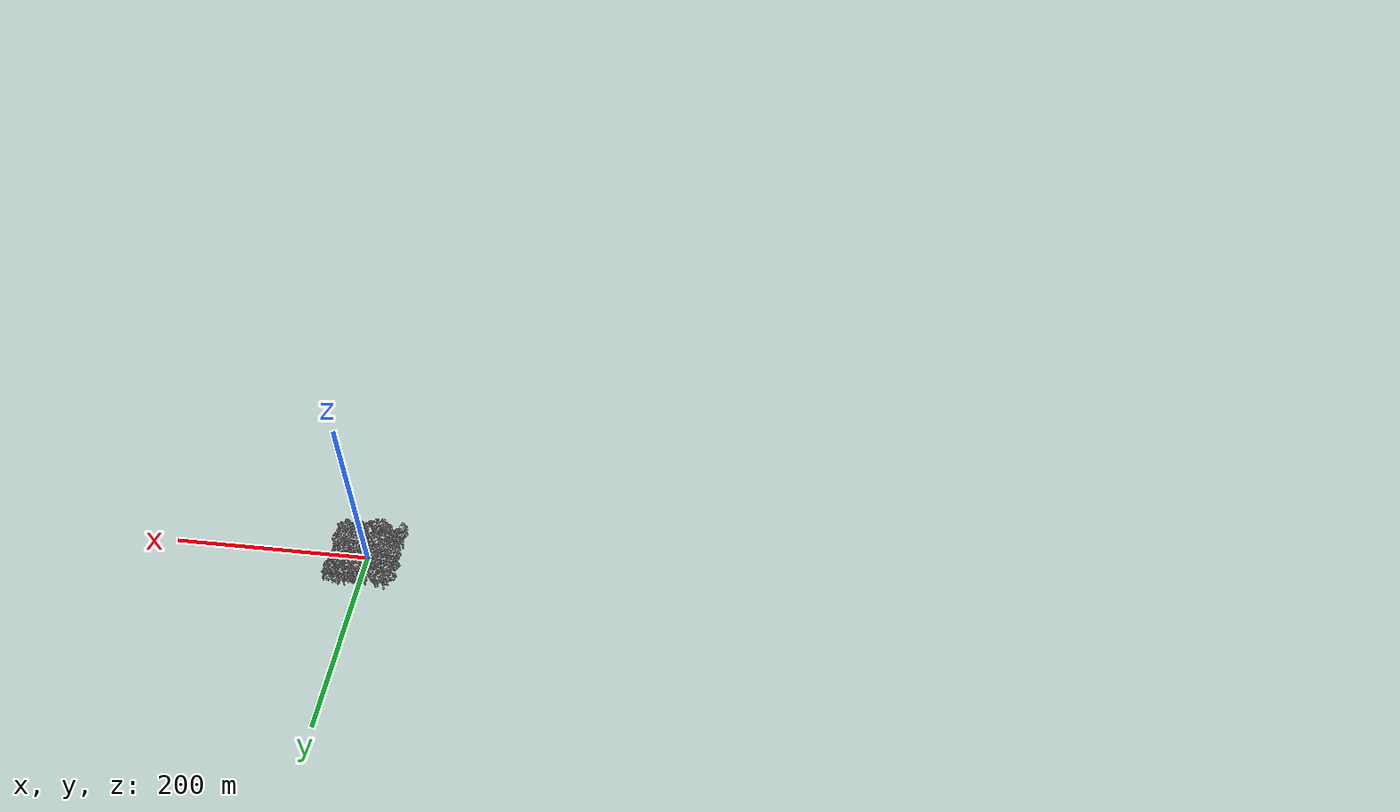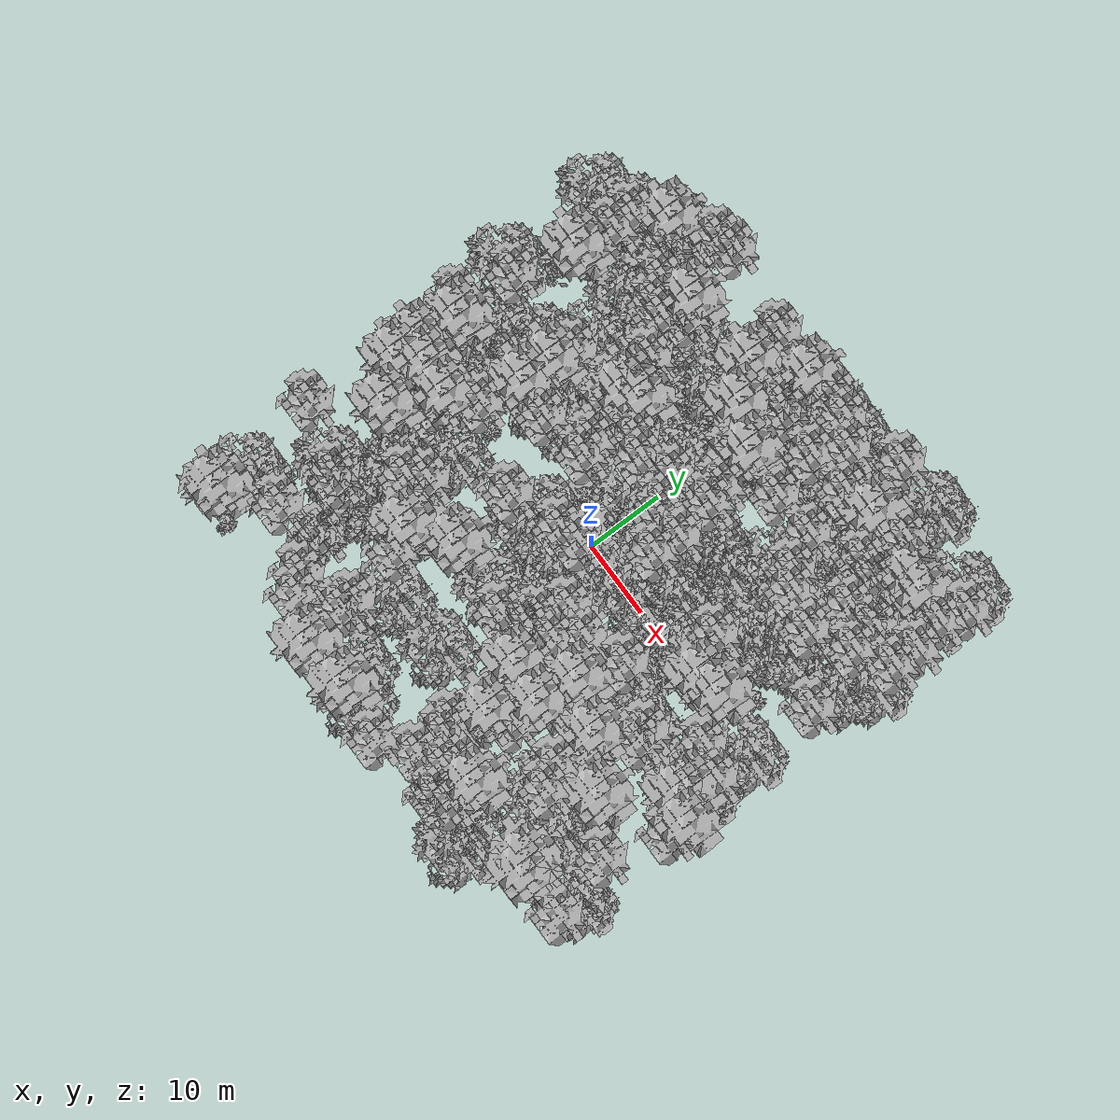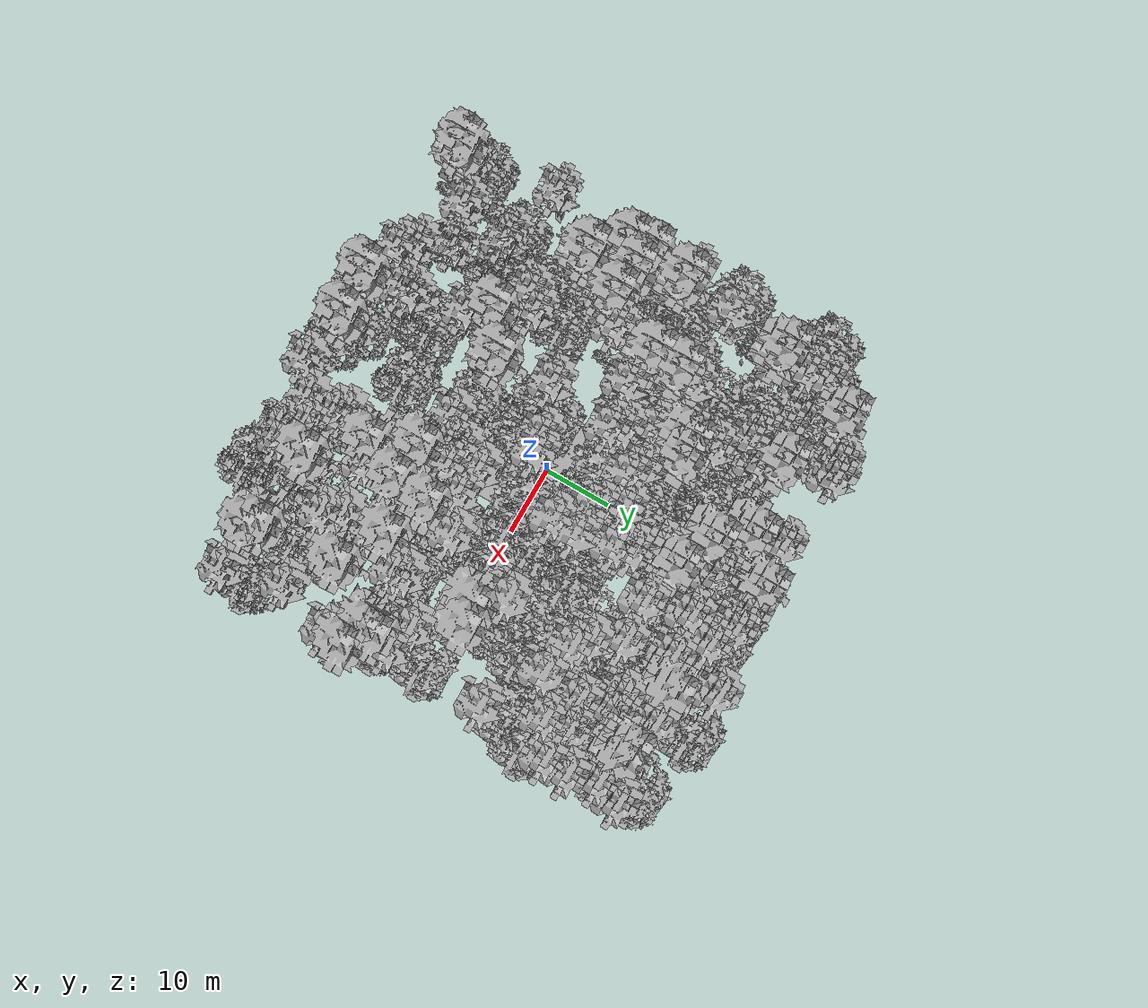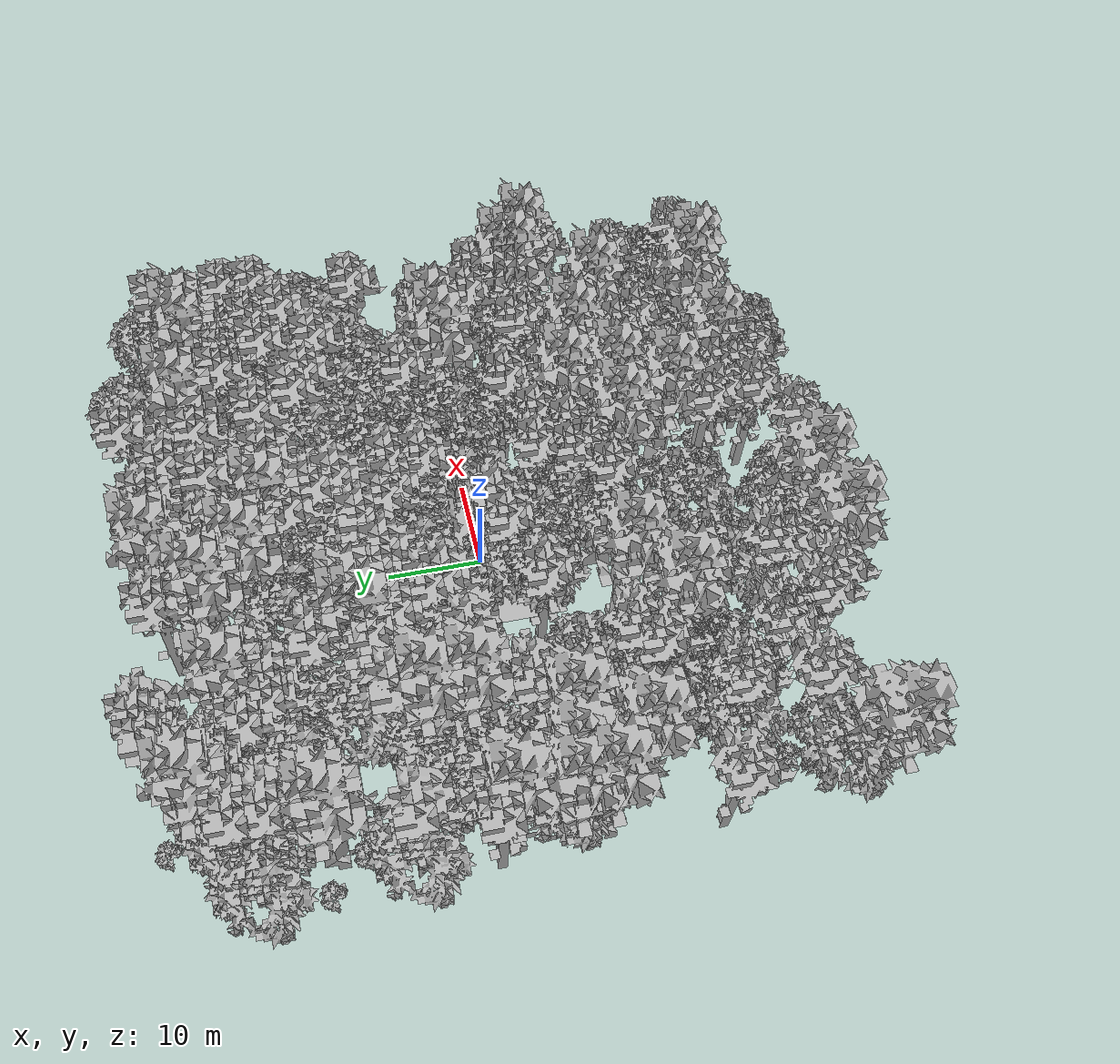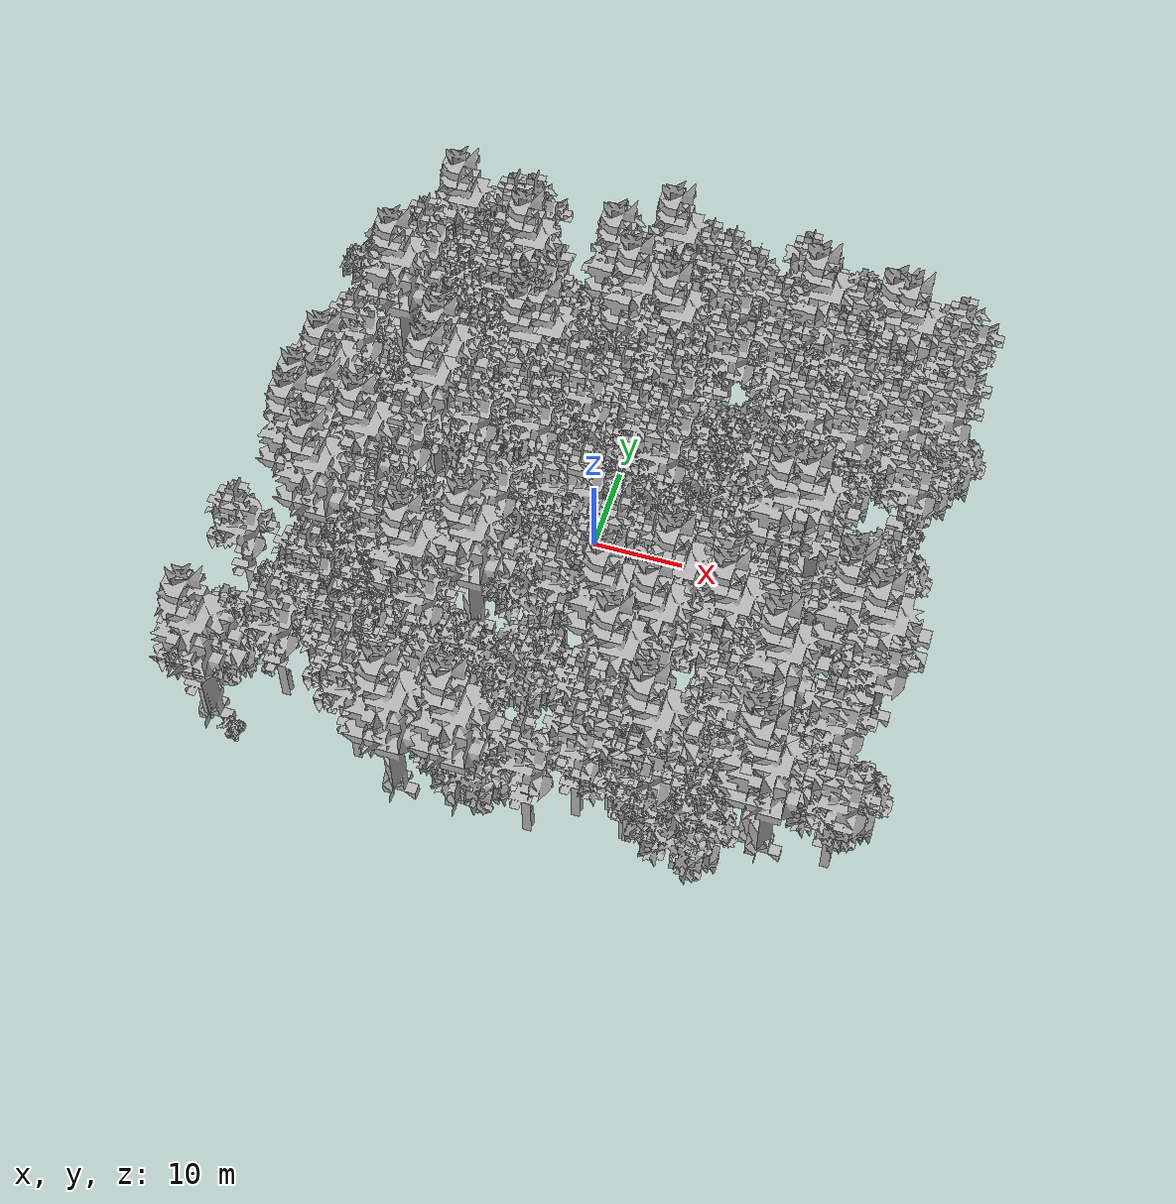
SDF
<sdf version="1.7">
    <world name="default">
        <plugin name="mrs_gazebo_static_transform_republisher_plugin" filename="libMrsGazeboCommonResources_StaticTransformRepublisher.so"/>
        <spherical_coordinates>
            <surface_model>EARTH_WGS84</surface_model>
            <latitude_deg>47.3977</latitude_deg>
            <longitude_deg>8.54559</longitude_deg>
            <elevation>0</elevation>
            <heading_deg>0</heading_deg>
        </spherical_coordinates>
        <physics name="default_physics" default="0" type="ode">
            <ode>
                <solver>
                    <type>quick</type>
                    <iters>10</iters>
                    <sor>1.3</sor>
                    <use_dynamic_moi_rescaling>0</use_dynamic_moi_rescaling>
                </solver>
                <constraints>
                    <cfm>0</cfm>
                    <erp>0.2</erp>
                    <contact_max_correcting_vel>1000</contact_max_correcting_vel>
                    <contact_surface_layer>0.001</contact_surface_layer>
                </constraints>
            </ode>
            <max_step_size>0.004</max_step_size>
            <real_time_factor>1</real_time_factor>
            <real_time_update_rate>250</real_time_update_rate>
        </physics>
        <scene>
            <shadows>0</shadows>
            <ambient>0.4 0.4 0.4 1</ambient>
            <background>0.7 0.7 0.7 1</background>
        </scene>
        <light name="sun" type="directional">
            <pose>0 0 1000 0.4 0.2 0</pose>
            <diffuse>1 1 1 1</diffuse>
            <specular>0.6 0.6 0.6 1</specular>
            <direction>0.1 0.1 -0.9</direction>
            <attenuation>
                <range>20</range>
                <constant>0.5</constant>
                <linear>0.01</linear>
                <quadratic>0.001</quadratic>
            </attenuation>
            <cast_shadows>1</cast_shadows>
            <spot>
                <inner_angle>0</inner_angle>
                <outer_angle>0</outer_angle>
                <falloff>0</falloff>
            </spot>
        </light>
        <model name="ground_plane">
            <static>1</static>
            <link name="link">
                <collision name="collision">
                    <pose>0 0 0 0 -0 0</pose>
                    <geometry>
                        <plane>
                            <normal>0 0 1</normal>
                            <size>70 70</size>
                        </plane>
                    </geometry>
                    <surface>
                        <contact>
                            <ode>
                                <min_depth>0.01</min_depth>
                                <max_vel>0</max_vel>
                            </ode>
                        </contact>
                        <friction>
                            <ode/>
                            <torsional>
                                <ode/>
                            </torsional>
                        </friction>
                        <bounce/>
                    </surface>
                    <max_contacts>10</max_contacts>
                </collision>
                <visual name="grass">
                    <pose>0 0 0 0 -0 0</pose>
                    <cast_shadows>0</cast_shadows>
                    <geometry>
                        <mesh>
                            <scale>0.29000000000000004 0.29000000000000004 0.1</scale>
                            <uri>file://grass_plane/meshes/grass_plane.dae</uri>
                        </mesh>
                    </geometry>
                </visual>
                <self_collide>0</self_collide>
                <enable_wind>0</enable_wind>
                <kinematic>0</kinematic>
            </link>
        </model>
        <model name="the_void">
            <static>1</static>
            <link name="link">
                <pose>0 0 0.1 0 -0 0</pose>
                <visual name="the_void">
                    <pose>0 0 2 0 -0 0</pose>
                    <geometry>
                        <sphere>
                            <radius>0.25</radius>
                        </sphere>
                    </geometry>
                    <material>
                        <script>
                            <uri>file://media/materials/scripts/Gazebo.material</uri>
                            <name>Gazebo/Black</name>
                        </script>
                    </material>
                </visual>
                <self_collide>0</self_collide>
                <enable_wind>0</enable_wind>
                <kinematic>0</kinematic>
            </link>
            <pose>-1000 -1000 0 0 -0 0</pose>
        </model>
        <gui fullscreen="0">
            <camera name="camera">
                <pose>35.1577 98.6044 40.0204 0 0.407996 -1.99761</pose>
                <view_controller>orbit</view_controller>
                <projection_type>perspective</projection_type>
            </camera>
        </gui>
        <plugin name="mrs_gazebo_rviz_cam_synchronizer" filename="libMrsGazeboCommonResources_RvizCameraSynchronizer.so">
            <target_frame_id>gazebo_user_camera</target_frame_id>
            <world_origin_frame_id>uav1/gps_origin</world_origin_frame_id>
            <frame_to_follow>uav1</frame_to_follow>
        </plugin>
        <gravity>0 0 -9.8066</gravity>
        <magnetic_field>6e-06 2.3e-05 -4.2e-05</magnetic_field>
        <atmosphere type="adiabatic"/>
        <wind/>
        <model name="Tree 0">
            <static>1</static>
            <pose>-20.72796595636353 -0.8571599605346449 0 1.57079 -0 0</pose>
            <link name="link">
                <pose>0 0 0 0 -0 0</pose>
                <collision name="collision">
                    <geometry>
                        <mesh>
                            <scale>5 5 5</scale>
                            <uri>model://tree_9/meshes/tree_9.obj</uri>
                        </mesh>
                    </geometry>
                    <max_contacts>10</max_contacts>
                    <surface>
                        <contact>
                            <ode/>
                        </contact>
                        <bounce/>
                        <friction>
                            <torsional>
                                <ode/>
                            </torsional>
                            <ode/>
                        </friction>
                    </surface>
                </collision>
                <visual name="visual">
                    <geometry>
                        <mesh>
                            <scale>5 5 5</scale>
                            <uri>model://tree_9/meshes/tree_9.obj</uri>
                        </mesh>
                    </geometry>
                </visual>
                <self_collide>0</self_collide>
                <enable_wind>0</enable_wind>
                <kinematic>0</kinematic>
            </link>
        </model>
        <model name="Tree 1">
            <static>1</static>
            <pose>20.451108163864845 -8.503648757612584 0 1.57079 -0 0</pose>
            <link name="link">
                <pose>0 0 0 0 -0 0</pose>
                <collision name="collision">
                    <geometry>
                        <mesh>
                            <scale>5 5 5</scale>
                            <uri>model://tree_2/meshes/tree_2.obj</uri>
                        </mesh>
                    </geometry>
                    <max_contacts>10</max_contacts>
                    <surface>
                        <contact>
                            <ode/>
                        </contact>
                        <bounce/>
                        <friction>
                            <torsional>
                                <ode/>
                            </torsional>
                            <ode/>
                        </friction>
                    </surface>
                </collision>
                <visual name="visual">
                    <geometry>
                        <mesh>
                            <scale>5 5 5</scale>
                            <uri>model://tree_2/meshes/tree_2.obj</uri>
                        </mesh>
                    </geometry>
                </visual>
                <self_collide>0</self_collide>
                <enable_wind>0</enable_wind>
                <kinematic>0</kinematic>
            </link>
        </model>
        <model name="Tree 2">
            <static>1</static>
            <pose>-17.93707764458719 22.777348619275365 0 1.57079 -0 0</pose>
            <link name="link">
                <pose>0 0 0 0 -0 0</pose>
                <collision name="collision">
                    <geometry>
                        <mesh>
                            <scale>5 5 5</scale>
                            <uri>model://tree_9/meshes/tree_9.obj</uri>
                        </mesh>
                    </geometry>
                    <max_contacts>10</max_contacts>
                    <surface>
                        <contact>
                            <ode/>
                        </contact>
                        <bounce/>
                        <friction>
                            <torsional>
                                <ode/>
                            </torsional>
                            <ode/>
                        </friction>
                    </surface>
                </collision>
                <visual name="visual">
                    <geometry>
                        <mesh>
                            <scale>5 5 5</scale>
                            <uri>model://tree_9/meshes/tree_9.obj</uri>
                        </mesh>
                    </geometry>
                </visual>
                <self_collide>0</self_collide>
                <enable_wind>0</enable_wind>
                <kinematic>0</kinematic>
            </link>
        </model>
        <model name="Tree 3">
            <static>1</static>
            <pose>21.22080247000826 11.679986534153123 0 1.57079 -0 0</pose>
            <link name="link">
                <pose>0 0 0 0 -0 0</pose>
                <collision name="collision">
                    <geometry>
                        <mesh>
                            <scale>5 5 5</scale>
                            <uri>model://tree_2/meshes/tree_2.obj</uri>
                        </mesh>
                    </geometry>
                    <max_contacts>10</max_contacts>
                    <surface>
                        <contact>
                            <ode/>
                        </contact>
                        <bounce/>
                        <friction>
                            <torsional>
                                <ode/>
                            </torsional>
                            <ode/>
                        </friction>
                    </surface>
                </collision>
                <visual name="visual">
                    <geometry>
                        <mesh>
                            <scale>5 5 5</scale>
                            <uri>model://tree_2/meshes/tree_2.obj</uri>
                        </mesh>
                    </geometry>
                </visual>
                <self_collide>0</self_collide>
                <enable_wind>0</enable_wind>
                <kinematic>0</kinematic>
            </link>
        </model>
        <model name="Tree 4">
            <static>1</static>
            <pose>-0.35684061162447733 -22.16048140596576 0 1.57079 -0 0</pose>
            <link name="link">
                <pose>0 0 0 0 -0 0</pose>
                <collision name="collision">
                    <geometry>
                        <mesh>
                            <scale>5 5 5</scale>
                            <uri>model://tree_2/meshes/tree_2.obj</uri>
                        </mesh>
                    </geometry>
                    <max_contacts>10</max_contacts>
                    <surface>
                        <contact>
                            <ode/>
                        </contact>
                        <bounce/>
                        <friction>
                            <torsional>
                                <ode/>
                            </torsional>
                            <ode/>
                        </friction>
                    </surface>
                </collision>
                <visual name="visual">
                    <geometry>
                        <mesh>
                            <scale>5 5 5</scale>
                            <uri>model://tree_2/meshes/tree_2.obj</uri>
                        </mesh>
                    </geometry>
                </visual>
                <self_collide>0</self_collide>
                <enable_wind>0</enable_wind>
                <kinematic>0</kinematic>
            </link>
        </model>
        <model name="Tree 5">
            <static>1</static>
            <pose>17.554701327103224 28.37882348100289 0 1.57079 -0 0</pose>
            <link name="link">
                <pose>0 0 0 0 -0 0</pose>
                <collision name="collision">
                    <geometry>
                        <mesh>
                            <scale>5 5 5</scale>
                            <uri>model://tree_4/meshes/tree_4.obj</uri>
                        </mesh>
                    </geometry>
                    <max_contacts>10</max_contacts>
                    <surface>
                        <contact>
                            <ode/>
                        </contact>
                        <bounce/>
                        <friction>
                            <torsional>
                                <ode/>
                            </torsional>
                            <ode/>
                        </friction>
                    </surface>
                </collision>
                <visual name="visual">
                    <geometry>
                        <mesh>
                            <scale>5 5 5</scale>
                            <uri>model://tree_4/meshes/tree_4.obj</uri>
                        </mesh>
                    </geometry>
                </visual>
                <self_collide>0</self_collide>
                <enable_wind>0</enable_wind>
                <kinematic>0</kinematic>
            </link>
        </model>
        <model name="Tree 6">
            <static>1</static>
            <pose>6.516080398578872 -15.849779528134338 0 1.57079 -0 0</pose>
            <link name="link">
                <pose>0 0 0 0 -0 0</pose>
                <collision name="collision">
                    <geometry>
                        <mesh>
                            <scale>5 5 5</scale>
                            <uri>model://tree_4/meshes/tree_4.obj</uri>
                        </mesh>
                    </geometry>
                    <max_contacts>10</max_contacts>
                    <surface>
                        <contact>
                            <ode/>
                        </contact>
                        <bounce/>
                        <friction>
                            <torsional>
                                <ode/>
                            </torsional>
                            <ode/>
                        </friction>
                    </surface>
                </collision>
                <visual name="visual">
                    <geometry>
                        <mesh>
                            <scale>5 5 5</scale>
                            <uri>model://tree_4/meshes/tree_4.obj</uri>
                        </mesh>
                    </geometry>
                </visual>
                <self_collide>0</self_collide>
                <enable_wind>0</enable_wind>
                <kinematic>0</kinematic>
            </link>
        </model>
        <model name="Tree 7">
            <static>1</static>
            <pose>-9.887393055710618 14.658670685171025 0 1.57079 -0 0</pose>
            <link name="link">
                <pose>0 0 0 0 -0 0</pose>
                <collision name="collision">
                    <geometry>
                        <mesh>
                            <scale>5 5 5</scale>
                            <uri>model://tree_4/meshes/tree_4.obj</uri>
                        </mesh>
                    </geometry>
                    <max_contacts>10</max_contacts>
                    <surface>
                        <contact>
                            <ode/>
                        </contact>
                        <bounce/>
                        <friction>
                            <torsional>
                                <ode/>
                            </torsional>
                            <ode/>
                        </friction>
                    </surface>
                </collision>
                <visual name="visual">
                    <geometry>
                        <mesh>
                            <scale>5 5 5</scale>
                            <uri>model://tree_4/meshes/tree_4.obj</uri>
                        </mesh>
                    </geometry>
                </visual>
                <self_collide>0</self_collide>
                <enable_wind>0</enable_wind>
                <kinematic>0</kinematic>
            </link>
        </model>
        <model name="Tree 8">
            <static>1</static>
            <pose>-1.5016746747762966 -33.702371741759194 0 1.57079 -0 0</pose>
            <link name="link">
                <pose>0 0 0 0 -0 0</pose>
                <collision name="collision">
                    <geometry>
                        <mesh>
                            <scale>5 5 5</scale>
                            <uri>model://tree_2/meshes/tree_2.obj</uri>
                        </mesh>
                    </geometry>
                    <max_contacts>10</max_contacts>
                    <surface>
                        <contact>
                            <ode/>
                        </contact>
                        <bounce/>
                        <friction>
                            <torsional>
                                <ode/>
                            </torsional>
                            <ode/>
                        </friction>
                    </surface>
                </collision>
                <visual name="visual">
                    <geometry>
                        <mesh>
                            <scale>5 5 5</scale>
                            <uri>model://tree_2/meshes/tree_2.obj</uri>
                        </mesh>
                    </geometry>
                </visual>
                <self_collide>0</self_collide>
                <enable_wind>0</enable_wind>
                <kinematic>0</kinematic>
            </link>
        </model>
        <model name="Tree 9">
            <static>1</static>
            <pose>13.415027923321624 27.199101276383594 0 1.57079 -0 0</pose>
            <link name="link">
                <pose>0 0 0 0 -0 0</pose>
                <collision name="collision">
                    <geometry>
                        <mesh>
                            <scale>5 5 5</scale>
                            <uri>model://tree_9/meshes/tree_9.obj</uri>
                        </mesh>
                    </geometry>
                    <max_contacts>10</max_contacts>
                    <surface>
                        <contact>
                            <ode/>
                        </contact>
                        <bounce/>
                        <friction>
                            <torsional>
                                <ode/>
                            </torsional>
                            <ode/>
                        </friction>
                    </surface>
                </collision>
                <visual name="visual">
                    <geometry>
                        <mesh>
                            <scale>5 5 5</scale>
                            <uri>model://tree_9/meshes/tree_9.obj</uri>
                        </mesh>
                    </geometry>
                </visual>
                <self_collide>0</self_collide>
                <enable_wind>0</enable_wind>
                <kinematic>0</kinematic>
            </link>
        </model>
        <model name="Tree 10">
            <static>1</static>
            <pose>-22.98953939201972 28.32693373725268 0 1.57079 -0 0</pose>
            <link name="link">
                <pose>0 0 0 0 -0 0</pose>
                <collision name="collision">
                    <geometry>
                        <mesh>
                            <scale>5 5 5</scale>
                            <uri>model://tree_9/meshes/tree_9.obj</uri>
                        </mesh>
                    </geometry>
                    <max_contacts>10</max_contacts>
                    <surface>
                        <contact>
                            <ode/>
                        </contact>
                        <bounce/>
                        <friction>
                            <torsional>
                                <ode/>
                            </torsional>
                            <ode/>
                        </friction>
                    </surface>
                </collision>
                <visual name="visual">
                    <geometry>
                        <mesh>
                            <scale>5 5 5</scale>
                            <uri>model://tree_9/meshes/tree_9.obj</uri>
                        </mesh>
                    </geometry>
                </visual>
                <self_collide>0</self_collide>
                <enable_wind>0</enable_wind>
                <kinematic>0</kinematic>
            </link>
        </model>
        <model name="Tree 11">
            <static>1</static>
            <pose>5.500935025787392 25.253025258825176 0 1.57079 -0 0</pose>
            <link name="link">
                <pose>0 0 0 0 -0 0</pose>
                <collision name="collision">
                    <geometry>
                        <mesh>
                            <scale>5 5 5</scale>
                            <uri>model://tree_2/meshes/tree_2.obj</uri>
                        </mesh>
                    </geometry>
                    <max_contacts>10</max_contacts>
                    <surface>
                        <contact>
                            <ode/>
                        </contact>
                        <bounce/>
                        <friction>
                            <torsional>
                                <ode/>
                            </torsional>
                            <ode/>
                        </friction>
                    </surface>
                </collision>
                <visual name="visual">
                    <geometry>
                        <mesh>
                            <scale>5 5 5</scale>
                            <uri>model://tree_2/meshes/tree_2.obj</uri>
                        </mesh>
                    </geometry>
                </visual>
                <self_collide>0</self_collide>
                <enable_wind>0</enable_wind>
                <kinematic>0</kinematic>
            </link>
        </model>
        <model name="Tree 12">
            <static>1</static>
            <pose>33.2929674667695 -29.78137408917678 0 1.57079 -0 0</pose>
            <link name="link">
                <pose>0 0 0 0 -0 0</pose>
                <collision name="collision">
                    <geometry>
                        <mesh>
                            <scale>5 5 5</scale>
                            <uri>model://tree_9/meshes/tree_9.obj</uri>
                        </mesh>
                    </geometry>
                    <max_contacts>10</max_contacts>
                    <surface>
                        <contact>
                            <ode/>
                        </contact>
                        <bounce/>
                        <friction>
                            <torsional>
                                <ode/>
                            </torsional>
                            <ode/>
                        </friction>
                    </surface>
                </collision>
                <visual name="visual">
                    <geometry>
                        <mesh>
                            <scale>5 5 5</scale>
                            <uri>model://tree_9/meshes/tree_9.obj</uri>
                        </mesh>
                    </geometry>
                </visual>
                <self_collide>0</self_collide>
                <enable_wind>0</enable_wind>
                <kinematic>0</kinematic>
            </link>
        </model>
        <model name="Tree 13">
            <static>1</static>
            <pose>18.613345052840224 -13.734592819964092 0 1.57079 -0 0</pose>
            <link name="link">
                <pose>0 0 0 0 -0 0</pose>
                <collision name="collision">
                    <geometry>
                        <mesh>
                            <scale>5 5 5</scale>
                            <uri>model://tree_4/meshes/tree_4.obj</uri>
                        </mesh>
                    </geometry>
                    <max_contacts>10</max_contacts>
                    <surface>
                        <contact>
                            <ode/>
                        </contact>
                        <bounce/>
                        <friction>
                            <torsional>
                                <ode/>
                            </torsional>
                            <ode/>
                        </friction>
                    </surface>
                </collision>
                <visual name="visual">
                    <geometry>
                        <mesh>
                            <scale>5 5 5</scale>
                            <uri>model://tree_4/meshes/tree_4.obj</uri>
                        </mesh>
                    </geometry>
                </visual>
                <self_collide>0</self_collide>
                <enable_wind>0</enable_wind>
                <kinematic>0</kinematic>
            </link>
        </model>
        <model name="Tree 14">
            <static>1</static>
            <pose>-13.155826143513934 24.653852895223466 0 1.57079 -0 0</pose>
            <link name="link">
                <pose>0 0 0 0 -0 0</pose>
                <collision name="collision">
                    <geometry>
                        <mesh>
                            <scale>5 5 5</scale>
                            <uri>model://tree_2/meshes/tree_2.obj</uri>
                        </mesh>
                    </geometry>
                    <max_contacts>10</max_contacts>
                    <surface>
                        <contact>
                            <ode/>
                        </contact>
                        <bounce/>
                        <friction>
                            <torsional>
                                <ode/>
                            </torsional>
                            <ode/>
                        </friction>
                    </surface>
                </collision>
                <visual name="visual">
                    <geometry>
                        <mesh>
                            <scale>5 5 5</scale>
                            <uri>model://tree_2/meshes/tree_2.obj</uri>
                        </mesh>
                    </geometry>
                </visual>
                <self_collide>0</self_collide>
                <enable_wind>0</enable_wind>
                <kinematic>0</kinematic>
            </link>
        </model>
        <model name="Tree 15">
            <static>1</static>
            <pose>0.6577428110080774 -13.890793284871908 0 1.57079 -0 0</pose>
            <link name="link">
                <pose>0 0 0 0 -0 0</pose>
                <collision name="collision">
                    <geometry>
                        <mesh>
                            <scale>5 5 5</scale>
                            <uri>model://tree_9/meshes/tree_9.obj</uri>
                        </mesh>
                    </geometry>
                    <max_contacts>10</max_contacts>
                    <surface>
                        <contact>
                            <ode/>
                        </contact>
                        <bounce/>
                        <friction>
                            <torsional>
                                <ode/>
                            </torsional>
                            <ode/>
                        </friction>
                    </surface>
                </collision>
                <visual name="visual">
                    <geometry>
                        <mesh>
                            <scale>5 5 5</scale>
                            <uri>model://tree_9/meshes/tree_9.obj</uri>
                        </mesh>
                    </geometry>
                </visual>
                <self_collide>0</self_collide>
                <enable_wind>0</enable_wind>
                <kinematic>0</kinematic>
            </link>
        </model>
        <model name="Tree 16">
            <static>1</static>
            <pose>23.783157276569398 23.85742574105118 0 1.57079 -0 0</pose>
            <link name="link">
                <pose>0 0 0 0 -0 0</pose>
                <collision name="collision">
                    <geometry>
                        <mesh>
                            <scale>5 5 5</scale>
                            <uri>model://tree_9/meshes/tree_9.obj</uri>
                        </mesh>
                    </geometry>
                    <max_contacts>10</max_contacts>
                    <surface>
                        <contact>
                            <ode/>
                        </contact>
                        <bounce/>
                        <friction>
                            <torsional>
                                <ode/>
                            </torsional>
                            <ode/>
                        </friction>
                    </surface>
                </collision>
                <visual name="visual">
                    <geometry>
                        <mesh>
                            <scale>5 5 5</scale>
                            <uri>model://tree_9/meshes/tree_9.obj</uri>
                        </mesh>
                    </geometry>
                </visual>
                <self_collide>0</self_collide>
                <enable_wind>0</enable_wind>
                <kinematic>0</kinematic>
            </link>
        </model>
        <model name="Tree 17">
            <static>1</static>
            <pose>-25.982245853864192 2.8366336242417916 0 1.57079 -0 0</pose>
            <link name="link">
                <pose>0 0 0 0 -0 0</pose>
                <collision name="collision">
                    <geometry>
                        <mesh>
                            <scale>5 5 5</scale>
                            <uri>model://tree_2/meshes/tree_2.obj</uri>
                        </mesh>
                    </geometry>
                    <max_contacts>10</max_contacts>
                    <surface>
                        <contact>
                            <ode/>
                        </contact>
                        <bounce/>
                        <friction>
                            <torsional>
                                <ode/>
                            </torsional>
                            <ode/>
                        </friction>
                    </surface>
                </collision>
                <visual name="visual">
                    <geometry>
                        <mesh>
                            <scale>5 5 5</scale>
                            <uri>model://tree_2/meshes/tree_2.obj</uri>
                        </mesh>
                    </geometry>
                </visual>
                <self_collide>0</self_collide>
                <enable_wind>0</enable_wind>
                <kinematic>0</kinematic>
            </link>
        </model>
        <model name="Tree 18">
            <static>1</static>
            <pose>-30.53831253542078 3.12437608804931 0 1.57079 -0 0</pose>
            <link name="link">
                <pose>0 0 0 0 -0 0</pose>
                <collision name="collision">
                    <geometry>
                        <mesh>
                            <scale>5 5 5</scale>
                            <uri>model://tree_4/meshes/tree_4.obj</uri>
                        </mesh>
                    </geometry>
                    <max_contacts>10</max_contacts>
                    <surface>
                        <contact>
                            <ode/>
                        </contact>
                        <bounce/>
                        <friction>
                            <torsional>
                                <ode/>
                            </torsional>
                            <ode/>
                        </friction>
                    </surface>
                </collision>
                <visual name="visual">
                    <geometry>
                        <mesh>
                            <scale>5 5 5</scale>
                            <uri>model://tree_4/meshes/tree_4.obj</uri>
                        </mesh>
                    </geometry>
                </visual>
                <self_collide>0</self_collide>
                <enable_wind>0</enable_wind>
                <kinematic>0</kinematic>
            </link>
        </model>
        <model name="Tree 19">
            <static>1</static>
            <pose>-24.71759503659493 30.340612021145517 0 1.57079 -0 0</pose>
            <link name="link">
                <pose>0 0 0 0 -0 0</pose>
                <collision name="collision">
                    <geometry>
                        <mesh>
                            <scale>5 5 5</scale>
                            <uri>model://tree_4/meshes/tree_4.obj</uri>
                        </mesh>
                    </geometry>
                    <max_contacts>10</max_contacts>
                    <surface>
                        <contact>
                            <ode/>
                        </contact>
                        <bounce/>
                        <friction>
                            <torsional>
                                <ode/>
                            </torsional>
                            <ode/>
                        </friction>
                    </surface>
                </collision>
                <visual name="visual">
                    <geometry>
                        <mesh>
                            <scale>5 5 5</scale>
                            <uri>model://tree_4/meshes/tree_4.obj</uri>
                        </mesh>
                    </geometry>
                </visual>
                <self_collide>0</self_collide>
                <enable_wind>0</enable_wind>
                <kinematic>0</kinematic>
            </link>
        </model>
        <model name="Tree 20">
            <static>1</static>
            <pose>33.595851866270806 -11.56552290754654 0 1.57079 -0 0</pose>
            <link name="link">
                <pose>0 0 0 0 -0 0</pose>
                <collision name="collision">
                    <geometry>
                        <mesh>
                            <scale>5 5 5</scale>
                            <uri>model://tree_4/meshes/tree_4.obj</uri>
                        </mesh>
                    </geometry>
                    <max_contacts>10</max_contacts>
                    <surface>
                        <contact>
                            <ode/>
                        </contact>
                        <bounce/>
                        <friction>
                            <torsional>
                                <ode/>
                            </torsional>
                            <ode/>
                        </friction>
                    </surface>
                </collision>
                <visual name="visual">
                    <geometry>
                        <mesh>
                            <scale>5 5 5</scale>
                            <uri>model://tree_4/meshes/tree_4.obj</uri>
                        </mesh>
                    </geometry>
                </visual>
                <self_collide>0</self_collide>
                <enable_wind>0</enable_wind>
                <kinematic>0</kinematic>
            </link>
        </model>
        <model name="Tree 21">
            <static>1</static>
            <pose>11.75320115348866 -16.734784934001564 0 1.57079 -0 0</pose>
            <link name="link">
                <pose>0 0 0 0 -0 0</pose>
                <collision name="collision">
                    <geometry>
                        <mesh>
                            <scale>5 5 5</scale>
                            <uri>model://tree_4/meshes/tree_4.obj</uri>
                        </mesh>
                    </geometry>
                    <max_contacts>10</max_contacts>
                    <surface>
                        <contact>
                            <ode/>
                        </contact>
                        <bounce/>
                        <friction>
                            <torsional>
                                <ode/>
                            </torsional>
                            <ode/>
                        </friction>
                    </surface>
                </collision>
                <visual name="visual">
                    <geometry>
                        <mesh>
                            <scale>5 5 5</scale>
                            <uri>model://tree_4/meshes/tree_4.obj</uri>
                        </mesh>
                    </geometry>
                </visual>
                <self_collide>0</self_collide>
                <enable_wind>0</enable_wind>
                <kinematic>0</kinematic>
            </link>
        </model>
        <model name="Tree 22">
            <static>1</static>
            <pose>-19.134725700995197 11.781303931295511 0 1.57079 -0 0</pose>
            <link name="link">
                <pose>0 0 0 0 -0 0</pose>
                <collision name="collision">
                    <geometry>
                        <mesh>
                            <scale>5 5 5</scale>
                            <uri>model://tree_9/meshes/tree_9.obj</uri>
                        </mesh>
                    </geometry>
                    <max_contacts>10</max_contacts>
                    <surface>
                        <contact>
                            <ode/>
                        </contact>
                        <bounce/>
                        <friction>
                            <torsional>
                                <ode/>
                            </torsional>
                            <ode/>
                        </friction>
                    </surface>
                </collision>
                <visual name="visual">
                    <geometry>
                        <mesh>
                            <scale>5 5 5</scale>
                            <uri>model://tree_9/meshes/tree_9.obj</uri>
                        </mesh>
                    </geometry>
                </visual>
                <self_collide>0</self_collide>
                <enable_wind>0</enable_wind>
                <kinematic>0</kinematic>
            </link>
        </model>
        <model name="Tree 23">
            <static>1</static>
            <pose>-10.006361388430044 -4.478906828208441 0 1.57079 -0 0</pose>
            <link name="link">
                <pose>0 0 0 0 -0 0</pose>
                <collision name="collision">
                    <geometry>
                        <mesh>
                            <scale>5 5 5</scale>
                            <uri>model://tree_9/meshes/tree_9.obj</uri>
                        </mesh>
                    </geometry>
                    <max_contacts>10</max_contacts>
                    <surface>
                        <contact>
                            <ode/>
                        </contact>
                        <bounce/>
                        <friction>
                            <torsional>
                                <ode/>
                            </torsional>
                            <ode/>
                        </friction>
                    </surface>
                </collision>
                <visual name="visual">
                    <geometry>
                        <mesh>
                            <scale>5 5 5</scale>
                            <uri>model://tree_9/meshes/tree_9.obj</uri>
                        </mesh>
                    </geometry>
                </visual>
                <self_collide>0</self_collide>
                <enable_wind>0</enable_wind>
                <kinematic>0</kinematic>
            </link>
        </model>
        <model name="Tree 24">
            <static>1</static>
            <pose>15.954363729011803 -6.459099030560662 0 1.57079 -0 0</pose>
            <link name="link">
                <pose>0 0 0 0 -0 0</pose>
                <collision name="collision">
                    <geometry>
                        <mesh>
                            <scale>5 5 5</scale>
                            <uri>model://tree_2/meshes/tree_2.obj</uri>
                        </mesh>
                    </geometry>
                    <max_contacts>10</max_contacts>
                    <surface>
                        <contact>
                            <ode/>
                        </contact>
                        <bounce/>
                        <friction>
                            <torsional>
                                <ode/>
                            </torsional>
                            <ode/>
                        </friction>
                    </surface>
                </collision>
                <visual name="visual">
                    <geometry>
                        <mesh>
                            <scale>5 5 5</scale>
                            <uri>model://tree_2/meshes/tree_2.obj</uri>
                        </mesh>
                    </geometry>
                </visual>
                <self_collide>0</self_collide>
                <enable_wind>0</enable_wind>
                <kinematic>0</kinematic>
            </link>
        </model>
        <model name="Tree 25">
            <static>1</static>
            <pose>-19.416172027799263 -25.19417690629236 0 1.57079 -0 0</pose>
            <link name="link">
                <pose>0 0 0 0 -0 0</pose>
                <collision name="collision">
                    <geometry>
                        <mesh>
                            <scale>5 5 5</scale>
                            <uri>model://tree_9/meshes/tree_9.obj</uri>
                        </mesh>
                    </geometry>
                    <max_contacts>10</max_contacts>
                    <surface>
                        <contact>
                            <ode/>
                        </contact>
                        <bounce/>
                        <friction>
                            <torsional>
                                <ode/>
                            </torsional>
                            <ode/>
                        </friction>
                    </surface>
                </collision>
                <visual name="visual">
                    <geometry>
                        <mesh>
                            <scale>5 5 5</scale>
                            <uri>model://tree_9/meshes/tree_9.obj</uri>
                        </mesh>
                    </geometry>
                </visual>
                <self_collide>0</self_collide>
                <enable_wind>0</enable_wind>
                <kinematic>0</kinematic>
            </link>
        </model>
        <model name="Tree 26">
            <static>1</static>
            <pose>15.58509580757115 0.22075298277160726 0 1.57079 -0 0</pose>
            <link name="link">
                <pose>0 0 0 0 -0 0</pose>
                <collision name="collision">
                    <geometry>
                        <mesh>
                            <scale>5 5 5</scale>
                            <uri>model://tree_2/meshes/tree_2.obj</uri>
                        </mesh>
                    </geometry>
                    <max_contacts>10</max_contacts>
                    <surface>
                        <contact>
                            <ode/>
                        </contact>
                        <bounce/>
                        <friction>
                            <torsional>
                                <ode/>
                            </torsional>
                            <ode/>
                        </friction>
                    </surface>
                </collision>
                <visual name="visual">
                    <geometry>
                        <mesh>
                            <scale>5 5 5</scale>
                            <uri>model://tree_2/meshes/tree_2.obj</uri>
                        </mesh>
                    </geometry>
                </visual>
                <self_collide>0</self_collide>
                <enable_wind>0</enable_wind>
                <kinematic>0</kinematic>
            </link>
        </model>
        <model name="Tree 27">
            <static>1</static>
            <pose>10.238390388947401 10.880425491174996 0 1.57079 -0 0</pose>
            <link name="link">
                <pose>0 0 0 0 -0 0</pose>
                <collision name="collision">
                    <geometry>
                        <mesh>
                            <scale>5 5 5</scale>
                            <uri>model://tree_2/meshes/tree_2.obj</uri>
                        </mesh>
                    </geometry>
                    <max_contacts>10</max_contacts>
                    <surface>
                        <contact>
                            <ode/>
                        </contact>
                        <bounce/>
                        <friction>
                            <torsional>
                                <ode/>
                            </torsional>
                            <ode/>
                        </friction>
                    </surface>
                </collision>
                <visual name="visual">
                    <geometry>
                        <mesh>
                            <scale>5 5 5</scale>
                            <uri>model://tree_2/meshes/tree_2.obj</uri>
                        </mesh>
                    </geometry>
                </visual>
                <self_collide>0</self_collide>
                <enable_wind>0</enable_wind>
                <kinematic>0</kinematic>
            </link>
        </model>
        <model name="Tree 28">
            <static>1</static>
            <pose>20.343108176317564 23.280481204357656 0 1.57079 -0 0</pose>
            <link name="link">
                <pose>0 0 0 0 -0 0</pose>
                <collision name="collision">
                    <geometry>
                        <mesh>
                            <scale>5 5 5</scale>
                            <uri>model://tree_2/meshes/tree_2.obj</uri>
                        </mesh>
                    </geometry>
                    <max_contacts>10</max_contacts>
                    <surface>
                        <contact>
                            <ode/>
                        </contact>
                        <bounce/>
                        <friction>
                            <torsional>
                                <ode/>
                            </torsional>
                            <ode/>
                        </friction>
                    </surface>
                </collision>
                <visual name="visual">
                    <geometry>
                        <mesh>
                            <scale>5 5 5</scale>
                            <uri>model://tree_2/meshes/tree_2.obj</uri>
                        </mesh>
                    </geometry>
                </visual>
                <self_collide>0</self_collide>
                <enable_wind>0</enable_wind>
                <kinematic>0</kinematic>
            </link>
        </model>
        <model name="Tree 29">
            <static>1</static>
            <pose>28.459324800288883 20.311680133557118 0 1.57079 -0 0</pose>
            <link name="link">
                <pose>0 0 0 0 -0 0</pose>
                <collision name="collision">
                    <geometry>
                        <mesh>
                            <scale>5 5 5</scale>
                            <uri>model://tree_9/meshes/tree_9.obj</uri>
                        </mesh>
                    </geometry>
                    <max_contacts>10</max_contacts>
                    <surface>
                        <contact>
                            <ode/>
                        </contact>
                        <bounce/>
                        <friction>
                            <torsional>
                                <ode/>
                            </torsional>
                            <ode/>
                        </friction>
                    </surface>
                </collision>
                <visual name="visual">
                    <geometry>
                        <mesh>
                            <scale>5 5 5</scale>
                            <uri>model://tree_9/meshes/tree_9.obj</uri>
                        </mesh>
                    </geometry>
                </visual>
                <self_collide>0</self_collide>
                <enable_wind>0</enable_wind>
                <kinematic>0</kinematic>
            </link>
        </model>
        <model name="Tree 30">
            <static>1</static>
            <pose>-8.545860499565524 -22.826163726782575 0 1.57079 -0 0</pose>
            <link name="link">
                <pose>0 0 0 0 -0 0</pose>
                <collision name="collision">
                    <geometry>
                        <mesh>
                            <scale>5 5 5</scale>
                            <uri>model://tree_2/meshes/tree_2.obj</uri>
                        </mesh>
                    </geometry>
                    <max_contacts>10</max_contacts>
                    <surface>
                        <contact>
                            <ode/>
                        </contact>
                        <bounce/>
                        <friction>
                            <torsional>
                                <ode/>
                            </torsional>
                            <ode/>
                        </friction>
                    </surface>
                </collision>
                <visual name="visual">
                    <geometry>
                        <mesh>
                            <scale>5 5 5</scale>
                            <uri>model://tree_2/meshes/tree_2.obj</uri>
                        </mesh>
                    </geometry>
                </visual>
                <self_collide>0</self_collide>
                <enable_wind>0</enable_wind>
                <kinematic>0</kinematic>
            </link>
        </model>
        <model name="Tree 31">
            <static>1</static>
            <pose>-14.174709668413985 -16.681003873834264 0 1.57079 -0 0</pose>
            <link name="link">
                <pose>0 0 0 0 -0 0</pose>
                <collision name="collision">
                    <geometry>
                        <mesh>
                            <scale>5 5 5</scale>
                            <uri>model://tree_4/meshes/tree_4.obj</uri>
                        </mesh>
                    </geometry>
                    <max_contacts>10</max_contacts>
                    <surface>
                        <contact>
                            <ode/>
                        </contact>
                        <bounce/>
                        <friction>
                            <torsional>
                                <ode/>
                            </torsional>
                            <ode/>
                        </friction>
                    </surface>
                </collision>
                <visual name="visual">
                    <geometry>
                        <mesh>
                            <scale>5 5 5</scale>
                            <uri>model://tree_4/meshes/tree_4.obj</uri>
                        </mesh>
                    </geometry>
                </visual>
                <self_collide>0</self_collide>
                <enable_wind>0</enable_wind>
                <kinematic>0</kinematic>
            </link>
        </model>
        <model name="Tree 32">
            <static>1</static>
            <pose>1.9568784747875654 20.675324576541847 0 1.57079 -0 0</pose>
            <link name="link">
                <pose>0 0 0 0 -0 0</pose>
                <collision name="collision">
                    <geometry>
                        <mesh>
                            <scale>5 5 5</scale>
                            <uri>model://tree_9/meshes/tree_9.obj</uri>
                        </mesh>
                    </geometry>
                    <max_contacts>10</max_contacts>
                    <surface>
                        <contact>
                            <ode/>
                        </contact>
                        <bounce/>
                        <friction>
                            <torsional>
                                <ode/>
                            </torsional>
                            <ode/>
                        </friction>
                    </surface>
                </collision>
                <visual name="visual">
                    <geometry>
                        <mesh>
                            <scale>5 5 5</scale>
                            <uri>model://tree_9/meshes/tree_9.obj</uri>
                        </mesh>
                    </geometry>
                </visual>
                <self_collide>0</self_collide>
                <enable_wind>0</enable_wind>
                <kinematic>0</kinematic>
            </link>
        </model>
        <model name="Tree 33">
            <static>1</static>
            <pose>19.23933608193468 -24.01174977535945 0 1.57079 -0 0</pose>
            <link name="link">
                <pose>0 0 0 0 -0 0</pose>
                <collision name="collision">
                    <geometry>
                        <mesh>
                            <scale>5 5 5</scale>
                            <uri>model://tree_2/meshes/tree_2.obj</uri>
                        </mesh>
                    </geometry>
                    <max_contacts>10</max_contacts>
                    <surface>
                        <contact>
                            <ode/>
                        </contact>
                        <bounce/>
                        <friction>
                            <torsional>
                                <ode/>
                            </torsional>
                            <ode/>
                        </friction>
                    </surface>
                </collision>
                <visual name="visual">
                    <geometry>
                        <mesh>
                            <scale>5 5 5</scale>
                            <uri>model://tree_2/meshes/tree_2.obj</uri>
                        </mesh>
                    </geometry>
                </visual>
                <self_collide>0</self_collide>
                <enable_wind>0</enable_wind>
                <kinematic>0</kinematic>
            </link>
        </model>
        <model name="Tree 34">
            <static>1</static>
            <pose>-4.290837231000886 28.81031693860856 0 1.57079 -0 0</pose>
            <link name="link">
                <pose>0 0 0 0 -0 0</pose>
                <collision name="collision">
                    <geometry>
                        <mesh>
                            <scale>5 5 5</scale>
                            <uri>model://tree_9/meshes/tree_9.obj</uri>
                        </mesh>
                    </geometry>
                    <max_contacts>10</max_contacts>
                    <surface>
                        <contact>
                            <ode/>
                        </contact>
                        <bounce/>
                        <friction>
                            <torsional>
                                <ode/>
                            </torsional>
                            <ode/>
                        </friction>
                    </surface>
                </collision>
                <visual name="visual">
                    <geometry>
                        <mesh>
                            <scale>5 5 5</scale>
                            <uri>model://tree_9/meshes/tree_9.obj</uri>
                        </mesh>
                    </geometry>
                </visual>
                <self_collide>0</self_collide>
                <enable_wind>0</enable_wind>
                <kinematic>0</kinematic>
            </link>
        </model>
        <model name="Tree 35">
            <static>1</static>
            <pose>11.281099403301724 4.115495006719684 0 1.57079 -0 0</pose>
            <link name="link">
                <pose>0 0 0 0 -0 0</pose>
                <collision name="collision">
                    <geometry>
                        <mesh>
                            <scale>5 5 5</scale>
                            <uri>model://tree_2/meshes/tree_2.obj</uri>
                        </mesh>
                    </geometry>
                    <max_contacts>10</max_contacts>
                    <surface>
                        <contact>
                            <ode/>
                        </contact>
                        <bounce/>
                        <friction>
                            <torsional>
                                <ode/>
                            </torsional>
                            <ode/>
                        </friction>
                    </surface>
                </collision>
                <visual name="visual">
                    <geometry>
                        <mesh>
                            <scale>5 5 5</scale>
                            <uri>model://tree_2/meshes/tree_2.obj</uri>
                        </mesh>
                    </geometry>
                </visual>
                <self_collide>0</self_collide>
                <enable_wind>0</enable_wind>
                <kinematic>0</kinematic>
            </link>
        </model>
        <model name="Tree 36">
            <static>1</static>
            <pose>-5.359628527210322 27.735196052209865 0 1.57079 -0 0</pose>
            <link name="link">
                <pose>0 0 0 0 -0 0</pose>
                <collision name="collision">
                    <geometry>
                        <mesh>
                            <scale>5 5 5</scale>
                            <uri>model://tree_4/meshes/tree_4.obj</uri>
                        </mesh>
                    </geometry>
                    <max_contacts>10</max_contacts>
                    <surface>
                        <contact>
                            <ode/>
                        </contact>
                        <bounce/>
                        <friction>
                            <torsional>
                                <ode/>
                            </torsional>
                            <ode/>
                        </friction>
                    </surface>
                </collision>
                <visual name="visual">
                    <geometry>
                        <mesh>
                            <scale>5 5 5</scale>
                            <uri>model://tree_4/meshes/tree_4.obj</uri>
                        </mesh>
                    </geometry>
                </visual>
                <self_collide>0</self_collide>
                <enable_wind>0</enable_wind>
                <kinematic>0</kinematic>
            </link>
        </model>
        <model name="Tree 37">
            <static>1</static>
            <pose>25.56122016573233 -23.800671391190313 0 1.57079 -0 0</pose>
            <link name="link">
                <pose>0 0 0 0 -0 0</pose>
                <collision name="collision">
                    <geometry>
                        <mesh>
                            <scale>5 5 5</scale>
                            <uri>model://tree_2/meshes/tree_2.obj</uri>
                        </mesh>
                    </geometry>
                    <max_contacts>10</max_contacts>
                    <surface>
                        <contact>
                            <ode/>
                        </contact>
                        <bounce/>
                        <friction>
                            <torsional>
                                <ode/>
                            </torsional>
                            <ode/>
                        </friction>
                    </surface>
                </collision>
                <visual name="visual">
                    <geometry>
                        <mesh>
                            <scale>5 5 5</scale>
                            <uri>model://tree_2/meshes/tree_2.obj</uri>
                        </mesh>
                    </geometry>
                </visual>
                <self_collide>0</self_collide>
                <enable_wind>0</enable_wind>
                <kinematic>0</kinematic>
            </link>
        </model>
        <model name="Tree 38">
            <static>1</static>
            <pose>13.919543447401544 -11.121491674539822 0 1.57079 -0 0</pose>
            <link name="link">
                <pose>0 0 0 0 -0 0</pose>
                <collision name="collision">
                    <geometry>
                        <mesh>
                            <scale>5 5 5</scale>
                            <uri>model://tree_2/meshes/tree_2.obj</uri>
                        </mesh>
                    </geometry>
                    <max_contacts>10</max_contacts>
                    <surface>
                        <contact>
                            <ode/>
                        </contact>
                        <bounce/>
                        <friction>
                            <torsional>
                                <ode/>
                            </torsional>
                            <ode/>
                        </friction>
                    </surface>
                </collision>
                <visual name="visual">
                    <geometry>
                        <mesh>
                            <scale>5 5 5</scale>
                            <uri>model://tree_2/meshes/tree_2.obj</uri>
                        </mesh>
                    </geometry>
                </visual>
                <self_collide>0</self_collide>
                <enable_wind>0</enable_wind>
                <kinematic>0</kinematic>
            </link>
        </model>
        <model name="Tree 39">
            <static>1</static>
            <pose>1.1424891446057899 30.519698558665752 0 1.57079 -0 0</pose>
            <link name="link">
                <pose>0 0 0 0 -0 0</pose>
                <collision name="collision">
                    <geometry>
                        <mesh>
                            <scale>5 5 5</scale>
                            <uri>model://tree_2/meshes/tree_2.obj</uri>
                        </mesh>
                    </geometry>
                    <max_contacts>10</max_contacts>
                    <surface>
                        <contact>
                            <ode/>
                        </contact>
                        <bounce/>
                        <friction>
                            <torsional>
                                <ode/>
                            </torsional>
                            <ode/>
                        </friction>
                    </surface>
                </collision>
                <visual name="visual">
                    <geometry>
                        <mesh>
                            <scale>5 5 5</scale>
                            <uri>model://tree_2/meshes/tree_2.obj</uri>
                        </mesh>
                    </geometry>
                </visual>
                <self_collide>0</self_collide>
                <enable_wind>0</enable_wind>
                <kinematic>0</kinematic>
            </link>
        </model>
        <model name="Tree 40">
            <static>1</static>
            <pose>33.71196952621489 16.018471205293842 0 1.57079 -0 0</pose>
            <link name="link">
                <pose>0 0 0 0 -0 0</pose>
                <collision name="collision">
                    <geometry>
                        <mesh>
                            <scale>5 5 5</scale>
                            <uri>model://tree_2/meshes/tree_2.obj</uri>
                        </mesh>
                    </geometry>
                    <max_contacts>10</max_contacts>
                    <surface>
                        <contact>
                            <ode/>
                        </contact>
                        <bounce/>
                        <friction>
                            <torsional>
                                <ode/>
                            </torsional>
                            <ode/>
                        </friction>
                    </surface>
                </collision>
                <visual name="visual">
                    <geometry>
                        <mesh>
                            <scale>5 5 5</scale>
                            <uri>model://tree_2/meshes/tree_2.obj</uri>
                        </mesh>
                    </geometry>
                </visual>
                <self_collide>0</self_collide>
                <enable_wind>0</enable_wind>
                <kinematic>0</kinematic>
            </link>
        </model>
        <model name="Tree 41">
            <static>1</static>
            <pose>14.884516651010287 20.762939898615905 0 1.57079 -0 0</pose>
            <link name="link">
                <pose>0 0 0 0 -0 0</pose>
                <collision name="collision">
                    <geometry>
                        <mesh>
                            <scale>5 5 5</scale>
                            <uri>model://tree_9/meshes/tree_9.obj</uri>
                        </mesh>
                    </geometry>
                    <max_contacts>10</max_contacts>
                    <surface>
                        <contact>
                            <ode/>
                        </contact>
                        <bounce/>
                        <friction>
                            <torsional>
                                <ode/>
                            </torsional>
                            <ode/>
                        </friction>
                    </surface>
                </collision>
                <visual name="visual">
                    <geometry>
                        <mesh>
                            <scale>5 5 5</scale>
                            <uri>model://tree_9/meshes/tree_9.obj</uri>
                        </mesh>
                    </geometry>
                </visual>
                <self_collide>0</self_collide>
                <enable_wind>0</enable_wind>
                <kinematic>0</kinematic>
            </link>
        </model>
        <model name="Tree 42">
            <static>1</static>
            <pose>-9.30767338521564 6.881466201906882 0 1.57079 -0 0</pose>
            <link name="link">
                <pose>0 0 0 0 -0 0</pose>
                <collision name="collision">
                    <geometry>
                        <mesh>
                            <scale>5 5 5</scale>
                            <uri>model://tree_9/meshes/tree_9.obj</uri>
                        </mesh>
                    </geometry>
                    <max_contacts>10</max_contacts>
                    <surface>
                        <contact>
                            <ode/>
                        </contact>
                        <bounce/>
                        <friction>
                            <torsional>
                                <ode/>
                            </torsional>
                            <ode/>
                        </friction>
                    </surface>
                </collision>
                <visual name="visual">
                    <geometry>
                        <mesh>
                            <scale>5 5 5</scale>
                            <uri>model://tree_9/meshes/tree_9.obj</uri>
                        </mesh>
                    </geometry>
                </visual>
                <self_collide>0</self_collide>
                <enable_wind>0</enable_wind>
                <kinematic>0</kinematic>
            </link>
        </model>
        <model name="Tree 43">
            <static>1</static>
            <pose>11.094405309211496 -30.09868720719511 0 1.57079 -0 0</pose>
            <link name="link">
                <pose>0 0 0 0 -0 0</pose>
                <collision name="collision">
                    <geometry>
                        <mesh>
                            <scale>5 5 5</scale>
                            <uri>model://tree_9/meshes/tree_9.obj</uri>
                        </mesh>
                    </geometry>
                    <max_contacts>10</max_contacts>
                    <surface>
                        <contact>
                            <ode/>
                        </contact>
                        <bounce/>
                        <friction>
                            <torsional>
                                <ode/>
                            </torsional>
                            <ode/>
                        </friction>
                    </surface>
                </collision>
                <visual name="visual">
                    <geometry>
                        <mesh>
                            <scale>5 5 5</scale>
                            <uri>model://tree_9/meshes/tree_9.obj</uri>
                        </mesh>
                    </geometry>
                </visual>
                <self_collide>0</self_collide>
                <enable_wind>0</enable_wind>
                <kinematic>0</kinematic>
            </link>
        </model>
        <model name="Tree 44">
            <static>1</static>
            <pose>14.504747621850548 26.423558030565488 0 1.57079 -0 0</pose>
            <link name="link">
                <pose>0 0 0 0 -0 0</pose>
                <collision name="collision">
                    <geometry>
                        <mesh>
                            <scale>5 5 5</scale>
                            <uri>model://tree_2/meshes/tree_2.obj</uri>
                        </mesh>
                    </geometry>
                    <max_contacts>10</max_contacts>
                    <surface>
                        <contact>
                            <ode/>
                        </contact>
                        <bounce/>
                        <friction>
                            <torsional>
                                <ode/>
                            </torsional>
                            <ode/>
                        </friction>
                    </surface>
                </collision>
                <visual name="visual">
                    <geometry>
                        <mesh>
                            <scale>5 5 5</scale>
                            <uri>model://tree_2/meshes/tree_2.obj</uri>
                        </mesh>
                    </geometry>
                </visual>
                <self_collide>0</self_collide>
                <enable_wind>0</enable_wind>
                <kinematic>0</kinematic>
            </link>
        </model>
        <model name="Tree 45">
            <static>1</static>
            <pose>-24.08423655181351 -5.035390617257924 0 1.57079 -0 0</pose>
            <link name="link">
                <pose>0 0 0 0 -0 0</pose>
                <collision name="collision">
                    <geometry>
                        <mesh>
                            <scale>5 5 5</scale>
                            <uri>model://tree_9/meshes/tree_9.obj</uri>
                        </mesh>
                    </geometry>
                    <max_contacts>10</max_contacts>
                    <surface>
                        <contact>
                            <ode/>
                        </contact>
                        <bounce/>
                        <friction>
                            <torsional>
                                <ode/>
                            </torsional>
                            <ode/>
                        </friction>
                    </surface>
                </collision>
                <visual name="visual">
                    <geometry>
                        <mesh>
                            <scale>5 5 5</scale>
                            <uri>model://tree_9/meshes/tree_9.obj</uri>
                        </mesh>
                    </geometry>
                </visual>
                <self_collide>0</self_collide>
                <enable_wind>0</enable_wind>
                <kinematic>0</kinematic>
            </link>
        </model>
        <model name="Tree 46">
            <static>1</static>
            <pose>14.748652098251696 -28.53026323483974 0 1.57079 -0 0</pose>
            <link name="link">
                <pose>0 0 0 0 -0 0</pose>
                <collision name="collision">
                    <geometry>
                        <mesh>
                            <scale>5 5 5</scale>
                            <uri>model://tree_4/meshes/tree_4.obj</uri>
                        </mesh>
                    </geometry>
                    <max_contacts>10</max_contacts>
                    <surface>
                        <contact>
                            <ode/>
                        </contact>
                        <bounce/>
                        <friction>
                            <torsional>
                                <ode/>
                            </torsional>
                            <ode/>
                        </friction>
                    </surface>
                </collision>
                <visual name="visual">
                    <geometry>
                        <mesh>
                            <scale>5 5 5</scale>
                            <uri>model://tree_4/meshes/tree_4.obj</uri>
                        </mesh>
                    </geometry>
                </visual>
                <self_collide>0</self_collide>
                <enable_wind>0</enable_wind>
                <kinematic>0</kinematic>
            </link>
        </model>
        <model name="Tree 47">
            <static>1</static>
            <pose>-21.384829965945492 28.53131384593688 0 1.57079 -0 0</pose>
            <link name="link">
                <pose>0 0 0 0 -0 0</pose>
                <collision name="collision">
                    <geometry>
                        <mesh>
                            <scale>5 5 5</scale>
                            <uri>model://tree_2/meshes/tree_2.obj</uri>
                        </mesh>
                    </geometry>
                    <max_contacts>10</max_contacts>
                    <surface>
                        <contact>
                            <ode/>
                        </contact>
                        <bounce/>
                        <friction>
                            <torsional>
                                <ode/>
                            </torsional>
                            <ode/>
                        </friction>
                    </surface>
                </collision>
                <visual name="visual">
                    <geometry>
                        <mesh>
                            <scale>5 5 5</scale>
                            <uri>model://tree_2/meshes/tree_2.obj</uri>
                        </mesh>
                    </geometry>
                </visual>
                <self_collide>0</self_collide>
                <enable_wind>0</enable_wind>
                <kinematic>0</kinematic>
            </link>
        </model>
        <model name="Tree 48">
            <static>1</static>
            <pose>22.867448975952293 11.61938349174897 0 1.57079 -0 0</pose>
            <link name="link">
                <pose>0 0 0 0 -0 0</pose>
                <collision name="collision">
                    <geometry>
                        <mesh>
                            <scale>5 5 5</scale>
                            <uri>model://tree_2/meshes/tree_2.obj</uri>
                        </mesh>
                    </geometry>
                    <max_contacts>10</max_contacts>
                    <surface>
                        <contact>
                            <ode/>
                        </contact>
                        <bounce/>
                        <friction>
                            <torsional>
                                <ode/>
                            </torsional>
                            <ode/>
                        </friction>
                    </surface>
                </collision>
                <visual name="visual">
                    <geometry>
                        <mesh>
                            <scale>5 5 5</scale>
                            <uri>model://tree_2/meshes/tree_2.obj</uri>
                        </mesh>
                    </geometry>
                </visual>
                <self_collide>0</self_collide>
                <enable_wind>0</enable_wind>
                <kinematic>0</kinematic>
            </link>
        </model>
        <model name="Tree 49">
            <static>1</static>
            <pose>23.402682131377226 0.9526612247854516 0 1.57079 -0 0</pose>
            <link name="link">
                <pose>0 0 0 0 -0 0</pose>
                <collision name="collision">
                    <geometry>
                        <mesh>
                            <scale>5 5 5</scale>
                            <uri>model://tree_4/meshes/tree_4.obj</uri>
                        </mesh>
                    </geometry>
                    <max_contacts>10</max_contacts>
                    <surface>
                        <contact>
                            <ode/>
                        </contact>
                        <bounce/>
                        <friction>
                            <torsional>
                                <ode/>
                            </torsional>
                            <ode/>
                        </friction>
                    </surface>
                </collision>
                <visual name="visual">
                    <geometry>
                        <mesh>
                            <scale>5 5 5</scale>
                            <uri>model://tree_4/meshes/tree_4.obj</uri>
                        </mesh>
                    </geometry>
                </visual>
                <self_collide>0</self_collide>
                <enable_wind>0</enable_wind>
                <kinematic>0</kinematic>
            </link>
        </model>
        <model name="Tree 50">
            <static>1</static>
            <pose>31.321863808368462 -5.433248681339759 0 1.57079 -0 0</pose>
            <link name="link">
                <pose>0 0 0 0 -0 0</pose>
                <collision name="collision">
                    <geometry>
                        <mesh>
                            <scale>5 5 5</scale>
                            <uri>model://tree_9/meshes/tree_9.obj</uri>
                        </mesh>
                    </geometry>
                    <max_contacts>10</max_contacts>
                    <surface>
                        <contact>
                            <ode/>
                        </contact>
                        <bounce/>
                        <friction>
                            <torsional>
                                <ode/>
                            </torsional>
                            <ode/>
                        </friction>
                    </surface>
                </collision>
                <visual name="visual">
                    <geometry>
                        <mesh>
                            <scale>5 5 5</scale>
                            <uri>model://tree_9/meshes/tree_9.obj</uri>
                        </mesh>
                    </geometry>
                </visual>
                <self_collide>0</self_collide>
                <enable_wind>0</enable_wind>
                <kinematic>0</kinematic>
            </link>
        </model>
        <model name="Tree 51">
            <static>1</static>
            <pose>22.218995254534526 29.427761245832983 0 1.57079 -0 0</pose>
            <link name="link">
                <pose>0 0 0 0 -0 0</pose>
                <collision name="collision">
                    <geometry>
                        <mesh>
                            <scale>5 5 5</scale>
                            <uri>model://tree_9/meshes/tree_9.obj</uri>
                        </mesh>
                    </geometry>
                    <max_contacts>10</max_contacts>
                    <surface>
                        <contact>
                            <ode/>
                        </contact>
                        <bounce/>
                        <friction>
                            <torsional>
                                <ode/>
                            </torsional>
                            <ode/>
                        </friction>
                    </surface>
                </collision>
                <visual name="visual">
                    <geometry>
                        <mesh>
                            <scale>5 5 5</scale>
                            <uri>model://tree_9/meshes/tree_9.obj</uri>
                        </mesh>
                    </geometry>
                </visual>
                <self_collide>0</self_collide>
                <enable_wind>0</enable_wind>
                <kinematic>0</kinematic>
            </link>
        </model>
        <model name="Tree 52">
            <static>1</static>
            <pose>1.5987458219797048 9.2771937078384 0 1.57079 -0 0</pose>
            <link name="link">
                <pose>0 0 0 0 -0 0</pose>
                <collision name="collision">
                    <geometry>
                        <mesh>
                            <scale>5 5 5</scale>
                            <uri>model://tree_9/meshes/tree_9.obj</uri>
                        </mesh>
                    </geometry>
                    <max_contacts>10</max_contacts>
                    <surface>
                        <contact>
                            <ode/>
                        </contact>
                        <bounce/>
                        <friction>
                            <torsional>
                                <ode/>
                            </torsional>
                            <ode/>
                        </friction>
                    </surface>
                </collision>
                <visual name="visual">
                    <geometry>
                        <mesh>
                            <scale>5 5 5</scale>
                            <uri>model://tree_9/meshes/tree_9.obj</uri>
                        </mesh>
                    </geometry>
                </visual>
                <self_collide>0</self_collide>
                <enable_wind>0</enable_wind>
                <kinematic>0</kinematic>
            </link>
        </model>
        <model name="Tree 53">
            <static>1</static>
            <pose>-2.1784099853083987 23.676326276139648 0 1.57079 -0 0</pose>
            <link name="link">
                <pose>0 0 0 0 -0 0</pose>
                <collision name="collision">
                    <geometry>
                        <mesh>
                            <scale>5 5 5</scale>
                            <uri>model://tree_4/meshes/tree_4.obj</uri>
                        </mesh>
                    </geometry>
                    <max_contacts>10</max_contacts>
                    <surface>
                        <contact>
                            <ode/>
                        </contact>
                        <bounce/>
                        <friction>
                            <torsional>
                                <ode/>
                            </torsional>
                            <ode/>
                        </friction>
                    </surface>
                </collision>
                <visual name="visual">
                    <geometry>
                        <mesh>
                            <scale>5 5 5</scale>
                            <uri>model://tree_4/meshes/tree_4.obj</uri>
                        </mesh>
                    </geometry>
                </visual>
                <self_collide>0</self_collide>
                <enable_wind>0</enable_wind>
                <kinematic>0</kinematic>
            </link>
        </model>
        <model name="Tree 54">
            <static>1</static>
            <pose>-10.092448693488798 -34.098062078575275 0 1.57079 -0 0</pose>
            <link name="link">
                <pose>0 0 0 0 -0 0</pose>
                <collision name="collision">
                    <geometry>
                        <mesh>
                            <scale>5 5 5</scale>
                            <uri>model://tree_4/meshes/tree_4.obj</uri>
                        </mesh>
                    </geometry>
                    <max_contacts>10</max_contacts>
                    <surface>
                        <contact>
                            <ode/>
                        </contact>
                        <bounce/>
                        <friction>
                            <torsional>
                                <ode/>
                            </torsional>
                            <ode/>
                        </friction>
                    </surface>
                </collision>
                <visual name="visual">
                    <geometry>
                        <mesh>
                            <scale>5 5 5</scale>
                            <uri>model://tree_4/meshes/tree_4.obj</uri>
                        </mesh>
                    </geometry>
                </visual>
                <self_collide>0</self_collide>
                <enable_wind>0</enable_wind>
                <kinematic>0</kinematic>
            </link>
        </model>
        <model name="Tree 55">
            <static>1</static>
            <pose>20.808689133314694 0.43514609856021025 0 1.57079 -0 0</pose>
            <link name="link">
                <pose>0 0 0 0 -0 0</pose>
                <collision name="collision">
                    <geometry>
                        <mesh>
                            <scale>5 5 5</scale>
                            <uri>model://tree_4/meshes/tree_4.obj</uri>
                        </mesh>
                    </geometry>
                    <max_contacts>10</max_contacts>
                    <surface>
                        <contact>
                            <ode/>
                        </contact>
                        <bounce/>
                        <friction>
                            <torsional>
                                <ode/>
                            </torsional>
                            <ode/>
                        </friction>
                    </surface>
                </collision>
                <visual name="visual">
                    <geometry>
                        <mesh>
                            <scale>5 5 5</scale>
                            <uri>model://tree_4/meshes/tree_4.obj</uri>
                        </mesh>
                    </geometry>
                </visual>
                <self_collide>0</self_collide>
                <enable_wind>0</enable_wind>
                <kinematic>0</kinematic>
            </link>
        </model>
        <model name="Tree 56">
            <static>1</static>
            <pose>-17.25235050121449 5.026775642384621 0 1.57079 -0 0</pose>
            <link name="link">
                <pose>0 0 0 0 -0 0</pose>
                <collision name="collision">
                    <geometry>
                        <mesh>
                            <scale>5 5 5</scale>
                            <uri>model://tree_2/meshes/tree_2.obj</uri>
                        </mesh>
                    </geometry>
                    <max_contacts>10</max_contacts>
                    <surface>
                        <contact>
                            <ode/>
                        </contact>
                        <bounce/>
                        <friction>
                            <torsional>
                                <ode/>
                            </torsional>
                            <ode/>
                        </friction>
                    </surface>
                </collision>
                <visual name="visual">
                    <geometry>
                        <mesh>
                            <scale>5 5 5</scale>
                            <uri>model://tree_2/meshes/tree_2.obj</uri>
                        </mesh>
                    </geometry>
                </visual>
                <self_collide>0</self_collide>
                <enable_wind>0</enable_wind>
                <kinematic>0</kinematic>
            </link>
        </model>
        <model name="Tree 57">
            <static>1</static>
            <pose>-5.625844707846962 -2.4422319020499117 0 1.57079 -0 0</pose>
            <link name="link">
                <pose>0 0 0 0 -0 0</pose>
                <collision name="collision">
                    <geometry>
                        <mesh>
                            <scale>5 5 5</scale>
                            <uri>model://tree_2/meshes/tree_2.obj</uri>
                        </mesh>
                    </geometry>
                    <max_contacts>10</max_contacts>
                    <surface>
                        <contact>
                            <ode/>
                        </contact>
                        <bounce/>
                        <friction>
                            <torsional>
                                <ode/>
                            </torsional>
                            <ode/>
                        </friction>
                    </surface>
                </collision>
                <visual name="visual">
                    <geometry>
                        <mesh>
                            <scale>5 5 5</scale>
                            <uri>model://tree_2/meshes/tree_2.obj</uri>
                        </mesh>
                    </geometry>
                </visual>
                <self_collide>0</self_collide>
                <enable_wind>0</enable_wind>
                <kinematic>0</kinematic>
            </link>
        </model>
        <model name="Tree 58">
            <static>1</static>
            <pose>-0.27144623589579453 10.844339724185978 0 1.57079 -0 0</pose>
            <link name="link">
                <pose>0 0 0 0 -0 0</pose>
                <collision name="collision">
                    <geometry>
                        <mesh>
                            <scale>5 5 5</scale>
                            <uri>model://tree_2/meshes/tree_2.obj</uri>
                        </mesh>
                    </geometry>
                    <max_contacts>10</max_contacts>
                    <surface>
                        <contact>
                            <ode/>
                        </contact>
                        <bounce/>
                        <friction>
                            <torsional>
                                <ode/>
                            </torsional>
                            <ode/>
                        </friction>
                    </surface>
                </collision>
                <visual name="visual">
                    <geometry>
                        <mesh>
                            <scale>5 5 5</scale>
                            <uri>model://tree_2/meshes/tree_2.obj</uri>
                        </mesh>
                    </geometry>
                </visual>
                <self_collide>0</self_collide>
                <enable_wind>0</enable_wind>
                <kinematic>0</kinematic>
            </link>
        </model>
        <model name="Tree 59">
            <static>1</static>
            <pose>25.662530111078652 -28.85383218650572 0 1.57079 -0 0</pose>
            <link name="link">
                <pose>0 0 0 0 -0 0</pose>
                <collision name="collision">
                    <geometry>
                        <mesh>
                            <scale>5 5 5</scale>
                            <uri>model://tree_4/meshes/tree_4.obj</uri>
                        </mesh>
                    </geometry>
                    <max_contacts>10</max_contacts>
                    <surface>
                        <contact>
                            <ode/>
                        </contact>
                        <bounce/>
                        <friction>
                            <torsional>
                                <ode/>
                            </torsional>
                            <ode/>
                        </friction>
                    </surface>
                </collision>
                <visual name="visual">
                    <geometry>
                        <mesh>
                            <scale>5 5 5</scale>
                            <uri>model://tree_4/meshes/tree_4.obj</uri>
                        </mesh>
                    </geometry>
                </visual>
                <self_collide>0</self_collide>
                <enable_wind>0</enable_wind>
                <kinematic>0</kinematic>
            </link>
        </model>
        <model name="Tree 60">
            <static>1</static>
            <pose>-16.322815380174813 22.375721664664916 0 1.57079 -0 0</pose>
            <link name="link">
                <pose>0 0 0 0 -0 0</pose>
                <collision name="collision">
                    <geometry>
                        <mesh>
                            <scale>5 5 5</scale>
                            <uri>model://tree_9/meshes/tree_9.obj</uri>
                        </mesh>
                    </geometry>
                    <max_contacts>10</max_contacts>
                    <surface>
                        <contact>
                            <ode/>
                        </contact>
                        <bounce/>
                        <friction>
                            <torsional>
                                <ode/>
                            </torsional>
                            <ode/>
                        </friction>
                    </surface>
                </collision>
                <visual name="visual">
                    <geometry>
                        <mesh>
                            <scale>5 5 5</scale>
                            <uri>model://tree_9/meshes/tree_9.obj</uri>
                        </mesh>
                    </geometry>
                </visual>
                <self_collide>0</self_collide>
                <enable_wind>0</enable_wind>
                <kinematic>0</kinematic>
            </link>
        </model>
        <model name="Tree 61">
            <static>1</static>
            <pose>4.095249499256525 6.536186322329648 0 1.57079 -0 0</pose>
            <link name="link">
                <pose>0 0 0 0 -0 0</pose>
                <collision name="collision">
                    <geometry>
                        <mesh>
                            <scale>5 5 5</scale>
                            <uri>model://tree_2/meshes/tree_2.obj</uri>
                        </mesh>
                    </geometry>
                    <max_contacts>10</max_contacts>
                    <surface>
                        <contact>
                            <ode/>
                        </contact>
                        <bounce/>
                        <friction>
                            <torsional>
                                <ode/>
                            </torsional>
                            <ode/>
                        </friction>
                    </surface>
                </collision>
                <visual name="visual">
                    <geometry>
                        <mesh>
                            <scale>5 5 5</scale>
                            <uri>model://tree_2/meshes/tree_2.obj</uri>
                        </mesh>
                    </geometry>
                </visual>
                <self_collide>0</self_collide>
                <enable_wind>0</enable_wind>
                <kinematic>0</kinematic>
            </link>
        </model>
        <model name="Tree 62">
            <static>1</static>
            <pose>-19.067529925008294 -13.201055790567242 0 1.57079 -0 0</pose>
            <link name="link">
                <pose>0 0 0 0 -0 0</pose>
                <collision name="collision">
                    <geometry>
                        <mesh>
                            <scale>5 5 5</scale>
                            <uri>model://tree_9/meshes/tree_9.obj</uri>
                        </mesh>
                    </geometry>
                    <max_contacts>10</max_contacts>
                    <surface>
                        <contact>
                            <ode/>
                        </contact>
                        <bounce/>
                        <friction>
                            <torsional>
                                <ode/>
                            </torsional>
                            <ode/>
                        </friction>
                    </surface>
                </collision>
                <visual name="visual">
                    <geometry>
                        <mesh>
                            <scale>5 5 5</scale>
                            <uri>model://tree_9/meshes/tree_9.obj</uri>
                        </mesh>
                    </geometry>
                </visual>
                <self_collide>0</self_collide>
                <enable_wind>0</enable_wind>
                <kinematic>0</kinematic>
            </link>
        </model>
        <model name="Tree 63">
            <static>1</static>
            <pose>26.51683350646848 -8.159967256172486 0 1.57079 -0 0</pose>
            <link name="link">
                <pose>0 0 0 0 -0 0</pose>
                <collision name="collision">
                    <geometry>
                        <mesh>
                            <scale>5 5 5</scale>
                            <uri>model://tree_2/meshes/tree_2.obj</uri>
                        </mesh>
                    </geometry>
                    <max_contacts>10</max_contacts>
                    <surface>
                        <contact>
                            <ode/>
                        </contact>
                        <bounce/>
                        <friction>
                            <torsional>
                                <ode/>
                            </torsional>
                            <ode/>
                        </friction>
                    </surface>
                </collision>
                <visual name="visual">
                    <geometry>
                        <mesh>
                            <scale>5 5 5</scale>
                            <uri>model://tree_2/meshes/tree_2.obj</uri>
                        </mesh>
                    </geometry>
                </visual>
                <self_collide>0</self_collide>
                <enable_wind>0</enable_wind>
                <kinematic>0</kinematic>
            </link>
        </model>
        <model name="Tree 64">
            <static>1</static>
            <pose>17.877005441744224 4.817520126394605 0 1.57079 -0 0</pose>
            <link name="link">
                <pose>0 0 0 0 -0 0</pose>
                <collision name="collision">
                    <geometry>
                        <mesh>
                            <scale>5 5 5</scale>
                            <uri>model://tree_9/meshes/tree_9.obj</uri>
                        </mesh>
                    </geometry>
                    <max_contacts>10</max_contacts>
                    <surface>
                        <contact>
                            <ode/>
                        </contact>
                        <bounce/>
                        <friction>
                            <torsional>
                                <ode/>
                            </torsional>
                            <ode/>
                        </friction>
                    </surface>
                </collision>
                <visual name="visual">
                    <geometry>
                        <mesh>
                            <scale>5 5 5</scale>
                            <uri>model://tree_9/meshes/tree_9.obj</uri>
                        </mesh>
                    </geometry>
                </visual>
                <self_collide>0</self_collide>
                <enable_wind>0</enable_wind>
                <kinematic>0</kinematic>
            </link>
        </model>
        <model name="Tree 65">
            <static>1</static>
            <pose>1.7243987079853653 -9.02996922799733 0 1.57079 -0 0</pose>
            <link name="link">
                <pose>0 0 0 0 -0 0</pose>
                <collision name="collision">
                    <geometry>
                        <mesh>
                            <scale>5 5 5</scale>
                            <uri>model://tree_2/meshes/tree_2.obj</uri>
                        </mesh>
                    </geometry>
                    <max_contacts>10</max_contacts>
                    <surface>
                        <contact>
                            <ode/>
                        </contact>
                        <bounce/>
                        <friction>
                            <torsional>
                                <ode/>
                            </torsional>
                            <ode/>
                        </friction>
                    </surface>
                </collision>
                <visual name="visual">
                    <geometry>
                        <mesh>
                            <scale>5 5 5</scale>
                            <uri>model://tree_2/meshes/tree_2.obj</uri>
                        </mesh>
                    </geometry>
                </visual>
                <self_collide>0</self_collide>
                <enable_wind>0</enable_wind>
                <kinematic>0</kinematic>
            </link>
        </model>
        <model name="Tree 66">
            <static>1</static>
            <pose>-31.369401541217222 -31.549917692152118 0 1.57079 -0 0</pose>
            <link name="link">
                <pose>0 0 0 0 -0 0</pose>
                <collision name="collision">
                    <geometry>
                        <mesh>
                            <scale>5 5 5</scale>
                            <uri>model://tree_4/meshes/tree_4.obj</uri>
                        </mesh>
                    </geometry>
                    <max_contacts>10</max_contacts>
                    <surface>
                        <contact>
                            <ode/>
                        </contact>
                        <bounce/>
                        <friction>
                            <torsional>
                                <ode/>
                            </torsional>
                            <ode/>
                        </friction>
                    </surface>
                </collision>
                <visual name="visual">
                    <geometry>
                        <mesh>
                            <scale>5 5 5</scale>
                            <uri>model://tree_4/meshes/tree_4.obj</uri>
                        </mesh>
                    </geometry>
                </visual>
                <self_collide>0</self_collide>
                <enable_wind>0</enable_wind>
                <kinematic>0</kinematic>
            </link>
        </model>
        <model name="Tree 67">
            <static>1</static>
            <pose>7.592017118218486 26.667175898543924 0 1.57079 -0 0</pose>
            <link name="link">
                <pose>0 0 0 0 -0 0</pose>
                <collision name="collision">
                    <geometry>
                        <mesh>
                            <scale>5 5 5</scale>
                            <uri>model://tree_9/meshes/tree_9.obj</uri>
                        </mesh>
                    </geometry>
                    <max_contacts>10</max_contacts>
                    <surface>
                        <contact>
                            <ode/>
                        </contact>
                        <bounce/>
                        <friction>
                            <torsional>
                                <ode/>
                            </torsional>
                            <ode/>
                        </friction>
                    </surface>
                </collision>
                <visual name="visual">
                    <geometry>
                        <mesh>
                            <scale>5 5 5</scale>
                            <uri>model://tree_9/meshes/tree_9.obj</uri>
                        </mesh>
                    </geometry>
                </visual>
                <self_collide>0</self_collide>
                <enable_wind>0</enable_wind>
                <kinematic>0</kinematic>
            </link>
        </model>
        <model name="Tree 68">
            <static>1</static>
            <pose>24.448112132366667 -19.581654711419773 0 1.57079 -0 0</pose>
            <link name="link">
                <pose>0 0 0 0 -0 0</pose>
                <collision name="collision">
                    <geometry>
                        <mesh>
                            <scale>5 5 5</scale>
                            <uri>model://tree_2/meshes/tree_2.obj</uri>
                        </mesh>
                    </geometry>
                    <max_contacts>10</max_contacts>
                    <surface>
                        <contact>
                            <ode/>
                        </contact>
                        <bounce/>
                        <friction>
                            <torsional>
                                <ode/>
                            </torsional>
                            <ode/>
                        </friction>
                    </surface>
                </collision>
                <visual name="visual">
                    <geometry>
                        <mesh>
                            <scale>5 5 5</scale>
                            <uri>model://tree_2/meshes/tree_2.obj</uri>
                        </mesh>
                    </geometry>
                </visual>
                <self_collide>0</self_collide>
                <enable_wind>0</enable_wind>
                <kinematic>0</kinematic>
            </link>
        </model>
        <model name="Tree 69">
            <static>1</static>
            <pose>6.011724966954532 8.18515269213453 0 1.57079 -0 0</pose>
            <link name="link">
                <pose>0 0 0 0 -0 0</pose>
                <collision name="collision">
                    <geometry>
                        <mesh>
                            <scale>5 5 5</scale>
                            <uri>model://tree_9/meshes/tree_9.obj</uri>
                        </mesh>
                    </geometry>
                    <max_contacts>10</max_contacts>
                    <surface>
                        <contact>
                            <ode/>
                        </contact>
                        <bounce/>
                        <friction>
                            <torsional>
                                <ode/>
                            </torsional>
                            <ode/>
                        </friction>
                    </surface>
                </collision>
                <visual name="visual">
                    <geometry>
                        <mesh>
                            <scale>5 5 5</scale>
                            <uri>model://tree_9/meshes/tree_9.obj</uri>
                        </mesh>
                    </geometry>
                </visual>
                <self_collide>0</self_collide>
                <enable_wind>0</enable_wind>
                <kinematic>0</kinematic>
            </link>
        </model>
        <model name="Tree 70">
            <static>1</static>
            <pose>14.854279379803934 34.698907219520294 0 1.57079 -0 0</pose>
            <link name="link">
                <pose>0 0 0 0 -0 0</pose>
                <collision name="collision">
                    <geometry>
                        <mesh>
                            <scale>5 5 5</scale>
                            <uri>model://tree_9/meshes/tree_9.obj</uri>
                        </mesh>
                    </geometry>
                    <max_contacts>10</max_contacts>
                    <surface>
                        <contact>
                            <ode/>
                        </contact>
                        <bounce/>
                        <friction>
                            <torsional>
                                <ode/>
                            </torsional>
                            <ode/>
                        </friction>
                    </surface>
                </collision>
                <visual name="visual">
                    <geometry>
                        <mesh>
                            <scale>5 5 5</scale>
                            <uri>model://tree_9/meshes/tree_9.obj</uri>
                        </mesh>
                    </geometry>
                </visual>
                <self_collide>0</self_collide>
                <enable_wind>0</enable_wind>
                <kinematic>0</kinematic>
            </link>
        </model>
        <model name="Tree 71">
            <static>1</static>
            <pose>3.866322315430331 -34.68275864928653 0 1.57079 -0 0</pose>
            <link name="link">
                <pose>0 0 0 0 -0 0</pose>
                <collision name="collision">
                    <geometry>
                        <mesh>
                            <scale>5 5 5</scale>
                            <uri>model://tree_9/meshes/tree_9.obj</uri>
                        </mesh>
                    </geometry>
                    <max_contacts>10</max_contacts>
                    <surface>
                        <contact>
                            <ode/>
                        </contact>
                        <bounce/>
                        <friction>
                            <torsional>
                                <ode/>
                            </torsional>
                            <ode/>
                        </friction>
                    </surface>
                </collision>
                <visual name="visual">
                    <geometry>
                        <mesh>
                            <scale>5 5 5</scale>
                            <uri>model://tree_9/meshes/tree_9.obj</uri>
                        </mesh>
                    </geometry>
                </visual>
                <self_collide>0</self_collide>
                <enable_wind>0</enable_wind>
                <kinematic>0</kinematic>
            </link>
        </model>
        <model name="Tree 72">
            <static>1</static>
            <pose>14.599541815006539 -5.531881050292377 0 1.57079 -0 0</pose>
            <link name="link">
                <pose>0 0 0 0 -0 0</pose>
                <collision name="collision">
                    <geometry>
                        <mesh>
                            <scale>5 5 5</scale>
                            <uri>model://tree_2/meshes/tree_2.obj</uri>
                        </mesh>
                    </geometry>
                    <max_contacts>10</max_contacts>
                    <surface>
                        <contact>
                            <ode/>
                        </contact>
                        <bounce/>
                        <friction>
                            <torsional>
                                <ode/>
                            </torsional>
                            <ode/>
                        </friction>
                    </surface>
                </collision>
                <visual name="visual">
                    <geometry>
                        <mesh>
                            <scale>5 5 5</scale>
                            <uri>model://tree_2/meshes/tree_2.obj</uri>
                        </mesh>
                    </geometry>
                </visual>
                <self_collide>0</self_collide>
                <enable_wind>0</enable_wind>
                <kinematic>0</kinematic>
            </link>
        </model>
        <model name="Tree 73">
            <static>1</static>
            <pose>14.797706604875557 -32.02522684831839 0 1.57079 -0 0</pose>
            <link name="link">
                <pose>0 0 0 0 -0 0</pose>
                <collision name="collision">
                    <geometry>
                        <mesh>
                            <scale>5 5 5</scale>
                            <uri>model://tree_9/meshes/tree_9.obj</uri>
                        </mesh>
                    </geometry>
                    <max_contacts>10</max_contacts>
                    <surface>
                        <contact>
                            <ode/>
                        </contact>
                        <bounce/>
                        <friction>
                            <torsional>
                                <ode/>
                            </torsional>
                            <ode/>
                        </friction>
                    </surface>
                </collision>
                <visual name="visual">
                    <geometry>
                        <mesh>
                            <scale>5 5 5</scale>
                            <uri>model://tree_9/meshes/tree_9.obj</uri>
                        </mesh>
                    </geometry>
                </visual>
                <self_collide>0</self_collide>
                <enable_wind>0</enable_wind>
                <kinematic>0</kinematic>
            </link>
        </model>
        <model name="Tree 74">
            <static>1</static>
            <pose>-19.716172143878552 -19.086841216495472 0 1.57079 -0 0</pose>
            <link name="link">
                <pose>0 0 0 0 -0 0</pose>
                <collision name="collision">
                    <geometry>
                        <mesh>
                            <scale>5 5 5</scale>
                            <uri>model://tree_2/meshes/tree_2.obj</uri>
                        </mesh>
                    </geometry>
                    <max_contacts>10</max_contacts>
                    <surface>
                        <contact>
                            <ode/>
                        </contact>
                        <bounce/>
                        <friction>
                            <torsional>
                                <ode/>
                            </torsional>
                            <ode/>
                        </friction>
                    </surface>
                </collision>
                <visual name="visual">
                    <geometry>
                        <mesh>
                            <scale>5 5 5</scale>
                            <uri>model://tree_2/meshes/tree_2.obj</uri>
                        </mesh>
                    </geometry>
                </visual>
                <self_collide>0</self_collide>
                <enable_wind>0</enable_wind>
                <kinematic>0</kinematic>
            </link>
        </model>
        <model name="Tree 75">
            <static>1</static>
            <pose>9.31633322644317 -21.98857009264615 0 1.57079 -0 0</pose>
            <link name="link">
                <pose>0 0 0 0 -0 0</pose>
                <collision name="collision">
                    <geometry>
                        <mesh>
                            <scale>5 5 5</scale>
                            <uri>model://tree_4/meshes/tree_4.obj</uri>
                        </mesh>
                    </geometry>
                    <max_contacts>10</max_contacts>
                    <surface>
                        <contact>
                            <ode/>
                        </contact>
                        <bounce/>
                        <friction>
                            <torsional>
                                <ode/>
                            </torsional>
                            <ode/>
                        </friction>
                    </surface>
                </collision>
                <visual name="visual">
                    <geometry>
                        <mesh>
                            <scale>5 5 5</scale>
                            <uri>model://tree_4/meshes/tree_4.obj</uri>
                        </mesh>
                    </geometry>
                </visual>
                <self_collide>0</self_collide>
                <enable_wind>0</enable_wind>
                <kinematic>0</kinematic>
            </link>
        </model>
        <model name="Tree 76">
            <static>1</static>
            <pose>9.839276248299505 32.22622432474738 0 1.57079 -0 0</pose>
            <link name="link">
                <pose>0 0 0 0 -0 0</pose>
                <collision name="collision">
                    <geometry>
                        <mesh>
                            <scale>5 5 5</scale>
                            <uri>model://tree_2/meshes/tree_2.obj</uri>
                        </mesh>
                    </geometry>
                    <max_contacts>10</max_contacts>
                    <surface>
                        <contact>
                            <ode/>
                        </contact>
                        <bounce/>
                        <friction>
                            <torsional>
                                <ode/>
                            </torsional>
                            <ode/>
                        </friction>
                    </surface>
                </collision>
                <visual name="visual">
                    <geometry>
                        <mesh>
                            <scale>5 5 5</scale>
                            <uri>model://tree_2/meshes/tree_2.obj</uri>
                        </mesh>
                    </geometry>
                </visual>
                <self_collide>0</self_collide>
                <enable_wind>0</enable_wind>
                <kinematic>0</kinematic>
            </link>
        </model>
        <model name="Tree 77">
            <static>1</static>
            <pose>-32.6120689056515 4.502633925779698 0 1.57079 -0 0</pose>
            <link name="link">
                <pose>0 0 0 0 -0 0</pose>
                <collision name="collision">
                    <geometry>
                        <mesh>
                            <scale>5 5 5</scale>
                            <uri>model://tree_9/meshes/tree_9.obj</uri>
                        </mesh>
                    </geometry>
                    <max_contacts>10</max_contacts>
                    <surface>
                        <contact>
                            <ode/>
                        </contact>
                        <bounce/>
                        <friction>
                            <torsional>
                                <ode/>
                            </torsional>
                            <ode/>
                        </friction>
                    </surface>
                </collision>
                <visual name="visual">
                    <geometry>
                        <mesh>
                            <scale>5 5 5</scale>
                            <uri>model://tree_9/meshes/tree_9.obj</uri>
                        </mesh>
                    </geometry>
                </visual>
                <self_collide>0</self_collide>
                <enable_wind>0</enable_wind>
                <kinematic>0</kinematic>
            </link>
        </model>
        <model name="Tree 78">
            <static>1</static>
            <pose>-0.3887464680318118 12.021683993371092 0 1.57079 -0 0</pose>
            <link name="link">
                <pose>0 0 0 0 -0 0</pose>
                <collision name="collision">
                    <geometry>
                        <mesh>
                            <scale>5 5 5</scale>
                            <uri>model://tree_9/meshes/tree_9.obj</uri>
                        </mesh>
                    </geometry>
                    <max_contacts>10</max_contacts>
                    <surface>
                        <contact>
                            <ode/>
                        </contact>
                        <bounce/>
                        <friction>
                            <torsional>
                                <ode/>
                            </torsional>
                            <ode/>
                        </friction>
                    </surface>
                </collision>
                <visual name="visual">
                    <geometry>
                        <mesh>
                            <scale>5 5 5</scale>
                            <uri>model://tree_9/meshes/tree_9.obj</uri>
                        </mesh>
                    </geometry>
                </visual>
                <self_collide>0</self_collide>
                <enable_wind>0</enable_wind>
                <kinematic>0</kinematic>
            </link>
        </model>
        <model name="Tree 79">
            <static>1</static>
            <pose>-5.473502184002218 -5.13792144022084 0 1.57079 -0 0</pose>
            <link name="link">
                <pose>0 0 0 0 -0 0</pose>
                <collision name="collision">
                    <geometry>
                        <mesh>
                            <scale>5 5 5</scale>
                            <uri>model://tree_2/meshes/tree_2.obj</uri>
                        </mesh>
                    </geometry>
                    <max_contacts>10</max_contacts>
                    <surface>
                        <contact>
                            <ode/>
                        </contact>
                        <bounce/>
                        <friction>
                            <torsional>
                                <ode/>
                            </torsional>
                            <ode/>
                        </friction>
                    </surface>
                </collision>
                <visual name="visual">
                    <geometry>
                        <mesh>
                            <scale>5 5 5</scale>
                            <uri>model://tree_2/meshes/tree_2.obj</uri>
                        </mesh>
                    </geometry>
                </visual>
                <self_collide>0</self_collide>
                <enable_wind>0</enable_wind>
                <kinematic>0</kinematic>
            </link>
        </model>
        <model name="Tree 80">
            <static>1</static>
            <pose>-11.781049813239552 13.334174932168771 0 1.57079 -0 0</pose>
            <link name="link">
                <pose>0 0 0 0 -0 0</pose>
                <collision name="collision">
                    <geometry>
                        <mesh>
                            <scale>5 5 5</scale>
                            <uri>model://tree_4/meshes/tree_4.obj</uri>
                        </mesh>
                    </geometry>
                    <max_contacts>10</max_contacts>
                    <surface>
                        <contact>
                            <ode/>
                        </contact>
                        <bounce/>
                        <friction>
                            <torsional>
                                <ode/>
                            </torsional>
                            <ode/>
                        </friction>
                    </surface>
                </collision>
                <visual name="visual">
                    <geometry>
                        <mesh>
                            <scale>5 5 5</scale>
                            <uri>model://tree_4/meshes/tree_4.obj</uri>
                        </mesh>
                    </geometry>
                </visual>
                <self_collide>0</self_collide>
                <enable_wind>0</enable_wind>
                <kinematic>0</kinematic>
            </link>
        </model>
        <model name="Tree 81">
            <static>1</static>
            <pose>24.617984174921354 19.423598925091028 0 1.57079 -0 0</pose>
            <link name="link">
                <pose>0 0 0 0 -0 0</pose>
                <collision name="collision">
                    <geometry>
                        <mesh>
                            <scale>5 5 5</scale>
                            <uri>model://tree_9/meshes/tree_9.obj</uri>
                        </mesh>
                    </geometry>
                    <max_contacts>10</max_contacts>
                    <surface>
                        <contact>
                            <ode/>
                        </contact>
                        <bounce/>
                        <friction>
                            <torsional>
                                <ode/>
                            </torsional>
                            <ode/>
                        </friction>
                    </surface>
                </collision>
                <visual name="visual">
                    <geometry>
                        <mesh>
                            <scale>5 5 5</scale>
                            <uri>model://tree_9/meshes/tree_9.obj</uri>
                        </mesh>
                    </geometry>
                </visual>
                <self_collide>0</self_collide>
                <enable_wind>0</enable_wind>
                <kinematic>0</kinematic>
            </link>
        </model>
        <model name="Tree 82">
            <static>1</static>
            <pose>4.197756827306748 -12.54007677003478 0 1.57079 -0 0</pose>
            <link name="link">
                <pose>0 0 0 0 -0 0</pose>
                <collision name="collision">
                    <geometry>
                        <mesh>
                            <scale>5 5 5</scale>
                            <uri>model://tree_9/meshes/tree_9.obj</uri>
                        </mesh>
                    </geometry>
                    <max_contacts>10</max_contacts>
                    <surface>
                        <contact>
                            <ode/>
                        </contact>
                        <bounce/>
                        <friction>
                            <torsional>
                                <ode/>
                            </torsional>
                            <ode/>
                        </friction>
                    </surface>
                </collision>
                <visual name="visual">
                    <geometry>
                        <mesh>
                            <scale>5 5 5</scale>
                            <uri>model://tree_9/meshes/tree_9.obj</uri>
                        </mesh>
                    </geometry>
                </visual>
                <self_collide>0</self_collide>
                <enable_wind>0</enable_wind>
                <kinematic>0</kinematic>
            </link>
        </model>
        <model name="Tree 83">
            <static>1</static>
            <pose>18.242586362476032 -32.345502292053254 0 1.57079 -0 0</pose>
            <link name="link">
                <pose>0 0 0 0 -0 0</pose>
                <collision name="collision">
                    <geometry>
                        <mesh>
                            <scale>5 5 5</scale>
                            <uri>model://tree_2/meshes/tree_2.obj</uri>
                        </mesh>
                    </geometry>
                    <max_contacts>10</max_contacts>
                    <surface>
                        <contact>
                            <ode/>
                        </contact>
                        <bounce/>
                        <friction>
                            <torsional>
                                <ode/>
                            </torsional>
                            <ode/>
                        </friction>
                    </surface>
                </collision>
                <visual name="visual">
                    <geometry>
                        <mesh>
                            <scale>5 5 5</scale>
                            <uri>model://tree_2/meshes/tree_2.obj</uri>
                        </mesh>
                    </geometry>
                </visual>
                <self_collide>0</self_collide>
                <enable_wind>0</enable_wind>
                <kinematic>0</kinematic>
            </link>
        </model>
        <model name="Tree 84">
            <static>1</static>
            <pose>3.6873097588375217 33.08618917910353 0 1.57079 -0 0</pose>
            <link name="link">
                <pose>0 0 0 0 -0 0</pose>
                <collision name="collision">
                    <geometry>
                        <mesh>
                            <scale>5 5 5</scale>
                            <uri>model://tree_9/meshes/tree_9.obj</uri>
                        </mesh>
                    </geometry>
                    <max_contacts>10</max_contacts>
                    <surface>
                        <contact>
                            <ode/>
                        </contact>
                        <bounce/>
                        <friction>
                            <torsional>
                                <ode/>
                            </torsional>
                            <ode/>
                        </friction>
                    </surface>
                </collision>
                <visual name="visual">
                    <geometry>
                        <mesh>
                            <scale>5 5 5</scale>
                            <uri>model://tree_9/meshes/tree_9.obj</uri>
                        </mesh>
                    </geometry>
                </visual>
                <self_collide>0</self_collide>
                <enable_wind>0</enable_wind>
                <kinematic>0</kinematic>
            </link>
        </model>
        <model name="Tree 85">
            <static>1</static>
            <pose>-20.095818078692574 -13.675018500476146 0 1.57079 -0 0</pose>
            <link name="link">
                <pose>0 0 0 0 -0 0</pose>
                <collision name="collision">
                    <geometry>
                        <mesh>
                            <scale>5 5 5</scale>
                            <uri>model://tree_2/meshes/tree_2.obj</uri>
                        </mesh>
                    </geometry>
                    <max_contacts>10</max_contacts>
                    <surface>
                        <contact>
                            <ode/>
                        </contact>
                        <bounce/>
                        <friction>
                            <torsional>
                                <ode/>
                            </torsional>
                            <ode/>
                        </friction>
                    </surface>
                </collision>
                <visual name="visual">
                    <geometry>
                        <mesh>
                            <scale>5 5 5</scale>
                            <uri>model://tree_2/meshes/tree_2.obj</uri>
                        </mesh>
                    </geometry>
                </visual>
                <self_collide>0</self_collide>
                <enable_wind>0</enable_wind>
                <kinematic>0</kinematic>
            </link>
        </model>
        <model name="Tree 86">
            <static>1</static>
            <pose>-26.118135639731616 28.59913634437875 0 1.57079 -0 0</pose>
            <link name="link">
                <pose>0 0 0 0 -0 0</pose>
                <collision name="collision">
                    <geometry>
                        <mesh>
                            <scale>5 5 5</scale>
                            <uri>model://tree_2/meshes/tree_2.obj</uri>
                        </mesh>
                    </geometry>
                    <max_contacts>10</max_contacts>
                    <surface>
                        <contact>
                            <ode/>
                        </contact>
                        <bounce/>
                        <friction>
                            <torsional>
                                <ode/>
                            </torsional>
                            <ode/>
                        </friction>
                    </surface>
                </collision>
                <visual name="visual">
                    <geometry>
                        <mesh>
                            <scale>5 5 5</scale>
                            <uri>model://tree_2/meshes/tree_2.obj</uri>
                        </mesh>
                    </geometry>
                </visual>
                <self_collide>0</self_collide>
                <enable_wind>0</enable_wind>
                <kinematic>0</kinematic>
            </link>
        </model>
        <model name="Tree 87">
            <static>1</static>
            <pose>23.866056870728052 13.744548714664639 0 1.57079 -0 0</pose>
            <link name="link">
                <pose>0 0 0 0 -0 0</pose>
                <collision name="collision">
                    <geometry>
                        <mesh>
                            <scale>5 5 5</scale>
                            <uri>model://tree_9/meshes/tree_9.obj</uri>
                        </mesh>
                    </geometry>
                    <max_contacts>10</max_contacts>
                    <surface>
                        <contact>
                            <ode/>
                        </contact>
                        <bounce/>
                        <friction>
                            <torsional>
                                <ode/>
                            </torsional>
                            <ode/>
                        </friction>
                    </surface>
                </collision>
                <visual name="visual">
                    <geometry>
                        <mesh>
                            <scale>5 5 5</scale>
                            <uri>model://tree_9/meshes/tree_9.obj</uri>
                        </mesh>
                    </geometry>
                </visual>
                <self_collide>0</self_collide>
                <enable_wind>0</enable_wind>
                <kinematic>0</kinematic>
            </link>
        </model>
        <model name="Tree 88">
            <static>1</static>
            <pose>-28.104582553090857 24.215981454329196 0 1.57079 -0 0</pose>
            <link name="link">
                <pose>0 0 0 0 -0 0</pose>
                <collision name="collision">
                    <geometry>
                        <mesh>
                            <scale>5 5 5</scale>
                            <uri>model://tree_9/meshes/tree_9.obj</uri>
                        </mesh>
                    </geometry>
                    <max_contacts>10</max_contacts>
                    <surface>
                        <contact>
                            <ode/>
                        </contact>
                        <bounce/>
                        <friction>
                            <torsional>
                                <ode/>
                            </torsional>
                            <ode/>
                        </friction>
                    </surface>
                </collision>
                <visual name="visual">
                    <geometry>
                        <mesh>
                            <scale>5 5 5</scale>
                            <uri>model://tree_9/meshes/tree_9.obj</uri>
                        </mesh>
                    </geometry>
                </visual>
                <self_collide>0</self_collide>
                <enable_wind>0</enable_wind>
                <kinematic>0</kinematic>
            </link>
        </model>
        <model name="Tree 89">
            <static>1</static>
            <pose>-31.20466105952566 -2.4012920754162437 0 1.57079 -0 0</pose>
            <link name="link">
                <pose>0 0 0 0 -0 0</pose>
                <collision name="collision">
                    <geometry>
                        <mesh>
                            <scale>5 5 5</scale>
                            <uri>model://tree_4/meshes/tree_4.obj</uri>
                        </mesh>
                    </geometry>
                    <max_contacts>10</max_contacts>
                    <surface>
                        <contact>
                            <ode/>
                        </contact>
                        <bounce/>
                        <friction>
                            <torsional>
                                <ode/>
                            </torsional>
                            <ode/>
                        </friction>
                    </surface>
                </collision>
                <visual name="visual">
                    <geometry>
                        <mesh>
                            <scale>5 5 5</scale>
                            <uri>model://tree_4/meshes/tree_4.obj</uri>
                        </mesh>
                    </geometry>
                </visual>
                <self_collide>0</self_collide>
                <enable_wind>0</enable_wind>
                <kinematic>0</kinematic>
            </link>
        </model>
        <model name="Tree 90">
            <static>1</static>
            <pose>-15.665423330174036 26.449363454888598 0 1.57079 -0 0</pose>
            <link name="link">
                <pose>0 0 0 0 -0 0</pose>
                <collision name="collision">
                    <geometry>
                        <mesh>
                            <scale>5 5 5</scale>
                            <uri>model://tree_4/meshes/tree_4.obj</uri>
                        </mesh>
                    </geometry>
                    <max_contacts>10</max_contacts>
                    <surface>
                        <contact>
                            <ode/>
                        </contact>
                        <bounce/>
                        <friction>
                            <torsional>
                                <ode/>
                            </torsional>
                            <ode/>
                        </friction>
                    </surface>
                </collision>
                <visual name="visual">
                    <geometry>
                        <mesh>
                            <scale>5 5 5</scale>
                            <uri>model://tree_4/meshes/tree_4.obj</uri>
                        </mesh>
                    </geometry>
                </visual>
                <self_collide>0</self_collide>
                <enable_wind>0</enable_wind>
                <kinematic>0</kinematic>
            </link>
        </model>
        <model name="Tree 91">
            <static>1</static>
            <pose>28.02528212831031 27.108075205009648 0 1.57079 -0 0</pose>
            <link name="link">
                <pose>0 0 0 0 -0 0</pose>
                <collision name="collision">
                    <geometry>
                        <mesh>
                            <scale>5 5 5</scale>
                            <uri>model://tree_4/meshes/tree_4.obj</uri>
                        </mesh>
                    </geometry>
                    <max_contacts>10</max_contacts>
                    <surface>
                        <contact>
                            <ode/>
                        </contact>
                        <bounce/>
                        <friction>
                            <torsional>
                                <ode/>
                            </torsional>
                            <ode/>
                        </friction>
                    </surface>
                </collision>
                <visual name="visual">
                    <geometry>
                        <mesh>
                            <scale>5 5 5</scale>
                            <uri>model://tree_4/meshes/tree_4.obj</uri>
                        </mesh>
                    </geometry>
                </visual>
                <self_collide>0</self_collide>
                <enable_wind>0</enable_wind>
                <kinematic>0</kinematic>
            </link>
        </model>
        <model name="Tree 92">
            <static>1</static>
            <pose>-28.23565608901808 27.005149878652148 0 1.57079 -0 0</pose>
            <link name="link">
                <pose>0 0 0 0 -0 0</pose>
                <collision name="collision">
                    <geometry>
                        <mesh>
                            <scale>5 5 5</scale>
                            <uri>model://tree_9/meshes/tree_9.obj</uri>
                        </mesh>
                    </geometry>
                    <max_contacts>10</max_contacts>
                    <surface>
                        <contact>
                            <ode/>
                        </contact>
                        <bounce/>
                        <friction>
                            <torsional>
                                <ode/>
                            </torsional>
                            <ode/>
                        </friction>
                    </surface>
                </collision>
                <visual name="visual">
                    <geometry>
                        <mesh>
                            <scale>5 5 5</scale>
                            <uri>model://tree_9/meshes/tree_9.obj</uri>
                        </mesh>
                    </geometry>
                </visual>
                <self_collide>0</self_collide>
                <enable_wind>0</enable_wind>
                <kinematic>0</kinematic>
            </link>
        </model>
        <model name="Tree 93">
            <static>1</static>
            <pose>9.221249618141343 8.261637023976675 0 1.57079 -0 0</pose>
            <link name="link">
                <pose>0 0 0 0 -0 0</pose>
                <collision name="collision">
                    <geometry>
                        <mesh>
                            <scale>5 5 5</scale>
                            <uri>model://tree_2/meshes/tree_2.obj</uri>
                        </mesh>
                    </geometry>
                    <max_contacts>10</max_contacts>
                    <surface>
                        <contact>
                            <ode/>
                        </contact>
                        <bounce/>
                        <friction>
                            <torsional>
                                <ode/>
                            </torsional>
                            <ode/>
                        </friction>
                    </surface>
                </collision>
                <visual name="visual">
                    <geometry>
                        <mesh>
                            <scale>5 5 5</scale>
                            <uri>model://tree_2/meshes/tree_2.obj</uri>
                        </mesh>
                    </geometry>
                </visual>
                <self_collide>0</self_collide>
                <enable_wind>0</enable_wind>
                <kinematic>0</kinematic>
            </link>
        </model>
        <model name="Tree 94">
            <static>1</static>
            <pose>1.9286635606088964 18.798018235209405 0 1.57079 -0 0</pose>
            <link name="link">
                <pose>0 0 0 0 -0 0</pose>
                <collision name="collision">
                    <geometry>
                        <mesh>
                            <scale>5 5 5</scale>
                            <uri>model://tree_9/meshes/tree_9.obj</uri>
                        </mesh>
                    </geometry>
                    <max_contacts>10</max_contacts>
                    <surface>
                        <contact>
                            <ode/>
                        </contact>
                        <bounce/>
                        <friction>
                            <torsional>
                                <ode/>
                            </torsional>
                            <ode/>
                        </friction>
                    </surface>
                </collision>
                <visual name="visual">
                    <geometry>
                        <mesh>
                            <scale>5 5 5</scale>
                            <uri>model://tree_9/meshes/tree_9.obj</uri>
                        </mesh>
                    </geometry>
                </visual>
                <self_collide>0</self_collide>
                <enable_wind>0</enable_wind>
                <kinematic>0</kinematic>
            </link>
        </model>
        <model name="Tree 95">
            <static>1</static>
            <pose>33.20011092444132 -27.125263224955212 0 1.57079 -0 0</pose>
            <link name="link">
                <pose>0 0 0 0 -0 0</pose>
                <collision name="collision">
                    <geometry>
                        <mesh>
                            <scale>5 5 5</scale>
                            <uri>model://tree_2/meshes/tree_2.obj</uri>
                        </mesh>
                    </geometry>
                    <max_contacts>10</max_contacts>
                    <surface>
                        <contact>
                            <ode/>
                        </contact>
                        <bounce/>
                        <friction>
                            <torsional>
                                <ode/>
                            </torsional>
                            <ode/>
                        </friction>
                    </surface>
                </collision>
                <visual name="visual">
                    <geometry>
                        <mesh>
                            <scale>5 5 5</scale>
                            <uri>model://tree_2/meshes/tree_2.obj</uri>
                        </mesh>
                    </geometry>
                </visual>
                <self_collide>0</self_collide>
                <enable_wind>0</enable_wind>
                <kinematic>0</kinematic>
            </link>
        </model>
        <model name="Tree 96">
            <static>1</static>
            <pose>31.30127760158875 -8.774248200683765 0 1.57079 -0 0</pose>
            <link name="link">
                <pose>0 0 0 0 -0 0</pose>
                <collision name="collision">
                    <geometry>
                        <mesh>
                            <scale>5 5 5</scale>
                            <uri>model://tree_2/meshes/tree_2.obj</uri>
                        </mesh>
                    </geometry>
                    <max_contacts>10</max_contacts>
                    <surface>
                        <contact>
                            <ode/>
                        </contact>
                        <bounce/>
                        <friction>
                            <torsional>
                                <ode/>
                            </torsional>
                            <ode/>
                        </friction>
                    </surface>
                </collision>
                <visual name="visual">
                    <geometry>
                        <mesh>
                            <scale>5 5 5</scale>
                            <uri>model://tree_2/meshes/tree_2.obj</uri>
                        </mesh>
                    </geometry>
                </visual>
                <self_collide>0</self_collide>
                <enable_wind>0</enable_wind>
                <kinematic>0</kinematic>
            </link>
        </model>
        <model name="Tree 97">
            <static>1</static>
            <pose>33.269615217792705 19.336078818611448 0 1.57079 -0 0</pose>
            <link name="link">
                <pose>0 0 0 0 -0 0</pose>
                <collision name="collision">
                    <geometry>
                        <mesh>
                            <scale>5 5 5</scale>
                            <uri>model://tree_9/meshes/tree_9.obj</uri>
                        </mesh>
                    </geometry>
                    <max_contacts>10</max_contacts>
                    <surface>
                        <contact>
                            <ode/>
                        </contact>
                        <bounce/>
                        <friction>
                            <torsional>
                                <ode/>
                            </torsional>
                            <ode/>
                        </friction>
                    </surface>
                </collision>
                <visual name="visual">
                    <geometry>
                        <mesh>
                            <scale>5 5 5</scale>
                            <uri>model://tree_9/meshes/tree_9.obj</uri>
                        </mesh>
                    </geometry>
                </visual>
                <self_collide>0</self_collide>
                <enable_wind>0</enable_wind>
                <kinematic>0</kinematic>
            </link>
        </model>
        <model name="Tree 98">
            <static>1</static>
            <pose>-12.644980128853685 -19.500797792096602 0 1.57079 -0 0</pose>
            <link name="link">
                <pose>0 0 0 0 -0 0</pose>
                <collision name="collision">
                    <geometry>
                        <mesh>
                            <scale>5 5 5</scale>
                            <uri>model://tree_9/meshes/tree_9.obj</uri>
                        </mesh>
                    </geometry>
                    <max_contacts>10</max_contacts>
                    <surface>
                        <contact>
                            <ode/>
                        </contact>
                        <bounce/>
                        <friction>
                            <torsional>
                                <ode/>
                            </torsional>
                            <ode/>
                        </friction>
                    </surface>
                </collision>
                <visual name="visual">
                    <geometry>
                        <mesh>
                            <scale>5 5 5</scale>
                            <uri>model://tree_9/meshes/tree_9.obj</uri>
                        </mesh>
                    </geometry>
                </visual>
                <self_collide>0</self_collide>
                <enable_wind>0</enable_wind>
                <kinematic>0</kinematic>
            </link>
        </model>
        <model name="Tree 99">
            <static>1</static>
            <pose>-10.96344793002184 -27.04201201688182 0 1.57079 -0 0</pose>
            <link name="link">
                <pose>0 0 0 0 -0 0</pose>
                <collision name="collision">
                    <geometry>
                        <mesh>
                            <scale>5 5 5</scale>
                            <uri>model://tree_9/meshes/tree_9.obj</uri>
                        </mesh>
                    </geometry>
                    <max_contacts>10</max_contacts>
                    <surface>
                        <contact>
                            <ode/>
                        </contact>
                        <bounce/>
                        <friction>
                            <torsional>
                                <ode/>
                            </torsional>
                            <ode/>
                        </friction>
                    </surface>
                </collision>
                <visual name="visual">
                    <geometry>
                        <mesh>
                            <scale>5 5 5</scale>
                            <uri>model://tree_9/meshes/tree_9.obj</uri>
                        </mesh>
                    </geometry>
                </visual>
                <self_collide>0</self_collide>
                <enable_wind>0</enable_wind>
                <kinematic>0</kinematic>
            </link>
        </model>
        <model name="Tree 100">
            <static>1</static>
            <pose>4.822747323057868 13.705361023878908 0 1.57079 -0 0</pose>
            <link name="link">
                <pose>0 0 0 0 -0 0</pose>
                <collision name="collision">
                    <geometry>
                        <mesh>
                            <scale>5 5 5</scale>
                            <uri>model://tree_9/meshes/tree_9.obj</uri>
                        </mesh>
                    </geometry>
                    <max_contacts>10</max_contacts>
                    <surface>
                        <contact>
                            <ode/>
                        </contact>
                        <bounce/>
                        <friction>
                            <torsional>
                                <ode/>
                            </torsional>
                            <ode/>
                        </friction>
                    </surface>
                </collision>
                <visual name="visual">
                    <geometry>
                        <mesh>
                            <scale>5 5 5</scale>
                            <uri>model://tree_9/meshes/tree_9.obj</uri>
                        </mesh>
                    </geometry>
                </visual>
                <self_collide>0</self_collide>
                <enable_wind>0</enable_wind>
                <kinematic>0</kinematic>
            </link>
        </model>
        <model name="Tree 101">
            <static>1</static>
            <pose>-22.542150173858634 28.0002652658699 0 1.57079 -0 0</pose>
            <link name="link">
                <pose>0 0 0 0 -0 0</pose>
                <collision name="collision">
                    <geometry>
                        <mesh>
                            <scale>5 5 5</scale>
                            <uri>model://tree_9/meshes/tree_9.obj</uri>
                        </mesh>
                    </geometry>
                    <max_contacts>10</max_contacts>
                    <surface>
                        <contact>
                            <ode/>
                        </contact>
                        <bounce/>
                        <friction>
                            <torsional>
                                <ode/>
                            </torsional>
                            <ode/>
                        </friction>
                    </surface>
                </collision>
                <visual name="visual">
                    <geometry>
                        <mesh>
                            <scale>5 5 5</scale>
                            <uri>model://tree_9/meshes/tree_9.obj</uri>
                        </mesh>
                    </geometry>
                </visual>
                <self_collide>0</self_collide>
                <enable_wind>0</enable_wind>
                <kinematic>0</kinematic>
            </link>
        </model>
        <model name="Tree 102">
            <static>1</static>
            <pose>8.073607944637565 -27.65518818909799 0 1.57079 -0 0</pose>
            <link name="link">
                <pose>0 0 0 0 -0 0</pose>
                <collision name="collision">
                    <geometry>
                        <mesh>
                            <scale>5 5 5</scale>
                            <uri>model://tree_9/meshes/tree_9.obj</uri>
                        </mesh>
                    </geometry>
                    <max_contacts>10</max_contacts>
                    <surface>
                        <contact>
                            <ode/>
                        </contact>
                        <bounce/>
                        <friction>
                            <torsional>
                                <ode/>
                            </torsional>
                            <ode/>
                        </friction>
                    </surface>
                </collision>
                <visual name="visual">
                    <geometry>
                        <mesh>
                            <scale>5 5 5</scale>
                            <uri>model://tree_9/meshes/tree_9.obj</uri>
                        </mesh>
                    </geometry>
                </visual>
                <self_collide>0</self_collide>
                <enable_wind>0</enable_wind>
                <kinematic>0</kinematic>
            </link>
        </model>
        <model name="Tree 103">
            <static>1</static>
            <pose>26.72912842574862 -29.938862195788 0 1.57079 -0 0</pose>
            <link name="link">
                <pose>0 0 0 0 -0 0</pose>
                <collision name="collision">
                    <geometry>
                        <mesh>
                            <scale>5 5 5</scale>
                            <uri>model://tree_4/meshes/tree_4.obj</uri>
                        </mesh>
                    </geometry>
                    <max_contacts>10</max_contacts>
                    <surface>
                        <contact>
                            <ode/>
                        </contact>
                        <bounce/>
                        <friction>
                            <torsional>
                                <ode/>
                            </torsional>
                            <ode/>
                        </friction>
                    </surface>
                </collision>
                <visual name="visual">
                    <geometry>
                        <mesh>
                            <scale>5 5 5</scale>
                            <uri>model://tree_4/meshes/tree_4.obj</uri>
                        </mesh>
                    </geometry>
                </visual>
                <self_collide>0</self_collide>
                <enable_wind>0</enable_wind>
                <kinematic>0</kinematic>
            </link>
        </model>
        <model name="Tree 104">
            <static>1</static>
            <pose>-3.7664675425530056 20.254201115387083 0 1.57079 -0 0</pose>
            <link name="link">
                <pose>0 0 0 0 -0 0</pose>
                <collision name="collision">
                    <geometry>
                        <mesh>
                            <scale>5 5 5</scale>
                            <uri>model://tree_2/meshes/tree_2.obj</uri>
                        </mesh>
                    </geometry>
                    <max_contacts>10</max_contacts>
                    <surface>
                        <contact>
                            <ode/>
                        </contact>
                        <bounce/>
                        <friction>
                            <torsional>
                                <ode/>
                            </torsional>
                            <ode/>
                        </friction>
                    </surface>
                </collision>
                <visual name="visual">
                    <geometry>
                        <mesh>
                            <scale>5 5 5</scale>
                            <uri>model://tree_2/meshes/tree_2.obj</uri>
                        </mesh>
                    </geometry>
                </visual>
                <self_collide>0</self_collide>
                <enable_wind>0</enable_wind>
                <kinematic>0</kinematic>
            </link>
        </model>
        <model name="Tree 105">
            <static>1</static>
            <pose>-24.53001268858427 -19.650682037324156 0 1.57079 -0 0</pose>
            <link name="link">
                <pose>0 0 0 0 -0 0</pose>
                <collision name="collision">
                    <geometry>
                        <mesh>
                            <scale>5 5 5</scale>
                            <uri>model://tree_9/meshes/tree_9.obj</uri>
                        </mesh>
                    </geometry>
                    <max_contacts>10</max_contacts>
                    <surface>
                        <contact>
                            <ode/>
                        </contact>
                        <bounce/>
                        <friction>
                            <torsional>
                                <ode/>
                            </torsional>
                            <ode/>
                        </friction>
                    </surface>
                </collision>
                <visual name="visual">
                    <geometry>
                        <mesh>
                            <scale>5 5 5</scale>
                            <uri>model://tree_9/meshes/tree_9.obj</uri>
                        </mesh>
                    </geometry>
                </visual>
                <self_collide>0</self_collide>
                <enable_wind>0</enable_wind>
                <kinematic>0</kinematic>
            </link>
        </model>
        <model name="Tree 106">
            <static>1</static>
            <pose>-17.268565066868977 -11.427241769809463 0 1.57079 -0 0</pose>
            <link name="link">
                <pose>0 0 0 0 -0 0</pose>
                <collision name="collision">
                    <geometry>
                        <mesh>
                            <scale>5 5 5</scale>
                            <uri>model://tree_9/meshes/tree_9.obj</uri>
                        </mesh>
                    </geometry>
                    <max_contacts>10</max_contacts>
                    <surface>
                        <contact>
                            <ode/>
                        </contact>
                        <bounce/>
                        <friction>
                            <torsional>
                                <ode/>
                            </torsional>
                            <ode/>
                        </friction>
                    </surface>
                </collision>
                <visual name="visual">
                    <geometry>
                        <mesh>
                            <scale>5 5 5</scale>
                            <uri>model://tree_9/meshes/tree_9.obj</uri>
                        </mesh>
                    </geometry>
                </visual>
                <self_collide>0</self_collide>
                <enable_wind>0</enable_wind>
                <kinematic>0</kinematic>
            </link>
        </model>
        <model name="Tree 107">
            <static>1</static>
            <pose>-32.96344232271747 -16.921591341886742 0 1.57079 -0 0</pose>
            <link name="link">
                <pose>0 0 0 0 -0 0</pose>
                <collision name="collision">
                    <geometry>
                        <mesh>
                            <scale>5 5 5</scale>
                            <uri>model://tree_9/meshes/tree_9.obj</uri>
                        </mesh>
                    </geometry>
                    <max_contacts>10</max_contacts>
                    <surface>
                        <contact>
                            <ode/>
                        </contact>
                        <bounce/>
                        <friction>
                            <torsional>
                                <ode/>
                            </torsional>
                            <ode/>
                        </friction>
                    </surface>
                </collision>
                <visual name="visual">
                    <geometry>
                        <mesh>
                            <scale>5 5 5</scale>
                            <uri>model://tree_9/meshes/tree_9.obj</uri>
                        </mesh>
                    </geometry>
                </visual>
                <self_collide>0</self_collide>
                <enable_wind>0</enable_wind>
                <kinematic>0</kinematic>
            </link>
        </model>
        <model name="Tree 108">
            <static>1</static>
            <pose>6.866897015822083 1.2492894031193345 0 1.57079 -0 0</pose>
            <link name="link">
                <pose>0 0 0 0 -0 0</pose>
                <collision name="collision">
                    <geometry>
                        <mesh>
                            <scale>5 5 5</scale>
                            <uri>model://tree_2/meshes/tree_2.obj</uri>
                        </mesh>
                    </geometry>
                    <max_contacts>10</max_contacts>
                    <surface>
                        <contact>
                            <ode/>
                        </contact>
                        <bounce/>
                        <friction>
                            <torsional>
                                <ode/>
                            </torsional>
                            <ode/>
                        </friction>
                    </surface>
                </collision>
                <visual name="visual">
                    <geometry>
                        <mesh>
                            <scale>5 5 5</scale>
                            <uri>model://tree_2/meshes/tree_2.obj</uri>
                        </mesh>
                    </geometry>
                </visual>
                <self_collide>0</self_collide>
                <enable_wind>0</enable_wind>
                <kinematic>0</kinematic>
            </link>
        </model>
        <model name="Tree 109">
            <static>1</static>
            <pose>-14.388559423110713 24.683558042298586 0 1.57079 -0 0</pose>
            <link name="link">
                <pose>0 0 0 0 -0 0</pose>
                <collision name="collision">
                    <geometry>
                        <mesh>
                            <scale>5 5 5</scale>
                            <uri>model://tree_9/meshes/tree_9.obj</uri>
                        </mesh>
                    </geometry>
                    <max_contacts>10</max_contacts>
                    <surface>
                        <contact>
                            <ode/>
                        </contact>
                        <bounce/>
                        <friction>
                            <torsional>
                                <ode/>
                            </torsional>
                            <ode/>
                        </friction>
                    </surface>
                </collision>
                <visual name="visual">
                    <geometry>
                        <mesh>
                            <scale>5 5 5</scale>
                            <uri>model://tree_9/meshes/tree_9.obj</uri>
                        </mesh>
                    </geometry>
                </visual>
                <self_collide>0</self_collide>
                <enable_wind>0</enable_wind>
                <kinematic>0</kinematic>
            </link>
        </model>
        <model name="Tree 110">
            <static>1</static>
            <pose>31.98746536358297 12.819603308874754 0 1.57079 -0 0</pose>
            <link name="link">
                <pose>0 0 0 0 -0 0</pose>
                <collision name="collision">
                    <geometry>
                        <mesh>
                            <scale>5 5 5</scale>
                            <uri>model://tree_2/meshes/tree_2.obj</uri>
                        </mesh>
                    </geometry>
                    <max_contacts>10</max_contacts>
                    <surface>
                        <contact>
                            <ode/>
                        </contact>
                        <bounce/>
                        <friction>
                            <torsional>
                                <ode/>
                            </torsional>
                            <ode/>
                        </friction>
                    </surface>
                </collision>
                <visual name="visual">
                    <geometry>
                        <mesh>
                            <scale>5 5 5</scale>
                            <uri>model://tree_2/meshes/tree_2.obj</uri>
                        </mesh>
                    </geometry>
                </visual>
                <self_collide>0</self_collide>
                <enable_wind>0</enable_wind>
                <kinematic>0</kinematic>
            </link>
        </model>
        <model name="Tree 111">
            <static>1</static>
            <pose>13.926826672179892 24.86939369991176 0 1.57079 -0 0</pose>
            <link name="link">
                <pose>0 0 0 0 -0 0</pose>
                <collision name="collision">
                    <geometry>
                        <mesh>
                            <scale>5 5 5</scale>
                            <uri>model://tree_2/meshes/tree_2.obj</uri>
                        </mesh>
                    </geometry>
                    <max_contacts>10</max_contacts>
                    <surface>
                        <contact>
                            <ode/>
                        </contact>
                        <bounce/>
                        <friction>
                            <torsional>
                                <ode/>
                            </torsional>
                            <ode/>
                        </friction>
                    </surface>
                </collision>
                <visual name="visual">
                    <geometry>
                        <mesh>
                            <scale>5 5 5</scale>
                            <uri>model://tree_2/meshes/tree_2.obj</uri>
                        </mesh>
                    </geometry>
                </visual>
                <self_collide>0</self_collide>
                <enable_wind>0</enable_wind>
                <kinematic>0</kinematic>
            </link>
        </model>
        <model name="Tree 112">
            <static>1</static>
            <pose>31.078157879346364 -21.549136716885407 0 1.57079 -0 0</pose>
            <link name="link">
                <pose>0 0 0 0 -0 0</pose>
                <collision name="collision">
                    <geometry>
                        <mesh>
                            <scale>5 5 5</scale>
                            <uri>model://tree_9/meshes/tree_9.obj</uri>
                        </mesh>
                    </geometry>
                    <max_contacts>10</max_contacts>
                    <surface>
                        <contact>
                            <ode/>
                        </contact>
                        <bounce/>
                        <friction>
                            <torsional>
                                <ode/>
                            </torsional>
                            <ode/>
                        </friction>
                    </surface>
                </collision>
                <visual name="visual">
                    <geometry>
                        <mesh>
                            <scale>5 5 5</scale>
                            <uri>model://tree_9/meshes/tree_9.obj</uri>
                        </mesh>
                    </geometry>
                </visual>
                <self_collide>0</self_collide>
                <enable_wind>0</enable_wind>
                <kinematic>0</kinematic>
            </link>
        </model>
        <model name="Tree 113">
            <static>1</static>
            <pose>17.576932954955176 3.239378040665386 0 1.57079 -0 0</pose>
            <link name="link">
                <pose>0 0 0 0 -0 0</pose>
                <collision name="collision">
                    <geometry>
                        <mesh>
                            <scale>5 5 5</scale>
                            <uri>model://tree_2/meshes/tree_2.obj</uri>
                        </mesh>
                    </geometry>
                    <max_contacts>10</max_contacts>
                    <surface>
                        <contact>
                            <ode/>
                        </contact>
                        <bounce/>
                        <friction>
                            <torsional>
                                <ode/>
                            </torsional>
                            <ode/>
                        </friction>
                    </surface>
                </collision>
                <visual name="visual">
                    <geometry>
                        <mesh>
                            <scale>5 5 5</scale>
                            <uri>model://tree_2/meshes/tree_2.obj</uri>
                        </mesh>
                    </geometry>
                </visual>
                <self_collide>0</self_collide>
                <enable_wind>0</enable_wind>
                <kinematic>0</kinematic>
            </link>
        </model>
        <model name="Tree 114">
            <static>1</static>
            <pose>32.2863269273936 26.726637115351828 0 1.57079 -0 0</pose>
            <link name="link">
                <pose>0 0 0 0 -0 0</pose>
                <collision name="collision">
                    <geometry>
                        <mesh>
                            <scale>5 5 5</scale>
                            <uri>model://tree_9/meshes/tree_9.obj</uri>
                        </mesh>
                    </geometry>
                    <max_contacts>10</max_contacts>
                    <surface>
                        <contact>
                            <ode/>
                        </contact>
                        <bounce/>
                        <friction>
                            <torsional>
                                <ode/>
                            </torsional>
                            <ode/>
                        </friction>
                    </surface>
                </collision>
                <visual name="visual">
                    <geometry>
                        <mesh>
                            <scale>5 5 5</scale>
                            <uri>model://tree_9/meshes/tree_9.obj</uri>
                        </mesh>
                    </geometry>
                </visual>
                <self_collide>0</self_collide>
                <enable_wind>0</enable_wind>
                <kinematic>0</kinematic>
            </link>
        </model>
        <model name="Tree 115">
            <static>1</static>
            <pose>-15.269032845602997 7.811777163495705 0 1.57079 -0 0</pose>
            <link name="link">
                <pose>0 0 0 0 -0 0</pose>
                <collision name="collision">
                    <geometry>
                        <mesh>
                            <scale>5 5 5</scale>
                            <uri>model://tree_2/meshes/tree_2.obj</uri>
                        </mesh>
                    </geometry>
                    <max_contacts>10</max_contacts>
                    <surface>
                        <contact>
                            <ode/>
                        </contact>
                        <bounce/>
                        <friction>
                            <torsional>
                                <ode/>
                            </torsional>
                            <ode/>
                        </friction>
                    </surface>
                </collision>
                <visual name="visual">
                    <geometry>
                        <mesh>
                            <scale>5 5 5</scale>
                            <uri>model://tree_2/meshes/tree_2.obj</uri>
                        </mesh>
                    </geometry>
                </visual>
                <self_collide>0</self_collide>
                <enable_wind>0</enable_wind>
                <kinematic>0</kinematic>
            </link>
        </model>
        <model name="Tree 116">
            <static>1</static>
            <pose>12.312174910938275 -11.333755657992711 0 1.57079 -0 0</pose>
            <link name="link">
                <pose>0 0 0 0 -0 0</pose>
                <collision name="collision">
                    <geometry>
                        <mesh>
                            <scale>5 5 5</scale>
                            <uri>model://tree_4/meshes/tree_4.obj</uri>
                        </mesh>
                    </geometry>
                    <max_contacts>10</max_contacts>
                    <surface>
                        <contact>
                            <ode/>
                        </contact>
                        <bounce/>
                        <friction>
                            <torsional>
                                <ode/>
                            </torsional>
                            <ode/>
                        </friction>
                    </surface>
                </collision>
                <visual name="visual">
                    <geometry>
                        <mesh>
                            <scale>5 5 5</scale>
                            <uri>model://tree_4/meshes/tree_4.obj</uri>
                        </mesh>
                    </geometry>
                </visual>
                <self_collide>0</self_collide>
                <enable_wind>0</enable_wind>
                <kinematic>0</kinematic>
            </link>
        </model>
        <model name="Tree 117">
            <static>1</static>
            <pose>-21.339151955163654 21.356797105515135 0 1.57079 -0 0</pose>
            <link name="link">
                <pose>0 0 0 0 -0 0</pose>
                <collision name="collision">
                    <geometry>
                        <mesh>
                            <scale>5 5 5</scale>
                            <uri>model://tree_2/meshes/tree_2.obj</uri>
                        </mesh>
                    </geometry>
                    <max_contacts>10</max_contacts>
                    <surface>
                        <contact>
                            <ode/>
                        </contact>
                        <bounce/>
                        <friction>
                            <torsional>
                                <ode/>
                            </torsional>
                            <ode/>
                        </friction>
                    </surface>
                </collision>
                <visual name="visual">
                    <geometry>
                        <mesh>
                            <scale>5 5 5</scale>
                            <uri>model://tree_2/meshes/tree_2.obj</uri>
                        </mesh>
                    </geometry>
                </visual>
                <self_collide>0</self_collide>
                <enable_wind>0</enable_wind>
                <kinematic>0</kinematic>
            </link>
        </model>
        <model name="Tree 118">
            <static>1</static>
            <pose>-20.01426884990286 -17.759214028764955 0 1.57079 -0 0</pose>
            <link name="link">
                <pose>0 0 0 0 -0 0</pose>
                <collision name="collision">
                    <geometry>
                        <mesh>
                            <scale>5 5 5</scale>
                            <uri>model://tree_2/meshes/tree_2.obj</uri>
                        </mesh>
                    </geometry>
                    <max_contacts>10</max_contacts>
                    <surface>
                        <contact>
                            <ode/>
                        </contact>
                        <bounce/>
                        <friction>
                            <torsional>
                                <ode/>
                            </torsional>
                            <ode/>
                        </friction>
                    </surface>
                </collision>
                <visual name="visual">
                    <geometry>
                        <mesh>
                            <scale>5 5 5</scale>
                            <uri>model://tree_2/meshes/tree_2.obj</uri>
                        </mesh>
                    </geometry>
                </visual>
                <self_collide>0</self_collide>
                <enable_wind>0</enable_wind>
                <kinematic>0</kinematic>
            </link>
        </model>
        <model name="Tree 119">
            <static>1</static>
            <pose>-30.106813448141423 -1.4119104299739575 0 1.57079 -0 0</pose>
            <link name="link">
                <pose>0 0 0 0 -0 0</pose>
                <collision name="collision">
                    <geometry>
                        <mesh>
                            <scale>5 5 5</scale>
                            <uri>model://tree_2/meshes/tree_2.obj</uri>
                        </mesh>
                    </geometry>
                    <max_contacts>10</max_contacts>
                    <surface>
                        <contact>
                            <ode/>
                        </contact>
                        <bounce/>
                        <friction>
                            <torsional>
                                <ode/>
                            </torsional>
                            <ode/>
                        </friction>
                    </surface>
                </collision>
                <visual name="visual">
                    <geometry>
                        <mesh>
                            <scale>5 5 5</scale>
                            <uri>model://tree_2/meshes/tree_2.obj</uri>
                        </mesh>
                    </geometry>
                </visual>
                <self_collide>0</self_collide>
                <enable_wind>0</enable_wind>
                <kinematic>0</kinematic>
            </link>
        </model>
        <model name="Tree 120">
            <static>1</static>
            <pose>14.335178731553633 -5.752093617057355 0 1.57079 -0 0</pose>
            <link name="link">
                <pose>0 0 0 0 -0 0</pose>
                <collision name="collision">
                    <geometry>
                        <mesh>
                            <scale>5 5 5</scale>
                            <uri>model://tree_9/meshes/tree_9.obj</uri>
                        </mesh>
                    </geometry>
                    <max_contacts>10</max_contacts>
                    <surface>
                        <contact>
                            <ode/>
                        </contact>
                        <bounce/>
                        <friction>
                            <torsional>
                                <ode/>
                            </torsional>
                            <ode/>
                        </friction>
                    </surface>
                </collision>
                <visual name="visual">
                    <geometry>
                        <mesh>
                            <scale>5 5 5</scale>
                            <uri>model://tree_9/meshes/tree_9.obj</uri>
                        </mesh>
                    </geometry>
                </visual>
                <self_collide>0</self_collide>
                <enable_wind>0</enable_wind>
                <kinematic>0</kinematic>
            </link>
        </model>
        <model name="Tree 121">
            <static>1</static>
            <pose>9.694469430419673 30.57041569505718 0 1.57079 -0 0</pose>
            <link name="link">
                <pose>0 0 0 0 -0 0</pose>
                <collision name="collision">
                    <geometry>
                        <mesh>
                            <scale>5 5 5</scale>
                            <uri>model://tree_9/meshes/tree_9.obj</uri>
                        </mesh>
                    </geometry>
                    <max_contacts>10</max_contacts>
                    <surface>
                        <contact>
                            <ode/>
                        </contact>
                        <bounce/>
                        <friction>
                            <torsional>
                                <ode/>
                            </torsional>
                            <ode/>
                        </friction>
                    </surface>
                </collision>
                <visual name="visual">
                    <geometry>
                        <mesh>
                            <scale>5 5 5</scale>
                            <uri>model://tree_9/meshes/tree_9.obj</uri>
                        </mesh>
                    </geometry>
                </visual>
                <self_collide>0</self_collide>
                <enable_wind>0</enable_wind>
                <kinematic>0</kinematic>
            </link>
        </model>
        <model name="Tree 122">
            <static>1</static>
            <pose>-11.701279881632601 14.702543456800655 0 1.57079 -0 0</pose>
            <link name="link">
                <pose>0 0 0 0 -0 0</pose>
                <collision name="collision">
                    <geometry>
                        <mesh>
                            <scale>5 5 5</scale>
                            <uri>model://tree_4/meshes/tree_4.obj</uri>
                        </mesh>
                    </geometry>
                    <max_contacts>10</max_contacts>
                    <surface>
                        <contact>
                            <ode/>
                        </contact>
                        <bounce/>
                        <friction>
                            <torsional>
                                <ode/>
                            </torsional>
                            <ode/>
                        </friction>
                    </surface>
                </collision>
                <visual name="visual">
                    <geometry>
                        <mesh>
                            <scale>5 5 5</scale>
                            <uri>model://tree_4/meshes/tree_4.obj</uri>
                        </mesh>
                    </geometry>
                </visual>
                <self_collide>0</self_collide>
                <enable_wind>0</enable_wind>
                <kinematic>0</kinematic>
            </link>
        </model>
        <model name="Tree 123">
            <static>1</static>
            <pose>8.00728694090099 27.60758013675506 0 1.57079 -0 0</pose>
            <link name="link">
                <pose>0 0 0 0 -0 0</pose>
                <collision name="collision">
                    <geometry>
                        <mesh>
                            <scale>5 5 5</scale>
                            <uri>model://tree_2/meshes/tree_2.obj</uri>
                        </mesh>
                    </geometry>
                    <max_contacts>10</max_contacts>
                    <surface>
                        <contact>
                            <ode/>
                        </contact>
                        <bounce/>
                        <friction>
                            <torsional>
                                <ode/>
                            </torsional>
                            <ode/>
                        </friction>
                    </surface>
                </collision>
                <visual name="visual">
                    <geometry>
                        <mesh>
                            <scale>5 5 5</scale>
                            <uri>model://tree_2/meshes/tree_2.obj</uri>
                        </mesh>
                    </geometry>
                </visual>
                <self_collide>0</self_collide>
                <enable_wind>0</enable_wind>
                <kinematic>0</kinematic>
            </link>
        </model>
        <model name="Tree 124">
            <static>1</static>
            <pose>20.58564085130193 -22.072714317877207 0 1.57079 -0 0</pose>
            <link name="link">
                <pose>0 0 0 0 -0 0</pose>
                <collision name="collision">
                    <geometry>
                        <mesh>
                            <scale>5 5 5</scale>
                            <uri>model://tree_9/meshes/tree_9.obj</uri>
                        </mesh>
                    </geometry>
                    <max_contacts>10</max_contacts>
                    <surface>
                        <contact>
                            <ode/>
                        </contact>
                        <bounce/>
                        <friction>
                            <torsional>
                                <ode/>
                            </torsional>
                            <ode/>
                        </friction>
                    </surface>
                </collision>
                <visual name="visual">
                    <geometry>
                        <mesh>
                            <scale>5 5 5</scale>
                            <uri>model://tree_9/meshes/tree_9.obj</uri>
                        </mesh>
                    </geometry>
                </visual>
                <self_collide>0</self_collide>
                <enable_wind>0</enable_wind>
                <kinematic>0</kinematic>
            </link>
        </model>
        <model name="Tree 125">
            <static>1</static>
            <pose>-30.92147751309647 -5.468750340836191 0 1.57079 -0 0</pose>
            <link name="link">
                <pose>0 0 0 0 -0 0</pose>
                <collision name="collision">
                    <geometry>
                        <mesh>
                            <scale>5 5 5</scale>
                            <uri>model://tree_4/meshes/tree_4.obj</uri>
                        </mesh>
                    </geometry>
                    <max_contacts>10</max_contacts>
                    <surface>
                        <contact>
                            <ode/>
                        </contact>
                        <bounce/>
                        <friction>
                            <torsional>
                                <ode/>
                            </torsional>
                            <ode/>
                        </friction>
                    </surface>
                </collision>
                <visual name="visual">
                    <geometry>
                        <mesh>
                            <scale>5 5 5</scale>
                            <uri>model://tree_4/meshes/tree_4.obj</uri>
                        </mesh>
                    </geometry>
                </visual>
                <self_collide>0</self_collide>
                <enable_wind>0</enable_wind>
                <kinematic>0</kinematic>
            </link>
        </model>
        <model name="Tree 126">
            <static>1</static>
            <pose>-22.077783318988228 -9.99314157920568 0 1.57079 -0 0</pose>
            <link name="link">
                <pose>0 0 0 0 -0 0</pose>
                <collision name="collision">
                    <geometry>
                        <mesh>
                            <scale>5 5 5</scale>
                            <uri>model://tree_2/meshes/tree_2.obj</uri>
                        </mesh>
                    </geometry>
                    <max_contacts>10</max_contacts>
                    <surface>
                        <contact>
                            <ode/>
                        </contact>
                        <bounce/>
                        <friction>
                            <torsional>
                                <ode/>
                            </torsional>
                            <ode/>
                        </friction>
                    </surface>
                </collision>
                <visual name="visual">
                    <geometry>
                        <mesh>
                            <scale>5 5 5</scale>
                            <uri>model://tree_2/meshes/tree_2.obj</uri>
                        </mesh>
                    </geometry>
                </visual>
                <self_collide>0</self_collide>
                <enable_wind>0</enable_wind>
                <kinematic>0</kinematic>
            </link>
        </model>
        <model name="Tree 127">
            <static>1</static>
            <pose>-28.284611490277534 -3.0857519683865924 0 1.57079 -0 0</pose>
            <link name="link">
                <pose>0 0 0 0 -0 0</pose>
                <collision name="collision">
                    <geometry>
                        <mesh>
                            <scale>5 5 5</scale>
                            <uri>model://tree_4/meshes/tree_4.obj</uri>
                        </mesh>
                    </geometry>
                    <max_contacts>10</max_contacts>
                    <surface>
                        <contact>
                            <ode/>
                        </contact>
                        <bounce/>
                        <friction>
                            <torsional>
                                <ode/>
                            </torsional>
                            <ode/>
                        </friction>
                    </surface>
                </collision>
                <visual name="visual">
                    <geometry>
                        <mesh>
                            <scale>5 5 5</scale>
                            <uri>model://tree_4/meshes/tree_4.obj</uri>
                        </mesh>
                    </geometry>
                </visual>
                <self_collide>0</self_collide>
                <enable_wind>0</enable_wind>
                <kinematic>0</kinematic>
            </link>
        </model>
        <model name="Tree 128">
            <static>1</static>
            <pose>19.851776112751665 -34.69737341973616 0 1.57079 -0 0</pose>
            <link name="link">
                <pose>0 0 0 0 -0 0</pose>
                <collision name="collision">
                    <geometry>
                        <mesh>
                            <scale>5 5 5</scale>
                            <uri>model://tree_2/meshes/tree_2.obj</uri>
                        </mesh>
                    </geometry>
                    <max_contacts>10</max_contacts>
                    <surface>
                        <contact>
                            <ode/>
                        </contact>
                        <bounce/>
                        <friction>
                            <torsional>
                                <ode/>
                            </torsional>
                            <ode/>
                        </friction>
                    </surface>
                </collision>
                <visual name="visual">
                    <geometry>
                        <mesh>
                            <scale>5 5 5</scale>
                            <uri>model://tree_2/meshes/tree_2.obj</uri>
                        </mesh>
                    </geometry>
                </visual>
                <self_collide>0</self_collide>
                <enable_wind>0</enable_wind>
                <kinematic>0</kinematic>
            </link>
        </model>
        <model name="Tree 129">
            <static>1</static>
            <pose>9.047904992448991 20.48705791140693 0 1.57079 -0 0</pose>
            <link name="link">
                <pose>0 0 0 0 -0 0</pose>
                <collision name="collision">
                    <geometry>
                        <mesh>
                            <scale>5 5 5</scale>
                            <uri>model://tree_9/meshes/tree_9.obj</uri>
                        </mesh>
                    </geometry>
                    <max_contacts>10</max_contacts>
                    <surface>
                        <contact>
                            <ode/>
                        </contact>
                        <bounce/>
                        <friction>
                            <torsional>
                                <ode/>
                            </torsional>
                            <ode/>
                        </friction>
                    </surface>
                </collision>
                <visual name="visual">
                    <geometry>
                        <mesh>
                            <scale>5 5 5</scale>
                            <uri>model://tree_9/meshes/tree_9.obj</uri>
                        </mesh>
                    </geometry>
                </visual>
                <self_collide>0</self_collide>
                <enable_wind>0</enable_wind>
                <kinematic>0</kinematic>
            </link>
        </model>
        <model name="Tree 130">
            <static>1</static>
            <pose>6.369968427444142 32.43980948957902 0 1.57079 -0 0</pose>
            <link name="link">
                <pose>0 0 0 0 -0 0</pose>
                <collision name="collision">
                    <geometry>
                        <mesh>
                            <scale>5 5 5</scale>
                            <uri>model://tree_9/meshes/tree_9.obj</uri>
                        </mesh>
                    </geometry>
                    <max_contacts>10</max_contacts>
                    <surface>
                        <contact>
                            <ode/>
                        </contact>
                        <bounce/>
                        <friction>
                            <torsional>
                                <ode/>
                            </torsional>
                            <ode/>
                        </friction>
                    </surface>
                </collision>
                <visual name="visual">
                    <geometry>
                        <mesh>
                            <scale>5 5 5</scale>
                            <uri>model://tree_9/meshes/tree_9.obj</uri>
                        </mesh>
                    </geometry>
                </visual>
                <self_collide>0</self_collide>
                <enable_wind>0</enable_wind>
                <kinematic>0</kinematic>
            </link>
        </model>
        <model name="Tree 131">
            <static>1</static>
            <pose>8.04622105235454 -31.65103088711838 0 1.57079 -0 0</pose>
            <link name="link">
                <pose>0 0 0 0 -0 0</pose>
                <collision name="collision">
                    <geometry>
                        <mesh>
                            <scale>5 5 5</scale>
                            <uri>model://tree_9/meshes/tree_9.obj</uri>
                        </mesh>
                    </geometry>
                    <max_contacts>10</max_contacts>
                    <surface>
                        <contact>
                            <ode/>
                        </contact>
                        <bounce/>
                        <friction>
                            <torsional>
                                <ode/>
                            </torsional>
                            <ode/>
                        </friction>
                    </surface>
                </collision>
                <visual name="visual">
                    <geometry>
                        <mesh>
                            <scale>5 5 5</scale>
                            <uri>model://tree_9/meshes/tree_9.obj</uri>
                        </mesh>
                    </geometry>
                </visual>
                <self_collide>0</self_collide>
                <enable_wind>0</enable_wind>
                <kinematic>0</kinematic>
            </link>
        </model>
        <model name="Tree 132">
            <static>1</static>
            <pose>3.7530776806332398 -10.573624312487144 0 1.57079 -0 0</pose>
            <link name="link">
                <pose>0 0 0 0 -0 0</pose>
                <collision name="collision">
                    <geometry>
                        <mesh>
                            <scale>5 5 5</scale>
                            <uri>model://tree_9/meshes/tree_9.obj</uri>
                        </mesh>
                    </geometry>
                    <max_contacts>10</max_contacts>
                    <surface>
                        <contact>
                            <ode/>
                        </contact>
                        <bounce/>
                        <friction>
                            <torsional>
                                <ode/>
                            </torsional>
                            <ode/>
                        </friction>
                    </surface>
                </collision>
                <visual name="visual">
                    <geometry>
                        <mesh>
                            <scale>5 5 5</scale>
                            <uri>model://tree_9/meshes/tree_9.obj</uri>
                        </mesh>
                    </geometry>
                </visual>
                <self_collide>0</self_collide>
                <enable_wind>0</enable_wind>
                <kinematic>0</kinematic>
            </link>
        </model>
        <model name="Tree 133">
            <static>1</static>
            <pose>33.499609375728326 -13.75322241440928 0 1.57079 -0 0</pose>
            <link name="link">
                <pose>0 0 0 0 -0 0</pose>
                <collision name="collision">
                    <geometry>
                        <mesh>
                            <scale>5 5 5</scale>
                            <uri>model://tree_9/meshes/tree_9.obj</uri>
                        </mesh>
                    </geometry>
                    <max_contacts>10</max_contacts>
                    <surface>
                        <contact>
                            <ode/>
                        </contact>
                        <bounce/>
                        <friction>
                            <torsional>
                                <ode/>
                            </torsional>
                            <ode/>
                        </friction>
                    </surface>
                </collision>
                <visual name="visual">
                    <geometry>
                        <mesh>
                            <scale>5 5 5</scale>
                            <uri>model://tree_9/meshes/tree_9.obj</uri>
                        </mesh>
                    </geometry>
                </visual>
                <self_collide>0</self_collide>
                <enable_wind>0</enable_wind>
                <kinematic>0</kinematic>
            </link>
        </model>
        <model name="Tree 134">
            <static>1</static>
            <pose>-7.209886586354113 16.928856347473044 0 1.57079 -0 0</pose>
            <link name="link">
                <pose>0 0 0 0 -0 0</pose>
                <collision name="collision">
                    <geometry>
                        <mesh>
                            <scale>5 5 5</scale>
                            <uri>model://tree_2/meshes/tree_2.obj</uri>
                        </mesh>
                    </geometry>
                    <max_contacts>10</max_contacts>
                    <surface>
                        <contact>
                            <ode/>
                        </contact>
                        <bounce/>
                        <friction>
                            <torsional>
                                <ode/>
                            </torsional>
                            <ode/>
                        </friction>
                    </surface>
                </collision>
                <visual name="visual">
                    <geometry>
                        <mesh>
                            <scale>5 5 5</scale>
                            <uri>model://tree_2/meshes/tree_2.obj</uri>
                        </mesh>
                    </geometry>
                </visual>
                <self_collide>0</self_collide>
                <enable_wind>0</enable_wind>
                <kinematic>0</kinematic>
            </link>
        </model>
        <model name="Tree 135">
            <static>1</static>
            <pose>-32.493529367929234 12.17293401463531 0 1.57079 -0 0</pose>
            <link name="link">
                <pose>0 0 0 0 -0 0</pose>
                <collision name="collision">
                    <geometry>
                        <mesh>
                            <scale>5 5 5</scale>
                            <uri>model://tree_2/meshes/tree_2.obj</uri>
                        </mesh>
                    </geometry>
                    <max_contacts>10</max_contacts>
                    <surface>
                        <contact>
                            <ode/>
                        </contact>
                        <bounce/>
                        <friction>
                            <torsional>
                                <ode/>
                            </torsional>
                            <ode/>
                        </friction>
                    </surface>
                </collision>
                <visual name="visual">
                    <geometry>
                        <mesh>
                            <scale>5 5 5</scale>
                            <uri>model://tree_2/meshes/tree_2.obj</uri>
                        </mesh>
                    </geometry>
                </visual>
                <self_collide>0</self_collide>
                <enable_wind>0</enable_wind>
                <kinematic>0</kinematic>
            </link>
        </model>
        <model name="Tree 136">
            <static>1</static>
            <pose>23.63129165080357 23.254099746061804 0 1.57079 -0 0</pose>
            <link name="link">
                <pose>0 0 0 0 -0 0</pose>
                <collision name="collision">
                    <geometry>
                        <mesh>
                            <scale>5 5 5</scale>
                            <uri>model://tree_9/meshes/tree_9.obj</uri>
                        </mesh>
                    </geometry>
                    <max_contacts>10</max_contacts>
                    <surface>
                        <contact>
                            <ode/>
                        </contact>
                        <bounce/>
                        <friction>
                            <torsional>
                                <ode/>
                            </torsional>
                            <ode/>
                        </friction>
                    </surface>
                </collision>
                <visual name="visual">
                    <geometry>
                        <mesh>
                            <scale>5 5 5</scale>
                            <uri>model://tree_9/meshes/tree_9.obj</uri>
                        </mesh>
                    </geometry>
                </visual>
                <self_collide>0</self_collide>
                <enable_wind>0</enable_wind>
                <kinematic>0</kinematic>
            </link>
        </model>
        <model name="Tree 137">
            <static>1</static>
            <pose>21.507749959172585 15.972624868648786 0 1.57079 -0 0</pose>
            <link name="link">
                <pose>0 0 0 0 -0 0</pose>
                <collision name="collision">
                    <geometry>
                        <mesh>
                            <scale>5 5 5</scale>
                            <uri>model://tree_2/meshes/tree_2.obj</uri>
                        </mesh>
                    </geometry>
                    <max_contacts>10</max_contacts>
                    <surface>
                        <contact>
                            <ode/>
                        </contact>
                        <bounce/>
                        <friction>
                            <torsional>
                                <ode/>
                            </torsional>
                            <ode/>
                        </friction>
                    </surface>
                </collision>
                <visual name="visual">
                    <geometry>
                        <mesh>
                            <scale>5 5 5</scale>
                            <uri>model://tree_2/meshes/tree_2.obj</uri>
                        </mesh>
                    </geometry>
                </visual>
                <self_collide>0</self_collide>
                <enable_wind>0</enable_wind>
                <kinematic>0</kinematic>
            </link>
        </model>
        <model name="Tree 138">
            <static>1</static>
            <pose>12.37979315244798 -30.186776260816075 0 1.57079 -0 0</pose>
            <link name="link">
                <pose>0 0 0 0 -0 0</pose>
                <collision name="collision">
                    <geometry>
                        <mesh>
                            <scale>5 5 5</scale>
                            <uri>model://tree_2/meshes/tree_2.obj</uri>
                        </mesh>
                    </geometry>
                    <max_contacts>10</max_contacts>
                    <surface>
                        <contact>
                            <ode/>
                        </contact>
                        <bounce/>
                        <friction>
                            <torsional>
                                <ode/>
                            </torsional>
                            <ode/>
                        </friction>
                    </surface>
                </collision>
                <visual name="visual">
                    <geometry>
                        <mesh>
                            <scale>5 5 5</scale>
                            <uri>model://tree_2/meshes/tree_2.obj</uri>
                        </mesh>
                    </geometry>
                </visual>
                <self_collide>0</self_collide>
                <enable_wind>0</enable_wind>
                <kinematic>0</kinematic>
            </link>
        </model>
        <model name="Tree 139">
            <static>1</static>
            <pose>21.54882749262564 8.19223515064575 0 1.57079 -0 0</pose>
            <link name="link">
                <pose>0 0 0 0 -0 0</pose>
                <collision name="collision">
                    <geometry>
                        <mesh>
                            <scale>5 5 5</scale>
                            <uri>model://tree_2/meshes/tree_2.obj</uri>
                        </mesh>
                    </geometry>
                    <max_contacts>10</max_contacts>
                    <surface>
                        <contact>
                            <ode/>
                        </contact>
                        <bounce/>
                        <friction>
                            <torsional>
                                <ode/>
                            </torsional>
                            <ode/>
                        </friction>
                    </surface>
                </collision>
                <visual name="visual">
                    <geometry>
                        <mesh>
                            <scale>5 5 5</scale>
                            <uri>model://tree_2/meshes/tree_2.obj</uri>
                        </mesh>
                    </geometry>
                </visual>
                <self_collide>0</self_collide>
                <enable_wind>0</enable_wind>
                <kinematic>0</kinematic>
            </link>
        </model>
        <model name="Tree 140">
            <static>1</static>
            <pose>27.78838341750646 20.05177135492201 0 1.57079 -0 0</pose>
            <link name="link">
                <pose>0 0 0 0 -0 0</pose>
                <collision name="collision">
                    <geometry>
                        <mesh>
                            <scale>5 5 5</scale>
                            <uri>model://tree_9/meshes/tree_9.obj</uri>
                        </mesh>
                    </geometry>
                    <max_contacts>10</max_contacts>
                    <surface>
                        <contact>
                            <ode/>
                        </contact>
                        <bounce/>
                        <friction>
                            <torsional>
                                <ode/>
                            </torsional>
                            <ode/>
                        </friction>
                    </surface>
                </collision>
                <visual name="visual">
                    <geometry>
                        <mesh>
                            <scale>5 5 5</scale>
                            <uri>model://tree_9/meshes/tree_9.obj</uri>
                        </mesh>
                    </geometry>
                </visual>
                <self_collide>0</self_collide>
                <enable_wind>0</enable_wind>
                <kinematic>0</kinematic>
            </link>
        </model>
        <model name="Tree 141">
            <static>1</static>
            <pose>-18.41906962036646 25.847872470304367 0 1.57079 -0 0</pose>
            <link name="link">
                <pose>0 0 0 0 -0 0</pose>
                <collision name="collision">
                    <geometry>
                        <mesh>
                            <scale>5 5 5</scale>
                            <uri>model://tree_2/meshes/tree_2.obj</uri>
                        </mesh>
                    </geometry>
                    <max_contacts>10</max_contacts>
                    <surface>
                        <contact>
                            <ode/>
                        </contact>
                        <bounce/>
                        <friction>
                            <torsional>
                                <ode/>
                            </torsional>
                            <ode/>
                        </friction>
                    </surface>
                </collision>
                <visual name="visual">
                    <geometry>
                        <mesh>
                            <scale>5 5 5</scale>
                            <uri>model://tree_2/meshes/tree_2.obj</uri>
                        </mesh>
                    </geometry>
                </visual>
                <self_collide>0</self_collide>
                <enable_wind>0</enable_wind>
                <kinematic>0</kinematic>
            </link>
        </model>
        <model name="Tree 142">
            <static>1</static>
            <pose>-26.277453763365312 6.883025241624303 0 1.57079 -0 0</pose>
            <link name="link">
                <pose>0 0 0 0 -0 0</pose>
                <collision name="collision">
                    <geometry>
                        <mesh>
                            <scale>5 5 5</scale>
                            <uri>model://tree_2/meshes/tree_2.obj</uri>
                        </mesh>
                    </geometry>
                    <max_contacts>10</max_contacts>
                    <surface>
                        <contact>
                            <ode/>
                        </contact>
                        <bounce/>
                        <friction>
                            <torsional>
                                <ode/>
                            </torsional>
                            <ode/>
                        </friction>
                    </surface>
                </collision>
                <visual name="visual">
                    <geometry>
                        <mesh>
                            <scale>5 5 5</scale>
                            <uri>model://tree_2/meshes/tree_2.obj</uri>
                        </mesh>
                    </geometry>
                </visual>
                <self_collide>0</self_collide>
                <enable_wind>0</enable_wind>
                <kinematic>0</kinematic>
            </link>
        </model>
        <model name="Tree 143">
            <static>1</static>
            <pose>-19.714417248176826 33.604616361394804 0 1.57079 -0 0</pose>
            <link name="link">
                <pose>0 0 0 0 -0 0</pose>
                <collision name="collision">
                    <geometry>
                        <mesh>
                            <scale>5 5 5</scale>
                            <uri>model://tree_9/meshes/tree_9.obj</uri>
                        </mesh>
                    </geometry>
                    <max_contacts>10</max_contacts>
                    <surface>
                        <contact>
                            <ode/>
                        </contact>
                        <bounce/>
                        <friction>
                            <torsional>
                                <ode/>
                            </torsional>
                            <ode/>
                        </friction>
                    </surface>
                </collision>
                <visual name="visual">
                    <geometry>
                        <mesh>
                            <scale>5 5 5</scale>
                            <uri>model://tree_9/meshes/tree_9.obj</uri>
                        </mesh>
                    </geometry>
                </visual>
                <self_collide>0</self_collide>
                <enable_wind>0</enable_wind>
                <kinematic>0</kinematic>
            </link>
        </model>
        <model name="Tree 144">
            <static>1</static>
            <pose>-2.131887502933129 12.946472649146209 0 1.57079 -0 0</pose>
            <link name="link">
                <pose>0 0 0 0 -0 0</pose>
                <collision name="collision">
                    <geometry>
                        <mesh>
                            <scale>5 5 5</scale>
                            <uri>model://tree_2/meshes/tree_2.obj</uri>
                        </mesh>
                    </geometry>
                    <max_contacts>10</max_contacts>
                    <surface>
                        <contact>
                            <ode/>
                        </contact>
                        <bounce/>
                        <friction>
                            <torsional>
                                <ode/>
                            </torsional>
                            <ode/>
                        </friction>
                    </surface>
                </collision>
                <visual name="visual">
                    <geometry>
                        <mesh>
                            <scale>5 5 5</scale>
                            <uri>model://tree_2/meshes/tree_2.obj</uri>
                        </mesh>
                    </geometry>
                </visual>
                <self_collide>0</self_collide>
                <enable_wind>0</enable_wind>
                <kinematic>0</kinematic>
            </link>
        </model>
        <model name="Tree 145">
            <static>1</static>
            <pose>-17.558642802297946 34.16631468619332 0 1.57079 -0 0</pose>
            <link name="link">
                <pose>0 0 0 0 -0 0</pose>
                <collision name="collision">
                    <geometry>
                        <mesh>
                            <scale>5 5 5</scale>
                            <uri>model://tree_9/meshes/tree_9.obj</uri>
                        </mesh>
                    </geometry>
                    <max_contacts>10</max_contacts>
                    <surface>
                        <contact>
                            <ode/>
                        </contact>
                        <bounce/>
                        <friction>
                            <torsional>
                                <ode/>
                            </torsional>
                            <ode/>
                        </friction>
                    </surface>
                </collision>
                <visual name="visual">
                    <geometry>
                        <mesh>
                            <scale>5 5 5</scale>
                            <uri>model://tree_9/meshes/tree_9.obj</uri>
                        </mesh>
                    </geometry>
                </visual>
                <self_collide>0</self_collide>
                <enable_wind>0</enable_wind>
                <kinematic>0</kinematic>
            </link>
        </model>
        <model name="Tree 146">
            <static>1</static>
            <pose>22.077829094464988 -8.514475827010681 0 1.57079 -0 0</pose>
            <link name="link">
                <pose>0 0 0 0 -0 0</pose>
                <collision name="collision">
                    <geometry>
                        <mesh>
                            <scale>5 5 5</scale>
                            <uri>model://tree_9/meshes/tree_9.obj</uri>
                        </mesh>
                    </geometry>
                    <max_contacts>10</max_contacts>
                    <surface>
                        <contact>
                            <ode/>
                        </contact>
                        <bounce/>
                        <friction>
                            <torsional>
                                <ode/>
                            </torsional>
                            <ode/>
                        </friction>
                    </surface>
                </collision>
                <visual name="visual">
                    <geometry>
                        <mesh>
                            <scale>5 5 5</scale>
                            <uri>model://tree_9/meshes/tree_9.obj</uri>
                        </mesh>
                    </geometry>
                </visual>
                <self_collide>0</self_collide>
                <enable_wind>0</enable_wind>
                <kinematic>0</kinematic>
            </link>
        </model>
        <model name="Tree 147">
            <static>1</static>
            <pose>-32.793482996314566 25.84687538786872 0 1.57079 -0 0</pose>
            <link name="link">
                <pose>0 0 0 0 -0 0</pose>
                <collision name="collision">
                    <geometry>
                        <mesh>
                            <scale>5 5 5</scale>
                            <uri>model://tree_2/meshes/tree_2.obj</uri>
                        </mesh>
                    </geometry>
                    <max_contacts>10</max_contacts>
                    <surface>
                        <contact>
                            <ode/>
                        </contact>
                        <bounce/>
                        <friction>
                            <torsional>
                                <ode/>
                            </torsional>
                            <ode/>
                        </friction>
                    </surface>
                </collision>
                <visual name="visual">
                    <geometry>
                        <mesh>
                            <scale>5 5 5</scale>
                            <uri>model://tree_2/meshes/tree_2.obj</uri>
                        </mesh>
                    </geometry>
                </visual>
                <self_collide>0</self_collide>
                <enable_wind>0</enable_wind>
                <kinematic>0</kinematic>
            </link>
        </model>
        <model name="Tree 148">
            <static>1</static>
            <pose>10.943577558148021 10.184361818373759 0 1.57079 -0 0</pose>
            <link name="link">
                <pose>0 0 0 0 -0 0</pose>
                <collision name="collision">
                    <geometry>
                        <mesh>
                            <scale>5 5 5</scale>
                            <uri>model://tree_2/meshes/tree_2.obj</uri>
                        </mesh>
                    </geometry>
                    <max_contacts>10</max_contacts>
                    <surface>
                        <contact>
                            <ode/>
                        </contact>
                        <bounce/>
                        <friction>
                            <torsional>
                                <ode/>
                            </torsional>
                            <ode/>
                        </friction>
                    </surface>
                </collision>
                <visual name="visual">
                    <geometry>
                        <mesh>
                            <scale>5 5 5</scale>
                            <uri>model://tree_2/meshes/tree_2.obj</uri>
                        </mesh>
                    </geometry>
                </visual>
                <self_collide>0</self_collide>
                <enable_wind>0</enable_wind>
                <kinematic>0</kinematic>
            </link>
        </model>
        <model name="Tree 149">
            <static>1</static>
            <pose>30.237848633293723 -9.852632199953181 0 1.57079 -0 0</pose>
            <link name="link">
                <pose>0 0 0 0 -0 0</pose>
                <collision name="collision">
                    <geometry>
                        <mesh>
                            <scale>5 5 5</scale>
                            <uri>model://tree_4/meshes/tree_4.obj</uri>
                        </mesh>
                    </geometry>
                    <max_contacts>10</max_contacts>
                    <surface>
                        <contact>
                            <ode/>
                        </contact>
                        <bounce/>
                        <friction>
                            <torsional>
                                <ode/>
                            </torsional>
                            <ode/>
                        </friction>
                    </surface>
                </collision>
                <visual name="visual">
                    <geometry>
                        <mesh>
                            <scale>5 5 5</scale>
                            <uri>model://tree_4/meshes/tree_4.obj</uri>
                        </mesh>
                    </geometry>
                </visual>
                <self_collide>0</self_collide>
                <enable_wind>0</enable_wind>
                <kinematic>0</kinematic>
            </link>
        </model>
        <model name="Tree 150">
            <static>1</static>
            <pose>12.509722852684597 10.31445022210044 0 1.57079 -0 0</pose>
            <link name="link">
                <pose>0 0 0 0 -0 0</pose>
                <collision name="collision">
                    <geometry>
                        <mesh>
                            <scale>5 5 5</scale>
                            <uri>model://tree_2/meshes/tree_2.obj</uri>
                        </mesh>
                    </geometry>
                    <max_contacts>10</max_contacts>
                    <surface>
                        <contact>
                            <ode/>
                        </contact>
                        <bounce/>
                        <friction>
                            <torsional>
                                <ode/>
                            </torsional>
                            <ode/>
                        </friction>
                    </surface>
                </collision>
                <visual name="visual">
                    <geometry>
                        <mesh>
                            <scale>5 5 5</scale>
                            <uri>model://tree_2/meshes/tree_2.obj</uri>
                        </mesh>
                    </geometry>
                </visual>
                <self_collide>0</self_collide>
                <enable_wind>0</enable_wind>
                <kinematic>0</kinematic>
            </link>
        </model>
        <model name="Tree 151">
            <static>1</static>
            <pose>11.9825903180841 -20.489643360568692 0 1.57079 -0 0</pose>
            <link name="link">
                <pose>0 0 0 0 -0 0</pose>
                <collision name="collision">
                    <geometry>
                        <mesh>
                            <scale>5 5 5</scale>
                            <uri>model://tree_9/meshes/tree_9.obj</uri>
                        </mesh>
                    </geometry>
                    <max_contacts>10</max_contacts>
                    <surface>
                        <contact>
                            <ode/>
                        </contact>
                        <bounce/>
                        <friction>
                            <torsional>
                                <ode/>
                            </torsional>
                            <ode/>
                        </friction>
                    </surface>
                </collision>
                <visual name="visual">
                    <geometry>
                        <mesh>
                            <scale>5 5 5</scale>
                            <uri>model://tree_9/meshes/tree_9.obj</uri>
                        </mesh>
                    </geometry>
                </visual>
                <self_collide>0</self_collide>
                <enable_wind>0</enable_wind>
                <kinematic>0</kinematic>
            </link>
        </model>
        <model name="Tree 152">
            <static>1</static>
            <pose>-14.67042618502676 8.089378053699747 0 1.57079 -0 0</pose>
            <link name="link">
                <pose>0 0 0 0 -0 0</pose>
                <collision name="collision">
                    <geometry>
                        <mesh>
                            <scale>5 5 5</scale>
                            <uri>model://tree_2/meshes/tree_2.obj</uri>
                        </mesh>
                    </geometry>
                    <max_contacts>10</max_contacts>
                    <surface>
                        <contact>
                            <ode/>
                        </contact>
                        <bounce/>
                        <friction>
                            <torsional>
                                <ode/>
                            </torsional>
                            <ode/>
                        </friction>
                    </surface>
                </collision>
                <visual name="visual">
                    <geometry>
                        <mesh>
                            <scale>5 5 5</scale>
                            <uri>model://tree_2/meshes/tree_2.obj</uri>
                        </mesh>
                    </geometry>
                </visual>
                <self_collide>0</self_collide>
                <enable_wind>0</enable_wind>
                <kinematic>0</kinematic>
            </link>
        </model>
        <model name="Tree 153">
            <static>1</static>
            <pose>-23.977782998978363 -3.736714235544799 0 1.57079 -0 0</pose>
            <link name="link">
                <pose>0 0 0 0 -0 0</pose>
                <collision name="collision">
                    <geometry>
                        <mesh>
                            <scale>5 5 5</scale>
                            <uri>model://tree_4/meshes/tree_4.obj</uri>
                        </mesh>
                    </geometry>
                    <max_contacts>10</max_contacts>
                    <surface>
                        <contact>
                            <ode/>
                        </contact>
                        <bounce/>
                        <friction>
                            <torsional>
                                <ode/>
                            </torsional>
                            <ode/>
                        </friction>
                    </surface>
                </collision>
                <visual name="visual">
                    <geometry>
                        <mesh>
                            <scale>5 5 5</scale>
                            <uri>model://tree_4/meshes/tree_4.obj</uri>
                        </mesh>
                    </geometry>
                </visual>
                <self_collide>0</self_collide>
                <enable_wind>0</enable_wind>
                <kinematic>0</kinematic>
            </link>
        </model>
        <model name="Tree 154">
            <static>1</static>
            <pose>31.70966095761146 32.009826295775014 0 1.57079 -0 0</pose>
            <link name="link">
                <pose>0 0 0 0 -0 0</pose>
                <collision name="collision">
                    <geometry>
                        <mesh>
                            <scale>5 5 5</scale>
                            <uri>model://tree_2/meshes/tree_2.obj</uri>
                        </mesh>
                    </geometry>
                    <max_contacts>10</max_contacts>
                    <surface>
                        <contact>
                            <ode/>
                        </contact>
                        <bounce/>
                        <friction>
                            <torsional>
                                <ode/>
                            </torsional>
                            <ode/>
                        </friction>
                    </surface>
                </collision>
                <visual name="visual">
                    <geometry>
                        <mesh>
                            <scale>5 5 5</scale>
                            <uri>model://tree_2/meshes/tree_2.obj</uri>
                        </mesh>
                    </geometry>
                </visual>
                <self_collide>0</self_collide>
                <enable_wind>0</enable_wind>
                <kinematic>0</kinematic>
            </link>
        </model>
        <model name="Tree 155">
            <static>1</static>
            <pose>-8.572450674205527 5.162049316400633 0 1.57079 -0 0</pose>
            <link name="link">
                <pose>0 0 0 0 -0 0</pose>
                <collision name="collision">
                    <geometry>
                        <mesh>
                            <scale>5 5 5</scale>
                            <uri>model://tree_9/meshes/tree_9.obj</uri>
                        </mesh>
                    </geometry>
                    <max_contacts>10</max_contacts>
                    <surface>
                        <contact>
                            <ode/>
                        </contact>
                        <bounce/>
                        <friction>
                            <torsional>
                                <ode/>
                            </torsional>
                            <ode/>
                        </friction>
                    </surface>
                </collision>
                <visual name="visual">
                    <geometry>
                        <mesh>
                            <scale>5 5 5</scale>
                            <uri>model://tree_9/meshes/tree_9.obj</uri>
                        </mesh>
                    </geometry>
                </visual>
                <self_collide>0</self_collide>
                <enable_wind>0</enable_wind>
                <kinematic>0</kinematic>
            </link>
        </model>
        <model name="Tree 156">
            <static>1</static>
            <pose>5.721993149144176 4.833981604031543 0 1.57079 -0 0</pose>
            <link name="link">
                <pose>0 0 0 0 -0 0</pose>
                <collision name="collision">
                    <geometry>
                        <mesh>
                            <scale>5 5 5</scale>
                            <uri>model://tree_9/meshes/tree_9.obj</uri>
                        </mesh>
                    </geometry>
                    <max_contacts>10</max_contacts>
                    <surface>
                        <contact>
                            <ode/>
                        </contact>
                        <bounce/>
                        <friction>
                            <torsional>
                                <ode/>
                            </torsional>
                            <ode/>
                        </friction>
                    </surface>
                </collision>
                <visual name="visual">
                    <geometry>
                        <mesh>
                            <scale>5 5 5</scale>
                            <uri>model://tree_9/meshes/tree_9.obj</uri>
                        </mesh>
                    </geometry>
                </visual>
                <self_collide>0</self_collide>
                <enable_wind>0</enable_wind>
                <kinematic>0</kinematic>
            </link>
        </model>
        <model name="Tree 157">
            <static>1</static>
            <pose>-0.6896306640671668 -1.612994610036509 0 1.57079 -0 0</pose>
            <link name="link">
                <pose>0 0 0 0 -0 0</pose>
                <collision name="collision">
                    <geometry>
                        <mesh>
                            <scale>5 5 5</scale>
                            <uri>model://tree_9/meshes/tree_9.obj</uri>
                        </mesh>
                    </geometry>
                    <max_contacts>10</max_contacts>
                    <surface>
                        <contact>
                            <ode/>
                        </contact>
                        <bounce/>
                        <friction>
                            <torsional>
                                <ode/>
                            </torsional>
                            <ode/>
                        </friction>
                    </surface>
                </collision>
                <visual name="visual">
                    <geometry>
                        <mesh>
                            <scale>5 5 5</scale>
                            <uri>model://tree_9/meshes/tree_9.obj</uri>
                        </mesh>
                    </geometry>
                </visual>
                <self_collide>0</self_collide>
                <enable_wind>0</enable_wind>
                <kinematic>0</kinematic>
            </link>
        </model>
        <model name="Tree 158">
            <static>1</static>
            <pose>31.368071939903572 -0.7366629387835744 0 1.57079 -0 0</pose>
            <link name="link">
                <pose>0 0 0 0 -0 0</pose>
                <collision name="collision">
                    <geometry>
                        <mesh>
                            <scale>5 5 5</scale>
                            <uri>model://tree_2/meshes/tree_2.obj</uri>
                        </mesh>
                    </geometry>
                    <max_contacts>10</max_contacts>
                    <surface>
                        <contact>
                            <ode/>
                        </contact>
                        <bounce/>
                        <friction>
                            <torsional>
                                <ode/>
                            </torsional>
                            <ode/>
                        </friction>
                    </surface>
                </collision>
                <visual name="visual">
                    <geometry>
                        <mesh>
                            <scale>5 5 5</scale>
                            <uri>model://tree_2/meshes/tree_2.obj</uri>
                        </mesh>
                    </geometry>
                </visual>
                <self_collide>0</self_collide>
                <enable_wind>0</enable_wind>
                <kinematic>0</kinematic>
            </link>
        </model>
        <model name="Tree 159">
            <static>1</static>
            <pose>3.4425090654101282 -12.247262166019755 0 1.57079 -0 0</pose>
            <link name="link">
                <pose>0 0 0 0 -0 0</pose>
                <collision name="collision">
                    <geometry>
                        <mesh>
                            <scale>5 5 5</scale>
                            <uri>model://tree_9/meshes/tree_9.obj</uri>
                        </mesh>
                    </geometry>
                    <max_contacts>10</max_contacts>
                    <surface>
                        <contact>
                            <ode/>
                        </contact>
                        <bounce/>
                        <friction>
                            <torsional>
                                <ode/>
                            </torsional>
                            <ode/>
                        </friction>
                    </surface>
                </collision>
                <visual name="visual">
                    <geometry>
                        <mesh>
                            <scale>5 5 5</scale>
                            <uri>model://tree_9/meshes/tree_9.obj</uri>
                        </mesh>
                    </geometry>
                </visual>
                <self_collide>0</self_collide>
                <enable_wind>0</enable_wind>
                <kinematic>0</kinematic>
            </link>
        </model>
        <model name="Tree 160">
            <static>1</static>
            <pose>9.07987203211544 0.05797065233071663 0 1.57079 -0 0</pose>
            <link name="link">
                <pose>0 0 0 0 -0 0</pose>
                <collision name="collision">
                    <geometry>
                        <mesh>
                            <scale>5 5 5</scale>
                            <uri>model://tree_2/meshes/tree_2.obj</uri>
                        </mesh>
                    </geometry>
                    <max_contacts>10</max_contacts>
                    <surface>
                        <contact>
                            <ode/>
                        </contact>
                        <bounce/>
                        <friction>
                            <torsional>
                                <ode/>
                            </torsional>
                            <ode/>
                        </friction>
                    </surface>
                </collision>
                <visual name="visual">
                    <geometry>
                        <mesh>
                            <scale>5 5 5</scale>
                            <uri>model://tree_2/meshes/tree_2.obj</uri>
                        </mesh>
                    </geometry>
                </visual>
                <self_collide>0</self_collide>
                <enable_wind>0</enable_wind>
                <kinematic>0</kinematic>
            </link>
        </model>
        <model name="Tree 161">
            <static>1</static>
            <pose>2.7841489513659425 8.043093542228206 0 1.57079 -0 0</pose>
            <link name="link">
                <pose>0 0 0 0 -0 0</pose>
                <collision name="collision">
                    <geometry>
                        <mesh>
                            <scale>5 5 5</scale>
                            <uri>model://tree_9/meshes/tree_9.obj</uri>
                        </mesh>
                    </geometry>
                    <max_contacts>10</max_contacts>
                    <surface>
                        <contact>
                            <ode/>
                        </contact>
                        <bounce/>
                        <friction>
                            <torsional>
                                <ode/>
                            </torsional>
                            <ode/>
                        </friction>
                    </surface>
                </collision>
                <visual name="visual">
                    <geometry>
                        <mesh>
                            <scale>5 5 5</scale>
                            <uri>model://tree_9/meshes/tree_9.obj</uri>
                        </mesh>
                    </geometry>
                </visual>
                <self_collide>0</self_collide>
                <enable_wind>0</enable_wind>
                <kinematic>0</kinematic>
            </link>
        </model>
        <model name="Tree 162">
            <static>1</static>
            <pose>-31.785589818926457 -32.06015929290297 0 1.57079 -0 0</pose>
            <link name="link">
                <pose>0 0 0 0 -0 0</pose>
                <collision name="collision">
                    <geometry>
                        <mesh>
                            <scale>5 5 5</scale>
                            <uri>model://tree_9/meshes/tree_9.obj</uri>
                        </mesh>
                    </geometry>
                    <max_contacts>10</max_contacts>
                    <surface>
                        <contact>
                            <ode/>
                        </contact>
                        <bounce/>
                        <friction>
                            <torsional>
                                <ode/>
                            </torsional>
                            <ode/>
                        </friction>
                    </surface>
                </collision>
                <visual name="visual">
                    <geometry>
                        <mesh>
                            <scale>5 5 5</scale>
                            <uri>model://tree_9/meshes/tree_9.obj</uri>
                        </mesh>
                    </geometry>
                </visual>
                <self_collide>0</self_collide>
                <enable_wind>0</enable_wind>
                <kinematic>0</kinematic>
            </link>
        </model>
        <model name="Tree 163">
            <static>1</static>
            <pose>6.061808577443976 32.352269606885486 0 1.57079 -0 0</pose>
            <link name="link">
                <pose>0 0 0 0 -0 0</pose>
                <collision name="collision">
                    <geometry>
                        <mesh>
                            <scale>5 5 5</scale>
                            <uri>model://tree_2/meshes/tree_2.obj</uri>
                        </mesh>
                    </geometry>
                    <max_contacts>10</max_contacts>
                    <surface>
                        <contact>
                            <ode/>
                        </contact>
                        <bounce/>
                        <friction>
                            <torsional>
                                <ode/>
                            </torsional>
                            <ode/>
                        </friction>
                    </surface>
                </collision>
                <visual name="visual">
                    <geometry>
                        <mesh>
                            <scale>5 5 5</scale>
                            <uri>model://tree_2/meshes/tree_2.obj</uri>
                        </mesh>
                    </geometry>
                </visual>
                <self_collide>0</self_collide>
                <enable_wind>0</enable_wind>
                <kinematic>0</kinematic>
            </link>
        </model>
        <model name="Tree 164">
            <static>1</static>
            <pose>-0.9858027306029982 7.020946267443506 0 1.57079 -0 0</pose>
            <link name="link">
                <pose>0 0 0 0 -0 0</pose>
                <collision name="collision">
                    <geometry>
                        <mesh>
                            <scale>5 5 5</scale>
                            <uri>model://tree_2/meshes/tree_2.obj</uri>
                        </mesh>
                    </geometry>
                    <max_contacts>10</max_contacts>
                    <surface>
                        <contact>
                            <ode/>
                        </contact>
                        <bounce/>
                        <friction>
                            <torsional>
                                <ode/>
                            </torsional>
                            <ode/>
                        </friction>
                    </surface>
                </collision>
                <visual name="visual">
                    <geometry>
                        <mesh>
                            <scale>5 5 5</scale>
                            <uri>model://tree_2/meshes/tree_2.obj</uri>
                        </mesh>
                    </geometry>
                </visual>
                <self_collide>0</self_collide>
                <enable_wind>0</enable_wind>
                <kinematic>0</kinematic>
            </link>
        </model>
        <model name="Tree 165">
            <static>1</static>
            <pose>-6.408734661924715 32.491914181601175 0 1.57079 -0 0</pose>
            <link name="link">
                <pose>0 0 0 0 -0 0</pose>
                <collision name="collision">
                    <geometry>
                        <mesh>
                            <scale>5 5 5</scale>
                            <uri>model://tree_9/meshes/tree_9.obj</uri>
                        </mesh>
                    </geometry>
                    <max_contacts>10</max_contacts>
                    <surface>
                        <contact>
                            <ode/>
                        </contact>
                        <bounce/>
                        <friction>
                            <torsional>
                                <ode/>
                            </torsional>
                            <ode/>
                        </friction>
                    </surface>
                </collision>
                <visual name="visual">
                    <geometry>
                        <mesh>
                            <scale>5 5 5</scale>
                            <uri>model://tree_9/meshes/tree_9.obj</uri>
                        </mesh>
                    </geometry>
                </visual>
                <self_collide>0</self_collide>
                <enable_wind>0</enable_wind>
                <kinematic>0</kinematic>
            </link>
        </model>
        <model name="Tree 166">
            <static>1</static>
            <pose>27.492864797008004 -4.162541726076867 0 1.57079 -0 0</pose>
            <link name="link">
                <pose>0 0 0 0 -0 0</pose>
                <collision name="collision">
                    <geometry>
                        <mesh>
                            <scale>5 5 5</scale>
                            <uri>model://tree_9/meshes/tree_9.obj</uri>
                        </mesh>
                    </geometry>
                    <max_contacts>10</max_contacts>
                    <surface>
                        <contact>
                            <ode/>
                        </contact>
                        <bounce/>
                        <friction>
                            <torsional>
                                <ode/>
                            </torsional>
                            <ode/>
                        </friction>
                    </surface>
                </collision>
                <visual name="visual">
                    <geometry>
                        <mesh>
                            <scale>5 5 5</scale>
                            <uri>model://tree_9/meshes/tree_9.obj</uri>
                        </mesh>
                    </geometry>
                </visual>
                <self_collide>0</self_collide>
                <enable_wind>0</enable_wind>
                <kinematic>0</kinematic>
            </link>
        </model>
        <model name="Tree 167">
            <static>1</static>
            <pose>-4.274373461721087 10.282518293844994 0 1.57079 -0 0</pose>
            <link name="link">
                <pose>0 0 0 0 -0 0</pose>
                <collision name="collision">
                    <geometry>
                        <mesh>
                            <scale>5 5 5</scale>
                            <uri>model://tree_9/meshes/tree_9.obj</uri>
                        </mesh>
                    </geometry>
                    <max_contacts>10</max_contacts>
                    <surface>
                        <contact>
                            <ode/>
                        </contact>
                        <bounce/>
                        <friction>
                            <torsional>
                                <ode/>
                            </torsional>
                            <ode/>
                        </friction>
                    </surface>
                </collision>
                <visual name="visual">
                    <geometry>
                        <mesh>
                            <scale>5 5 5</scale>
                            <uri>model://tree_9/meshes/tree_9.obj</uri>
                        </mesh>
                    </geometry>
                </visual>
                <self_collide>0</self_collide>
                <enable_wind>0</enable_wind>
                <kinematic>0</kinematic>
            </link>
        </model>
        <model name="Tree 168">
            <static>1</static>
            <pose>-30.808026649795366 11.546220026524473 0 1.57079 -0 0</pose>
            <link name="link">
                <pose>0 0 0 0 -0 0</pose>
                <collision name="collision">
                    <geometry>
                        <mesh>
                            <scale>5 5 5</scale>
                            <uri>model://tree_9/meshes/tree_9.obj</uri>
                        </mesh>
                    </geometry>
                    <max_contacts>10</max_contacts>
                    <surface>
                        <contact>
                            <ode/>
                        </contact>
                        <bounce/>
                        <friction>
                            <torsional>
                                <ode/>
                            </torsional>
                            <ode/>
                        </friction>
                    </surface>
                </collision>
                <visual name="visual">
                    <geometry>
                        <mesh>
                            <scale>5 5 5</scale>
                            <uri>model://tree_9/meshes/tree_9.obj</uri>
                        </mesh>
                    </geometry>
                </visual>
                <self_collide>0</self_collide>
                <enable_wind>0</enable_wind>
                <kinematic>0</kinematic>
            </link>
        </model>
        <model name="Tree 169">
            <static>1</static>
            <pose>33.40637774664583 30.189914170681618 0 1.57079 -0 0</pose>
            <link name="link">
                <pose>0 0 0 0 -0 0</pose>
                <collision name="collision">
                    <geometry>
                        <mesh>
                            <scale>5 5 5</scale>
                            <uri>model://tree_9/meshes/tree_9.obj</uri>
                        </mesh>
                    </geometry>
                    <max_contacts>10</max_contacts>
                    <surface>
                        <contact>
                            <ode/>
                        </contact>
                        <bounce/>
                        <friction>
                            <torsional>
                                <ode/>
                            </torsional>
                            <ode/>
                        </friction>
                    </surface>
                </collision>
                <visual name="visual">
                    <geometry>
                        <mesh>
                            <scale>5 5 5</scale>
                            <uri>model://tree_9/meshes/tree_9.obj</uri>
                        </mesh>
                    </geometry>
                </visual>
                <self_collide>0</self_collide>
                <enable_wind>0</enable_wind>
                <kinematic>0</kinematic>
            </link>
        </model>
        <model name="Tree 170">
            <static>1</static>
            <pose>-28.530520965556615 27.523187434017572 0 1.57079 -0 0</pose>
            <link name="link">
                <pose>0 0 0 0 -0 0</pose>
                <collision name="collision">
                    <geometry>
                        <mesh>
                            <scale>5 5 5</scale>
                            <uri>model://tree_2/meshes/tree_2.obj</uri>
                        </mesh>
                    </geometry>
                    <max_contacts>10</max_contacts>
                    <surface>
                        <contact>
                            <ode/>
                        </contact>
                        <bounce/>
                        <friction>
                            <torsional>
                                <ode/>
                            </torsional>
                            <ode/>
                        </friction>
                    </surface>
                </collision>
                <visual name="visual">
                    <geometry>
                        <mesh>
                            <scale>5 5 5</scale>
                            <uri>model://tree_2/meshes/tree_2.obj</uri>
                        </mesh>
                    </geometry>
                </visual>
                <self_collide>0</self_collide>
                <enable_wind>0</enable_wind>
                <kinematic>0</kinematic>
            </link>
        </model>
        <model name="Tree 171">
            <static>1</static>
            <pose>-11.342449695837733 10.224324605597928 0 1.57079 -0 0</pose>
            <link name="link">
                <pose>0 0 0 0 -0 0</pose>
                <collision name="collision">
                    <geometry>
                        <mesh>
                            <scale>5 5 5</scale>
                            <uri>model://tree_9/meshes/tree_9.obj</uri>
                        </mesh>
                    </geometry>
                    <max_contacts>10</max_contacts>
                    <surface>
                        <contact>
                            <ode/>
                        </contact>
                        <bounce/>
                        <friction>
                            <torsional>
                                <ode/>
                            </torsional>
                            <ode/>
                        </friction>
                    </surface>
                </collision>
                <visual name="visual">
                    <geometry>
                        <mesh>
                            <scale>5 5 5</scale>
                            <uri>model://tree_9/meshes/tree_9.obj</uri>
                        </mesh>
                    </geometry>
                </visual>
                <self_collide>0</self_collide>
                <enable_wind>0</enable_wind>
                <kinematic>0</kinematic>
            </link>
        </model>
        <model name="Tree 172">
            <static>1</static>
            <pose>-25.203215226386664 -27.048836342221826 0 1.57079 -0 0</pose>
            <link name="link">
                <pose>0 0 0 0 -0 0</pose>
                <collision name="collision">
                    <geometry>
                        <mesh>
                            <scale>5 5 5</scale>
                            <uri>model://tree_9/meshes/tree_9.obj</uri>
                        </mesh>
                    </geometry>
                    <max_contacts>10</max_contacts>
                    <surface>
                        <contact>
                            <ode/>
                        </contact>
                        <bounce/>
                        <friction>
                            <torsional>
                                <ode/>
                            </torsional>
                            <ode/>
                        </friction>
                    </surface>
                </collision>
                <visual name="visual">
                    <geometry>
                        <mesh>
                            <scale>5 5 5</scale>
                            <uri>model://tree_9/meshes/tree_9.obj</uri>
                        </mesh>
                    </geometry>
                </visual>
                <self_collide>0</self_collide>
                <enable_wind>0</enable_wind>
                <kinematic>0</kinematic>
            </link>
        </model>
        <model name="Tree 173">
            <static>1</static>
            <pose>-6.298475657159017 21.172324540353593 0 1.57079 -0 0</pose>
            <link name="link">
                <pose>0 0 0 0 -0 0</pose>
                <collision name="collision">
                    <geometry>
                        <mesh>
                            <scale>5 5 5</scale>
                            <uri>model://tree_2/meshes/tree_2.obj</uri>
                        </mesh>
                    </geometry>
                    <max_contacts>10</max_contacts>
                    <surface>
                        <contact>
                            <ode/>
                        </contact>
                        <bounce/>
                        <friction>
                            <torsional>
                                <ode/>
                            </torsional>
                            <ode/>
                        </friction>
                    </surface>
                </collision>
                <visual name="visual">
                    <geometry>
                        <mesh>
                            <scale>5 5 5</scale>
                            <uri>model://tree_2/meshes/tree_2.obj</uri>
                        </mesh>
                    </geometry>
                </visual>
                <self_collide>0</self_collide>
                <enable_wind>0</enable_wind>
                <kinematic>0</kinematic>
            </link>
        </model>
        <model name="Tree 174">
            <static>1</static>
            <pose>4.216668085343542 15.901347221744366 0 1.57079 -0 0</pose>
            <link name="link">
                <pose>0 0 0 0 -0 0</pose>
                <collision name="collision">
                    <geometry>
                        <mesh>
                            <scale>5 5 5</scale>
                            <uri>model://tree_9/meshes/tree_9.obj</uri>
                        </mesh>
                    </geometry>
                    <max_contacts>10</max_contacts>
                    <surface>
                        <contact>
                            <ode/>
                        </contact>
                        <bounce/>
                        <friction>
                            <torsional>
                                <ode/>
                            </torsional>
                            <ode/>
                        </friction>
                    </surface>
                </collision>
                <visual name="visual">
                    <geometry>
                        <mesh>
                            <scale>5 5 5</scale>
                            <uri>model://tree_9/meshes/tree_9.obj</uri>
                        </mesh>
                    </geometry>
                </visual>
                <self_collide>0</self_collide>
                <enable_wind>0</enable_wind>
                <kinematic>0</kinematic>
            </link>
        </model>
        <model name="Tree 175">
            <static>1</static>
            <pose>-22.585132152085347 9.271107172125404 0 1.57079 -0 0</pose>
            <link name="link">
                <pose>0 0 0 0 -0 0</pose>
                <collision name="collision">
                    <geometry>
                        <mesh>
                            <scale>5 5 5</scale>
                            <uri>model://tree_2/meshes/tree_2.obj</uri>
                        </mesh>
                    </geometry>
                    <max_contacts>10</max_contacts>
                    <surface>
                        <contact>
                            <ode/>
                        </contact>
                        <bounce/>
                        <friction>
                            <torsional>
                                <ode/>
                            </torsional>
                            <ode/>
                        </friction>
                    </surface>
                </collision>
                <visual name="visual">
                    <geometry>
                        <mesh>
                            <scale>5 5 5</scale>
                            <uri>model://tree_2/meshes/tree_2.obj</uri>
                        </mesh>
                    </geometry>
                </visual>
                <self_collide>0</self_collide>
                <enable_wind>0</enable_wind>
                <kinematic>0</kinematic>
            </link>
        </model>
        <model name="Tree 176">
            <static>1</static>
            <pose>19.136411326131444 -19.551670402844636 0 1.57079 -0 0</pose>
            <link name="link">
                <pose>0 0 0 0 -0 0</pose>
                <collision name="collision">
                    <geometry>
                        <mesh>
                            <scale>5 5 5</scale>
                            <uri>model://tree_9/meshes/tree_9.obj</uri>
                        </mesh>
                    </geometry>
                    <max_contacts>10</max_contacts>
                    <surface>
                        <contact>
                            <ode/>
                        </contact>
                        <bounce/>
                        <friction>
                            <torsional>
                                <ode/>
                            </torsional>
                            <ode/>
                        </friction>
                    </surface>
                </collision>
                <visual name="visual">
                    <geometry>
                        <mesh>
                            <scale>5 5 5</scale>
                            <uri>model://tree_9/meshes/tree_9.obj</uri>
                        </mesh>
                    </geometry>
                </visual>
                <self_collide>0</self_collide>
                <enable_wind>0</enable_wind>
                <kinematic>0</kinematic>
            </link>
        </model>
        <model name="Tree 177">
            <static>1</static>
            <pose>-9.093886908762698 -13.090200899521825 0 1.57079 -0 0</pose>
            <link name="link">
                <pose>0 0 0 0 -0 0</pose>
                <collision name="collision">
                    <geometry>
                        <mesh>
                            <scale>5 5 5</scale>
                            <uri>model://tree_4/meshes/tree_4.obj</uri>
                        </mesh>
                    </geometry>
                    <max_contacts>10</max_contacts>
                    <surface>
                        <contact>
                            <ode/>
                        </contact>
                        <bounce/>
                        <friction>
                            <torsional>
                                <ode/>
                            </torsional>
                            <ode/>
                        </friction>
                    </surface>
                </collision>
                <visual name="visual">
                    <geometry>
                        <mesh>
                            <scale>5 5 5</scale>
                            <uri>model://tree_4/meshes/tree_4.obj</uri>
                        </mesh>
                    </geometry>
                </visual>
                <self_collide>0</self_collide>
                <enable_wind>0</enable_wind>
                <kinematic>0</kinematic>
            </link>
        </model>
        <model name="Tree 178">
            <static>1</static>
            <pose>18.75817990418082 20.65745948856558 0 1.57079 -0 0</pose>
            <link name="link">
                <pose>0 0 0 0 -0 0</pose>
                <collision name="collision">
                    <geometry>
                        <mesh>
                            <scale>5 5 5</scale>
                            <uri>model://tree_2/meshes/tree_2.obj</uri>
                        </mesh>
                    </geometry>
                    <max_contacts>10</max_contacts>
                    <surface>
                        <contact>
                            <ode/>
                        </contact>
                        <bounce/>
                        <friction>
                            <torsional>
                                <ode/>
                            </torsional>
                            <ode/>
                        </friction>
                    </surface>
                </collision>
                <visual name="visual">
                    <geometry>
                        <mesh>
                            <scale>5 5 5</scale>
                            <uri>model://tree_2/meshes/tree_2.obj</uri>
                        </mesh>
                    </geometry>
                </visual>
                <self_collide>0</self_collide>
                <enable_wind>0</enable_wind>
                <kinematic>0</kinematic>
            </link>
        </model>
        <model name="Tree 179">
            <static>1</static>
            <pose>6.849941838956461 -10.894429777289819 0 1.57079 -0 0</pose>
            <link name="link">
                <pose>0 0 0 0 -0 0</pose>
                <collision name="collision">
                    <geometry>
                        <mesh>
                            <scale>5 5 5</scale>
                            <uri>model://tree_9/meshes/tree_9.obj</uri>
                        </mesh>
                    </geometry>
                    <max_contacts>10</max_contacts>
                    <surface>
                        <contact>
                            <ode/>
                        </contact>
                        <bounce/>
                        <friction>
                            <torsional>
                                <ode/>
                            </torsional>
                            <ode/>
                        </friction>
                    </surface>
                </collision>
                <visual name="visual">
                    <geometry>
                        <mesh>
                            <scale>5 5 5</scale>
                            <uri>model://tree_9/meshes/tree_9.obj</uri>
                        </mesh>
                    </geometry>
                </visual>
                <self_collide>0</self_collide>
                <enable_wind>0</enable_wind>
                <kinematic>0</kinematic>
            </link>
        </model>
        <model name="Tree 180">
            <static>1</static>
            <pose>5.011517522125189 -7.086129346748351 0 1.57079 -0 0</pose>
            <link name="link">
                <pose>0 0 0 0 -0 0</pose>
                <collision name="collision">
                    <geometry>
                        <mesh>
                            <scale>5 5 5</scale>
                            <uri>model://tree_9/meshes/tree_9.obj</uri>
                        </mesh>
                    </geometry>
                    <max_contacts>10</max_contacts>
                    <surface>
                        <contact>
                            <ode/>
                        </contact>
                        <bounce/>
                        <friction>
                            <torsional>
                                <ode/>
                            </torsional>
                            <ode/>
                        </friction>
                    </surface>
                </collision>
                <visual name="visual">
                    <geometry>
                        <mesh>
                            <scale>5 5 5</scale>
                            <uri>model://tree_9/meshes/tree_9.obj</uri>
                        </mesh>
                    </geometry>
                </visual>
                <self_collide>0</self_collide>
                <enable_wind>0</enable_wind>
                <kinematic>0</kinematic>
            </link>
        </model>
        <model name="Tree 181">
            <static>1</static>
            <pose>-3.555938945683309 -33.6874107955427 0 1.57079 -0 0</pose>
            <link name="link">
                <pose>0 0 0 0 -0 0</pose>
                <collision name="collision">
                    <geometry>
                        <mesh>
                            <scale>5 5 5</scale>
                            <uri>model://tree_4/meshes/tree_4.obj</uri>
                        </mesh>
                    </geometry>
                    <max_contacts>10</max_contacts>
                    <surface>
                        <contact>
                            <ode/>
                        </contact>
                        <bounce/>
                        <friction>
                            <torsional>
                                <ode/>
                            </torsional>
                            <ode/>
                        </friction>
                    </surface>
                </collision>
                <visual name="visual">
                    <geometry>
                        <mesh>
                            <scale>5 5 5</scale>
                            <uri>model://tree_4/meshes/tree_4.obj</uri>
                        </mesh>
                    </geometry>
                </visual>
                <self_collide>0</self_collide>
                <enable_wind>0</enable_wind>
                <kinematic>0</kinematic>
            </link>
        </model>
        <model name="Tree 182">
            <static>1</static>
            <pose>21.273849386636158 23.99300848130232 0 1.57079 -0 0</pose>
            <link name="link">
                <pose>0 0 0 0 -0 0</pose>
                <collision name="collision">
                    <geometry>
                        <mesh>
                            <scale>5 5 5</scale>
                            <uri>model://tree_9/meshes/tree_9.obj</uri>
                        </mesh>
                    </geometry>
                    <max_contacts>10</max_contacts>
                    <surface>
                        <contact>
                            <ode/>
                        </contact>
                        <bounce/>
                        <friction>
                            <torsional>
                                <ode/>
                            </torsional>
                            <ode/>
                        </friction>
                    </surface>
                </collision>
                <visual name="visual">
                    <geometry>
                        <mesh>
                            <scale>5 5 5</scale>
                            <uri>model://tree_9/meshes/tree_9.obj</uri>
                        </mesh>
                    </geometry>
                </visual>
                <self_collide>0</self_collide>
                <enable_wind>0</enable_wind>
                <kinematic>0</kinematic>
            </link>
        </model>
        <model name="Tree 183">
            <static>1</static>
            <pose>13.352399016805073 -32.77176645445738 0 1.57079 -0 0</pose>
            <link name="link">
                <pose>0 0 0 0 -0 0</pose>
                <collision name="collision">
                    <geometry>
                        <mesh>
                            <scale>5 5 5</scale>
                            <uri>model://tree_9/meshes/tree_9.obj</uri>
                        </mesh>
                    </geometry>
                    <max_contacts>10</max_contacts>
                    <surface>
                        <contact>
                            <ode/>
                        </contact>
                        <bounce/>
                        <friction>
                            <torsional>
                                <ode/>
                            </torsional>
                            <ode/>
                        </friction>
                    </surface>
                </collision>
                <visual name="visual">
                    <geometry>
                        <mesh>
                            <scale>5 5 5</scale>
                            <uri>model://tree_9/meshes/tree_9.obj</uri>
                        </mesh>
                    </geometry>
                </visual>
                <self_collide>0</self_collide>
                <enable_wind>0</enable_wind>
                <kinematic>0</kinematic>
            </link>
        </model>
        <model name="Tree 184">
            <static>1</static>
            <pose>15.734986586202034 15.779677339755168 0 1.57079 -0 0</pose>
            <link name="link">
                <pose>0 0 0 0 -0 0</pose>
                <collision name="collision">
                    <geometry>
                        <mesh>
                            <scale>5 5 5</scale>
                            <uri>model://tree_2/meshes/tree_2.obj</uri>
                        </mesh>
                    </geometry>
                    <max_contacts>10</max_contacts>
                    <surface>
                        <contact>
                            <ode/>
                        </contact>
                        <bounce/>
                        <friction>
                            <torsional>
                                <ode/>
                            </torsional>
                            <ode/>
                        </friction>
                    </surface>
                </collision>
                <visual name="visual">
                    <geometry>
                        <mesh>
                            <scale>5 5 5</scale>
                            <uri>model://tree_2/meshes/tree_2.obj</uri>
                        </mesh>
                    </geometry>
                </visual>
                <self_collide>0</self_collide>
                <enable_wind>0</enable_wind>
                <kinematic>0</kinematic>
            </link>
        </model>
        <model name="Tree 185">
            <static>1</static>
            <pose>-1.1833278585842137 23.672991427570253 0 1.57079 -0 0</pose>
            <link name="link">
                <pose>0 0 0 0 -0 0</pose>
                <collision name="collision">
                    <geometry>
                        <mesh>
                            <scale>5 5 5</scale>
                            <uri>model://tree_2/meshes/tree_2.obj</uri>
                        </mesh>
                    </geometry>
                    <max_contacts>10</max_contacts>
                    <surface>
                        <contact>
                            <ode/>
                        </contact>
                        <bounce/>
                        <friction>
                            <torsional>
                                <ode/>
                            </torsional>
                            <ode/>
                        </friction>
                    </surface>
                </collision>
                <visual name="visual">
                    <geometry>
                        <mesh>
                            <scale>5 5 5</scale>
                            <uri>model://tree_2/meshes/tree_2.obj</uri>
                        </mesh>
                    </geometry>
                </visual>
                <self_collide>0</self_collide>
                <enable_wind>0</enable_wind>
                <kinematic>0</kinematic>
            </link>
        </model>
        <model name="Tree 186">
            <static>1</static>
            <pose>24.82801697776914 -17.614266259318896 0 1.57079 -0 0</pose>
            <link name="link">
                <pose>0 0 0 0 -0 0</pose>
                <collision name="collision">
                    <geometry>
                        <mesh>
                            <scale>5 5 5</scale>
                            <uri>model://tree_4/meshes/tree_4.obj</uri>
                        </mesh>
                    </geometry>
                    <max_contacts>10</max_contacts>
                    <surface>
                        <contact>
                            <ode/>
                        </contact>
                        <bounce/>
                        <friction>
                            <torsional>
                                <ode/>
                            </torsional>
                            <ode/>
                        </friction>
                    </surface>
                </collision>
                <visual name="visual">
                    <geometry>
                        <mesh>
                            <scale>5 5 5</scale>
                            <uri>model://tree_4/meshes/tree_4.obj</uri>
                        </mesh>
                    </geometry>
                </visual>
                <self_collide>0</self_collide>
                <enable_wind>0</enable_wind>
                <kinematic>0</kinematic>
            </link>
        </model>
        <model name="Tree 187">
            <static>1</static>
            <pose>-18.939420481444436 -15.40312610494675 0 1.57079 -0 0</pose>
            <link name="link">
                <pose>0 0 0 0 -0 0</pose>
                <collision name="collision">
                    <geometry>
                        <mesh>
                            <scale>5 5 5</scale>
                            <uri>model://tree_2/meshes/tree_2.obj</uri>
                        </mesh>
                    </geometry>
                    <max_contacts>10</max_contacts>
                    <surface>
                        <contact>
                            <ode/>
                        </contact>
                        <bounce/>
                        <friction>
                            <torsional>
                                <ode/>
                            </torsional>
                            <ode/>
                        </friction>
                    </surface>
                </collision>
                <visual name="visual">
                    <geometry>
                        <mesh>
                            <scale>5 5 5</scale>
                            <uri>model://tree_2/meshes/tree_2.obj</uri>
                        </mesh>
                    </geometry>
                </visual>
                <self_collide>0</self_collide>
                <enable_wind>0</enable_wind>
                <kinematic>0</kinematic>
            </link>
        </model>
        <model name="Tree 188">
            <static>1</static>
            <pose>0.352700688756336 -5.470623270396558 0 1.57079 -0 0</pose>
            <link name="link">
                <pose>0 0 0 0 -0 0</pose>
                <collision name="collision">
                    <geometry>
                        <mesh>
                            <scale>5 5 5</scale>
                            <uri>model://tree_2/meshes/tree_2.obj</uri>
                        </mesh>
                    </geometry>
                    <max_contacts>10</max_contacts>
                    <surface>
                        <contact>
                            <ode/>
                        </contact>
                        <bounce/>
                        <friction>
                            <torsional>
                                <ode/>
                            </torsional>
                            <ode/>
                        </friction>
                    </surface>
                </collision>
                <visual name="visual">
                    <geometry>
                        <mesh>
                            <scale>5 5 5</scale>
                            <uri>model://tree_2/meshes/tree_2.obj</uri>
                        </mesh>
                    </geometry>
                </visual>
                <self_collide>0</self_collide>
                <enable_wind>0</enable_wind>
                <kinematic>0</kinematic>
            </link>
        </model>
        <model name="Tree 189">
            <static>1</static>
            <pose>-30.69744263275673 -27.46222867134826 0 1.57079 -0 0</pose>
            <link name="link">
                <pose>0 0 0 0 -0 0</pose>
                <collision name="collision">
                    <geometry>
                        <mesh>
                            <scale>5 5 5</scale>
                            <uri>model://tree_2/meshes/tree_2.obj</uri>
                        </mesh>
                    </geometry>
                    <max_contacts>10</max_contacts>
                    <surface>
                        <contact>
                            <ode/>
                        </contact>
                        <bounce/>
                        <friction>
                            <torsional>
                                <ode/>
                            </torsional>
                            <ode/>
                        </friction>
                    </surface>
                </collision>
                <visual name="visual">
                    <geometry>
                        <mesh>
                            <scale>5 5 5</scale>
                            <uri>model://tree_2/meshes/tree_2.obj</uri>
                        </mesh>
                    </geometry>
                </visual>
                <self_collide>0</self_collide>
                <enable_wind>0</enable_wind>
                <kinematic>0</kinematic>
            </link>
        </model>
        <model name="Tree 190">
            <static>1</static>
            <pose>30.284233392772123 -8.426846043642755 0 1.57079 -0 0</pose>
            <link name="link">
                <pose>0 0 0 0 -0 0</pose>
                <collision name="collision">
                    <geometry>
                        <mesh>
                            <scale>5 5 5</scale>
                            <uri>model://tree_4/meshes/tree_4.obj</uri>
                        </mesh>
                    </geometry>
                    <max_contacts>10</max_contacts>
                    <surface>
                        <contact>
                            <ode/>
                        </contact>
                        <bounce/>
                        <friction>
                            <torsional>
                                <ode/>
                            </torsional>
                            <ode/>
                        </friction>
                    </surface>
                </collision>
                <visual name="visual">
                    <geometry>
                        <mesh>
                            <scale>5 5 5</scale>
                            <uri>model://tree_4/meshes/tree_4.obj</uri>
                        </mesh>
                    </geometry>
                </visual>
                <self_collide>0</self_collide>
                <enable_wind>0</enable_wind>
                <kinematic>0</kinematic>
            </link>
        </model>
        <model name="Tree 191">
            <static>1</static>
            <pose>24.00667430304643 10.03388455078229 0 1.57079 -0 0</pose>
            <link name="link">
                <pose>0 0 0 0 -0 0</pose>
                <collision name="collision">
                    <geometry>
                        <mesh>
                            <scale>5 5 5</scale>
                            <uri>model://tree_2/meshes/tree_2.obj</uri>
                        </mesh>
                    </geometry>
                    <max_contacts>10</max_contacts>
                    <surface>
                        <contact>
                            <ode/>
                        </contact>
                        <bounce/>
                        <friction>
                            <torsional>
                                <ode/>
                            </torsional>
                            <ode/>
                        </friction>
                    </surface>
                </collision>
                <visual name="visual">
                    <geometry>
                        <mesh>
                            <scale>5 5 5</scale>
                            <uri>model://tree_2/meshes/tree_2.obj</uri>
                        </mesh>
                    </geometry>
                </visual>
                <self_collide>0</self_collide>
                <enable_wind>0</enable_wind>
                <kinematic>0</kinematic>
            </link>
        </model>
        <model name="Tree 192">
            <static>1</static>
            <pose>-4.663655714416517 -31.186079177934076 0 1.57079 -0 0</pose>
            <link name="link">
                <pose>0 0 0 0 -0 0</pose>
                <collision name="collision">
                    <geometry>
                        <mesh>
                            <scale>5 5 5</scale>
                            <uri>model://tree_2/meshes/tree_2.obj</uri>
                        </mesh>
                    </geometry>
                    <max_contacts>10</max_contacts>
                    <surface>
                        <contact>
                            <ode/>
                        </contact>
                        <bounce/>
                        <friction>
                            <torsional>
                                <ode/>
                            </torsional>
                            <ode/>
                        </friction>
                    </surface>
                </collision>
                <visual name="visual">
                    <geometry>
                        <mesh>
                            <scale>5 5 5</scale>
                            <uri>model://tree_2/meshes/tree_2.obj</uri>
                        </mesh>
                    </geometry>
                </visual>
                <self_collide>0</self_collide>
                <enable_wind>0</enable_wind>
                <kinematic>0</kinematic>
            </link>
        </model>
        <model name="Tree 193">
            <static>1</static>
            <pose>-13.035462558393068 18.281573497082654 0 1.57079 -0 0</pose>
            <link name="link">
                <pose>0 0 0 0 -0 0</pose>
                <collision name="collision">
                    <geometry>
                        <mesh>
                            <scale>5 5 5</scale>
                            <uri>model://tree_9/meshes/tree_9.obj</uri>
                        </mesh>
                    </geometry>
                    <max_contacts>10</max_contacts>
                    <surface>
                        <contact>
                            <ode/>
                        </contact>
                        <bounce/>
                        <friction>
                            <torsional>
                                <ode/>
                            </torsional>
                            <ode/>
                        </friction>
                    </surface>
                </collision>
                <visual name="visual">
                    <geometry>
                        <mesh>
                            <scale>5 5 5</scale>
                            <uri>model://tree_9/meshes/tree_9.obj</uri>
                        </mesh>
                    </geometry>
                </visual>
                <self_collide>0</self_collide>
                <enable_wind>0</enable_wind>
                <kinematic>0</kinematic>
            </link>
        </model>
        <model name="Tree 194">
            <static>1</static>
            <pose>-19.598059472639914 8.883979735031112 0 1.57079 -0 0</pose>
            <link name="link">
                <pose>0 0 0 0 -0 0</pose>
                <collision name="collision">
                    <geometry>
                        <mesh>
                            <scale>5 5 5</scale>
                            <uri>model://tree_4/meshes/tree_4.obj</uri>
                        </mesh>
                    </geometry>
                    <max_contacts>10</max_contacts>
                    <surface>
                        <contact>
                            <ode/>
                        </contact>
                        <bounce/>
                        <friction>
                            <torsional>
                                <ode/>
                            </torsional>
                            <ode/>
                        </friction>
                    </surface>
                </collision>
                <visual name="visual">
                    <geometry>
                        <mesh>
                            <scale>5 5 5</scale>
                            <uri>model://tree_4/meshes/tree_4.obj</uri>
                        </mesh>
                    </geometry>
                </visual>
                <self_collide>0</self_collide>
                <enable_wind>0</enable_wind>
                <kinematic>0</kinematic>
            </link>
        </model>
        <model name="Tree 195">
            <static>1</static>
            <pose>-15.580343633168038 21.287710682540123 0 1.57079 -0 0</pose>
            <link name="link">
                <pose>0 0 0 0 -0 0</pose>
                <collision name="collision">
                    <geometry>
                        <mesh>
                            <scale>5 5 5</scale>
                            <uri>model://tree_2/meshes/tree_2.obj</uri>
                        </mesh>
                    </geometry>
                    <max_contacts>10</max_contacts>
                    <surface>
                        <contact>
                            <ode/>
                        </contact>
                        <bounce/>
                        <friction>
                            <torsional>
                                <ode/>
                            </torsional>
                            <ode/>
                        </friction>
                    </surface>
                </collision>
                <visual name="visual">
                    <geometry>
                        <mesh>
                            <scale>5 5 5</scale>
                            <uri>model://tree_2/meshes/tree_2.obj</uri>
                        </mesh>
                    </geometry>
                </visual>
                <self_collide>0</self_collide>
                <enable_wind>0</enable_wind>
                <kinematic>0</kinematic>
            </link>
        </model>
        <model name="Tree 196">
            <static>1</static>
            <pose>-19.572873667307427 4.727902042200277 0 1.57079 -0 0</pose>
            <link name="link">
                <pose>0 0 0 0 -0 0</pose>
                <collision name="collision">
                    <geometry>
                        <mesh>
                            <scale>5 5 5</scale>
                            <uri>model://tree_4/meshes/tree_4.obj</uri>
                        </mesh>
                    </geometry>
                    <max_contacts>10</max_contacts>
                    <surface>
                        <contact>
                            <ode/>
                        </contact>
                        <bounce/>
                        <friction>
                            <torsional>
                                <ode/>
                            </torsional>
                            <ode/>
                        </friction>
                    </surface>
                </collision>
                <visual name="visual">
                    <geometry>
                        <mesh>
                            <scale>5 5 5</scale>
                            <uri>model://tree_4/meshes/tree_4.obj</uri>
                        </mesh>
                    </geometry>
                </visual>
                <self_collide>0</self_collide>
                <enable_wind>0</enable_wind>
                <kinematic>0</kinematic>
            </link>
        </model>
        <model name="Tree 197">
            <static>1</static>
            <pose>-27.9106149538905 4.960953697708391 0 1.57079 -0 0</pose>
            <link name="link">
                <pose>0 0 0 0 -0 0</pose>
                <collision name="collision">
                    <geometry>
                        <mesh>
                            <scale>5 5 5</scale>
                            <uri>model://tree_2/meshes/tree_2.obj</uri>
                        </mesh>
                    </geometry>
                    <max_contacts>10</max_contacts>
                    <surface>
                        <contact>
                            <ode/>
                        </contact>
                        <bounce/>
                        <friction>
                            <torsional>
                                <ode/>
                            </torsional>
                            <ode/>
                        </friction>
                    </surface>
                </collision>
                <visual name="visual">
                    <geometry>
                        <mesh>
                            <scale>5 5 5</scale>
                            <uri>model://tree_2/meshes/tree_2.obj</uri>
                        </mesh>
                    </geometry>
                </visual>
                <self_collide>0</self_collide>
                <enable_wind>0</enable_wind>
                <kinematic>0</kinematic>
            </link>
        </model>
        <model name="Tree 198">
            <static>1</static>
            <pose>11.912093407259896 -28.428569701902752 0 1.57079 -0 0</pose>
            <link name="link">
                <pose>0 0 0 0 -0 0</pose>
                <collision name="collision">
                    <geometry>
                        <mesh>
                            <scale>5 5 5</scale>
                            <uri>model://tree_9/meshes/tree_9.obj</uri>
                        </mesh>
                    </geometry>
                    <max_contacts>10</max_contacts>
                    <surface>
                        <contact>
                            <ode/>
                        </contact>
                        <bounce/>
                        <friction>
                            <torsional>
                                <ode/>
                            </torsional>
                            <ode/>
                        </friction>
                    </surface>
                </collision>
                <visual name="visual">
                    <geometry>
                        <mesh>
                            <scale>5 5 5</scale>
                            <uri>model://tree_9/meshes/tree_9.obj</uri>
                        </mesh>
                    </geometry>
                </visual>
                <self_collide>0</self_collide>
                <enable_wind>0</enable_wind>
                <kinematic>0</kinematic>
            </link>
        </model>
        <model name="Tree 199">
            <static>1</static>
            <pose>-15.011953042723118 4.13445148524805 0 1.57079 -0 0</pose>
            <link name="link">
                <pose>0 0 0 0 -0 0</pose>
                <collision name="collision">
                    <geometry>
                        <mesh>
                            <scale>5 5 5</scale>
                            <uri>model://tree_9/meshes/tree_9.obj</uri>
                        </mesh>
                    </geometry>
                    <max_contacts>10</max_contacts>
                    <surface>
                        <contact>
                            <ode/>
                        </contact>
                        <bounce/>
                        <friction>
                            <torsional>
                                <ode/>
                            </torsional>
                            <ode/>
                        </friction>
                    </surface>
                </collision>
                <visual name="visual">
                    <geometry>
                        <mesh>
                            <scale>5 5 5</scale>
                            <uri>model://tree_9/meshes/tree_9.obj</uri>
                        </mesh>
                    </geometry>
                </visual>
                <self_collide>0</self_collide>
                <enable_wind>0</enable_wind>
                <kinematic>0</kinematic>
            </link>
        </model>
        <model name="Tree 200">
            <static>1</static>
            <pose>19.85624543207075 -15.389819655036309 0 1.57079 -0 0</pose>
            <link name="link">
                <pose>0 0 0 0 -0 0</pose>
                <collision name="collision">
                    <geometry>
                        <mesh>
                            <scale>5 5 5</scale>
                            <uri>model://tree_9/meshes/tree_9.obj</uri>
                        </mesh>
                    </geometry>
                    <max_contacts>10</max_contacts>
                    <surface>
                        <contact>
                            <ode/>
                        </contact>
                        <bounce/>
                        <friction>
                            <torsional>
                                <ode/>
                            </torsional>
                            <ode/>
                        </friction>
                    </surface>
                </collision>
                <visual name="visual">
                    <geometry>
                        <mesh>
                            <scale>5 5 5</scale>
                            <uri>model://tree_9/meshes/tree_9.obj</uri>
                        </mesh>
                    </geometry>
                </visual>
                <self_collide>0</self_collide>
                <enable_wind>0</enable_wind>
                <kinematic>0</kinematic>
            </link>
        </model>
        <model name="Tree 201">
            <static>1</static>
            <pose>-3.181638402064653 -2.2592404118977925 0 1.57079 -0 0</pose>
            <link name="link">
                <pose>0 0 0 0 -0 0</pose>
                <collision name="collision">
                    <geometry>
                        <mesh>
                            <scale>5 5 5</scale>
                            <uri>model://tree_9/meshes/tree_9.obj</uri>
                        </mesh>
                    </geometry>
                    <max_contacts>10</max_contacts>
                    <surface>
                        <contact>
                            <ode/>
                        </contact>
                        <bounce/>
                        <friction>
                            <torsional>
                                <ode/>
                            </torsional>
                            <ode/>
                        </friction>
                    </surface>
                </collision>
                <visual name="visual">
                    <geometry>
                        <mesh>
                            <scale>5 5 5</scale>
                            <uri>model://tree_9/meshes/tree_9.obj</uri>
                        </mesh>
                    </geometry>
                </visual>
                <self_collide>0</self_collide>
                <enable_wind>0</enable_wind>
                <kinematic>0</kinematic>
            </link>
        </model>
        <model name="Tree 202">
            <static>1</static>
            <pose>-1.0588573783767359 15.217149599242681 0 1.57079 -0 0</pose>
            <link name="link">
                <pose>0 0 0 0 -0 0</pose>
                <collision name="collision">
                    <geometry>
                        <mesh>
                            <scale>5 5 5</scale>
                            <uri>model://tree_2/meshes/tree_2.obj</uri>
                        </mesh>
                    </geometry>
                    <max_contacts>10</max_contacts>
                    <surface>
                        <contact>
                            <ode/>
                        </contact>
                        <bounce/>
                        <friction>
                            <torsional>
                                <ode/>
                            </torsional>
                            <ode/>
                        </friction>
                    </surface>
                </collision>
                <visual name="visual">
                    <geometry>
                        <mesh>
                            <scale>5 5 5</scale>
                            <uri>model://tree_2/meshes/tree_2.obj</uri>
                        </mesh>
                    </geometry>
                </visual>
                <self_collide>0</self_collide>
                <enable_wind>0</enable_wind>
                <kinematic>0</kinematic>
            </link>
        </model>
        <model name="Tree 203">
            <static>1</static>
            <pose>-18.64307677617183 15.357441950081338 0 1.57079 -0 0</pose>
            <link name="link">
                <pose>0 0 0 0 -0 0</pose>
                <collision name="collision">
                    <geometry>
                        <mesh>
                            <scale>5 5 5</scale>
                            <uri>model://tree_2/meshes/tree_2.obj</uri>
                        </mesh>
                    </geometry>
                    <max_contacts>10</max_contacts>
                    <surface>
                        <contact>
                            <ode/>
                        </contact>
                        <bounce/>
                        <friction>
                            <torsional>
                                <ode/>
                            </torsional>
                            <ode/>
                        </friction>
                    </surface>
                </collision>
                <visual name="visual">
                    <geometry>
                        <mesh>
                            <scale>5 5 5</scale>
                            <uri>model://tree_2/meshes/tree_2.obj</uri>
                        </mesh>
                    </geometry>
                </visual>
                <self_collide>0</self_collide>
                <enable_wind>0</enable_wind>
                <kinematic>0</kinematic>
            </link>
        </model>
        <model name="Tree 204">
            <static>1</static>
            <pose>-6.330038506299541 11.326311597176193 0 1.57079 -0 0</pose>
            <link name="link">
                <pose>0 0 0 0 -0 0</pose>
                <collision name="collision">
                    <geometry>
                        <mesh>
                            <scale>5 5 5</scale>
                            <uri>model://tree_9/meshes/tree_9.obj</uri>
                        </mesh>
                    </geometry>
                    <max_contacts>10</max_contacts>
                    <surface>
                        <contact>
                            <ode/>
                        </contact>
                        <bounce/>
                        <friction>
                            <torsional>
                                <ode/>
                            </torsional>
                            <ode/>
                        </friction>
                    </surface>
                </collision>
                <visual name="visual">
                    <geometry>
                        <mesh>
                            <scale>5 5 5</scale>
                            <uri>model://tree_9/meshes/tree_9.obj</uri>
                        </mesh>
                    </geometry>
                </visual>
                <self_collide>0</self_collide>
                <enable_wind>0</enable_wind>
                <kinematic>0</kinematic>
            </link>
        </model>
        <model name="Tree 205">
            <static>1</static>
            <pose>2.9044785345516217 20.983521481684114 0 1.57079 -0 0</pose>
            <link name="link">
                <pose>0 0 0 0 -0 0</pose>
                <collision name="collision">
                    <geometry>
                        <mesh>
                            <scale>5 5 5</scale>
                            <uri>model://tree_4/meshes/tree_4.obj</uri>
                        </mesh>
                    </geometry>
                    <max_contacts>10</max_contacts>
                    <surface>
                        <contact>
                            <ode/>
                        </contact>
                        <bounce/>
                        <friction>
                            <torsional>
                                <ode/>
                            </torsional>
                            <ode/>
                        </friction>
                    </surface>
                </collision>
                <visual name="visual">
                    <geometry>
                        <mesh>
                            <scale>5 5 5</scale>
                            <uri>model://tree_4/meshes/tree_4.obj</uri>
                        </mesh>
                    </geometry>
                </visual>
                <self_collide>0</self_collide>
                <enable_wind>0</enable_wind>
                <kinematic>0</kinematic>
            </link>
        </model>
        <model name="Tree 206">
            <static>1</static>
            <pose>28.948441745368577 16.730375826815227 0 1.57079 -0 0</pose>
            <link name="link">
                <pose>0 0 0 0 -0 0</pose>
                <collision name="collision">
                    <geometry>
                        <mesh>
                            <scale>5 5 5</scale>
                            <uri>model://tree_9/meshes/tree_9.obj</uri>
                        </mesh>
                    </geometry>
                    <max_contacts>10</max_contacts>
                    <surface>
                        <contact>
                            <ode/>
                        </contact>
                        <bounce/>
                        <friction>
                            <torsional>
                                <ode/>
                            </torsional>
                            <ode/>
                        </friction>
                    </surface>
                </collision>
                <visual name="visual">
                    <geometry>
                        <mesh>
                            <scale>5 5 5</scale>
                            <uri>model://tree_9/meshes/tree_9.obj</uri>
                        </mesh>
                    </geometry>
                </visual>
                <self_collide>0</self_collide>
                <enable_wind>0</enable_wind>
                <kinematic>0</kinematic>
            </link>
        </model>
        <model name="Tree 207">
            <static>1</static>
            <pose>-19.857202393766165 24.997490572496915 0 1.57079 -0 0</pose>
            <link name="link">
                <pose>0 0 0 0 -0 0</pose>
                <collision name="collision">
                    <geometry>
                        <mesh>
                            <scale>5 5 5</scale>
                            <uri>model://tree_9/meshes/tree_9.obj</uri>
                        </mesh>
                    </geometry>
                    <max_contacts>10</max_contacts>
                    <surface>
                        <contact>
                            <ode/>
                        </contact>
                        <bounce/>
                        <friction>
                            <torsional>
                                <ode/>
                            </torsional>
                            <ode/>
                        </friction>
                    </surface>
                </collision>
                <visual name="visual">
                    <geometry>
                        <mesh>
                            <scale>5 5 5</scale>
                            <uri>model://tree_9/meshes/tree_9.obj</uri>
                        </mesh>
                    </geometry>
                </visual>
                <self_collide>0</self_collide>
                <enable_wind>0</enable_wind>
                <kinematic>0</kinematic>
            </link>
        </model>
        <model name="Tree 208">
            <static>1</static>
            <pose>13.762915619793695 -32.917284715132844 0 1.57079 -0 0</pose>
            <link name="link">
                <pose>0 0 0 0 -0 0</pose>
                <collision name="collision">
                    <geometry>
                        <mesh>
                            <scale>5 5 5</scale>
                            <uri>model://tree_9/meshes/tree_9.obj</uri>
                        </mesh>
                    </geometry>
                    <max_contacts>10</max_contacts>
                    <surface>
                        <contact>
                            <ode/>
                        </contact>
                        <bounce/>
                        <friction>
                            <torsional>
                                <ode/>
                            </torsional>
                            <ode/>
                        </friction>
                    </surface>
                </collision>
                <visual name="visual">
                    <geometry>
                        <mesh>
                            <scale>5 5 5</scale>
                            <uri>model://tree_9/meshes/tree_9.obj</uri>
                        </mesh>
                    </geometry>
                </visual>
                <self_collide>0</self_collide>
                <enable_wind>0</enable_wind>
                <kinematic>0</kinematic>
            </link>
        </model>
        <model name="Tree 209">
            <static>1</static>
            <pose>26.285940740393123 27.314547572535773 0 1.57079 -0 0</pose>
            <link name="link">
                <pose>0 0 0 0 -0 0</pose>
                <collision name="collision">
                    <geometry>
                        <mesh>
                            <scale>5 5 5</scale>
                            <uri>model://tree_4/meshes/tree_4.obj</uri>
                        </mesh>
                    </geometry>
                    <max_contacts>10</max_contacts>
                    <surface>
                        <contact>
                            <ode/>
                        </contact>
                        <bounce/>
                        <friction>
                            <torsional>
                                <ode/>
                            </torsional>
                            <ode/>
                        </friction>
                    </surface>
                </collision>
                <visual name="visual">
                    <geometry>
                        <mesh>
                            <scale>5 5 5</scale>
                            <uri>model://tree_4/meshes/tree_4.obj</uri>
                        </mesh>
                    </geometry>
                </visual>
                <self_collide>0</self_collide>
                <enable_wind>0</enable_wind>
                <kinematic>0</kinematic>
            </link>
        </model>
        <model name="Tree 210">
            <static>1</static>
            <pose>-17.26787390029783 -29.80468567260963 0 1.57079 -0 0</pose>
            <link name="link">
                <pose>0 0 0 0 -0 0</pose>
                <collision name="collision">
                    <geometry>
                        <mesh>
                            <scale>5 5 5</scale>
                            <uri>model://tree_9/meshes/tree_9.obj</uri>
                        </mesh>
                    </geometry>
                    <max_contacts>10</max_contacts>
                    <surface>
                        <contact>
                            <ode/>
                        </contact>
                        <bounce/>
                        <friction>
                            <torsional>
                                <ode/>
                            </torsional>
                            <ode/>
                        </friction>
                    </surface>
                </collision>
                <visual name="visual">
                    <geometry>
                        <mesh>
                            <scale>5 5 5</scale>
                            <uri>model://tree_9/meshes/tree_9.obj</uri>
                        </mesh>
                    </geometry>
                </visual>
                <self_collide>0</self_collide>
                <enable_wind>0</enable_wind>
                <kinematic>0</kinematic>
            </link>
        </model>
        <model name="Tree 211">
            <static>1</static>
            <pose>31.450069057616062 -7.706086502439788 0 1.57079 -0 0</pose>
            <link name="link">
                <pose>0 0 0 0 -0 0</pose>
                <collision name="collision">
                    <geometry>
                        <mesh>
                            <scale>5 5 5</scale>
                            <uri>model://tree_2/meshes/tree_2.obj</uri>
                        </mesh>
                    </geometry>
                    <max_contacts>10</max_contacts>
                    <surface>
                        <contact>
                            <ode/>
                        </contact>
                        <bounce/>
                        <friction>
                            <torsional>
                                <ode/>
                            </torsional>
                            <ode/>
                        </friction>
                    </surface>
                </collision>
                <visual name="visual">
                    <geometry>
                        <mesh>
                            <scale>5 5 5</scale>
                            <uri>model://tree_2/meshes/tree_2.obj</uri>
                        </mesh>
                    </geometry>
                </visual>
                <self_collide>0</self_collide>
                <enable_wind>0</enable_wind>
                <kinematic>0</kinematic>
            </link>
        </model>
        <model name="Tree 212">
            <static>1</static>
            <pose>7.392087102007494 -26.135292800024068 0 1.57079 -0 0</pose>
            <link name="link">
                <pose>0 0 0 0 -0 0</pose>
                <collision name="collision">
                    <geometry>
                        <mesh>
                            <scale>5 5 5</scale>
                            <uri>model://tree_9/meshes/tree_9.obj</uri>
                        </mesh>
                    </geometry>
                    <max_contacts>10</max_contacts>
                    <surface>
                        <contact>
                            <ode/>
                        </contact>
                        <bounce/>
                        <friction>
                            <torsional>
                                <ode/>
                            </torsional>
                            <ode/>
                        </friction>
                    </surface>
                </collision>
                <visual name="visual">
                    <geometry>
                        <mesh>
                            <scale>5 5 5</scale>
                            <uri>model://tree_9/meshes/tree_9.obj</uri>
                        </mesh>
                    </geometry>
                </visual>
                <self_collide>0</self_collide>
                <enable_wind>0</enable_wind>
                <kinematic>0</kinematic>
            </link>
        </model>
        <model name="Tree 213">
            <static>1</static>
            <pose>22.347481567860605 -9.96008302865355 0 1.57079 -0 0</pose>
            <link name="link">
                <pose>0 0 0 0 -0 0</pose>
                <collision name="collision">
                    <geometry>
                        <mesh>
                            <scale>5 5 5</scale>
                            <uri>model://tree_9/meshes/tree_9.obj</uri>
                        </mesh>
                    </geometry>
                    <max_contacts>10</max_contacts>
                    <surface>
                        <contact>
                            <ode/>
                        </contact>
                        <bounce/>
                        <friction>
                            <torsional>
                                <ode/>
                            </torsional>
                            <ode/>
                        </friction>
                    </surface>
                </collision>
                <visual name="visual">
                    <geometry>
                        <mesh>
                            <scale>5 5 5</scale>
                            <uri>model://tree_9/meshes/tree_9.obj</uri>
                        </mesh>
                    </geometry>
                </visual>
                <self_collide>0</self_collide>
                <enable_wind>0</enable_wind>
                <kinematic>0</kinematic>
            </link>
        </model>
        <model name="Tree 214">
            <static>1</static>
            <pose>-13.110216066586204 12.87402645186846 0 1.57079 -0 0</pose>
            <link name="link">
                <pose>0 0 0 0 -0 0</pose>
                <collision name="collision">
                    <geometry>
                        <mesh>
                            <scale>5 5 5</scale>
                            <uri>model://tree_9/meshes/tree_9.obj</uri>
                        </mesh>
                    </geometry>
                    <max_contacts>10</max_contacts>
                    <surface>
                        <contact>
                            <ode/>
                        </contact>
                        <bounce/>
                        <friction>
                            <torsional>
                                <ode/>
                            </torsional>
                            <ode/>
                        </friction>
                    </surface>
                </collision>
                <visual name="visual">
                    <geometry>
                        <mesh>
                            <scale>5 5 5</scale>
                            <uri>model://tree_9/meshes/tree_9.obj</uri>
                        </mesh>
                    </geometry>
                </visual>
                <self_collide>0</self_collide>
                <enable_wind>0</enable_wind>
                <kinematic>0</kinematic>
            </link>
        </model>
        <model name="Tree 215">
            <static>1</static>
            <pose>9.682908365504026 -23.042122680460864 0 1.57079 -0 0</pose>
            <link name="link">
                <pose>0 0 0 0 -0 0</pose>
                <collision name="collision">
                    <geometry>
                        <mesh>
                            <scale>5 5 5</scale>
                            <uri>model://tree_9/meshes/tree_9.obj</uri>
                        </mesh>
                    </geometry>
                    <max_contacts>10</max_contacts>
                    <surface>
                        <contact>
                            <ode/>
                        </contact>
                        <bounce/>
                        <friction>
                            <torsional>
                                <ode/>
                            </torsional>
                            <ode/>
                        </friction>
                    </surface>
                </collision>
                <visual name="visual">
                    <geometry>
                        <mesh>
                            <scale>5 5 5</scale>
                            <uri>model://tree_9/meshes/tree_9.obj</uri>
                        </mesh>
                    </geometry>
                </visual>
                <self_collide>0</self_collide>
                <enable_wind>0</enable_wind>
                <kinematic>0</kinematic>
            </link>
        </model>
        <model name="Tree 216">
            <static>1</static>
            <pose>8.649407555407286 28.112997666667752 0 1.57079 -0 0</pose>
            <link name="link">
                <pose>0 0 0 0 -0 0</pose>
                <collision name="collision">
                    <geometry>
                        <mesh>
                            <scale>5 5 5</scale>
                            <uri>model://tree_2/meshes/tree_2.obj</uri>
                        </mesh>
                    </geometry>
                    <max_contacts>10</max_contacts>
                    <surface>
                        <contact>
                            <ode/>
                        </contact>
                        <bounce/>
                        <friction>
                            <torsional>
                                <ode/>
                            </torsional>
                            <ode/>
                        </friction>
                    </surface>
                </collision>
                <visual name="visual">
                    <geometry>
                        <mesh>
                            <scale>5 5 5</scale>
                            <uri>model://tree_2/meshes/tree_2.obj</uri>
                        </mesh>
                    </geometry>
                </visual>
                <self_collide>0</self_collide>
                <enable_wind>0</enable_wind>
                <kinematic>0</kinematic>
            </link>
        </model>
        <model name="Tree 217">
            <static>1</static>
            <pose>0.010689677506704243 32.26704149018076 0 1.57079 -0 0</pose>
            <link name="link">
                <pose>0 0 0 0 -0 0</pose>
                <collision name="collision">
                    <geometry>
                        <mesh>
                            <scale>5 5 5</scale>
                            <uri>model://tree_4/meshes/tree_4.obj</uri>
                        </mesh>
                    </geometry>
                    <max_contacts>10</max_contacts>
                    <surface>
                        <contact>
                            <ode/>
                        </contact>
                        <bounce/>
                        <friction>
                            <torsional>
                                <ode/>
                            </torsional>
                            <ode/>
                        </friction>
                    </surface>
                </collision>
                <visual name="visual">
                    <geometry>
                        <mesh>
                            <scale>5 5 5</scale>
                            <uri>model://tree_4/meshes/tree_4.obj</uri>
                        </mesh>
                    </geometry>
                </visual>
                <self_collide>0</self_collide>
                <enable_wind>0</enable_wind>
                <kinematic>0</kinematic>
            </link>
        </model>
        <model name="Tree 218">
            <static>1</static>
            <pose>-11.093910422548646 -28.405839179847614 0 1.57079 -0 0</pose>
            <link name="link">
                <pose>0 0 0 0 -0 0</pose>
                <collision name="collision">
                    <geometry>
                        <mesh>
                            <scale>5 5 5</scale>
                            <uri>model://tree_9/meshes/tree_9.obj</uri>
                        </mesh>
                    </geometry>
                    <max_contacts>10</max_contacts>
                    <surface>
                        <contact>
                            <ode/>
                        </contact>
                        <bounce/>
                        <friction>
                            <torsional>
                                <ode/>
                            </torsional>
                            <ode/>
                        </friction>
                    </surface>
                </collision>
                <visual name="visual">
                    <geometry>
                        <mesh>
                            <scale>5 5 5</scale>
                            <uri>model://tree_9/meshes/tree_9.obj</uri>
                        </mesh>
                    </geometry>
                </visual>
                <self_collide>0</self_collide>
                <enable_wind>0</enable_wind>
                <kinematic>0</kinematic>
            </link>
        </model>
        <model name="Tree 219">
            <static>1</static>
            <pose>21.61332907183877 34.592983988575625 0 1.57079 -0 0</pose>
            <link name="link">
                <pose>0 0 0 0 -0 0</pose>
                <collision name="collision">
                    <geometry>
                        <mesh>
                            <scale>5 5 5</scale>
                            <uri>model://tree_2/meshes/tree_2.obj</uri>
                        </mesh>
                    </geometry>
                    <max_contacts>10</max_contacts>
                    <surface>
                        <contact>
                            <ode/>
                        </contact>
                        <bounce/>
                        <friction>
                            <torsional>
                                <ode/>
                            </torsional>
                            <ode/>
                        </friction>
                    </surface>
                </collision>
                <visual name="visual">
                    <geometry>
                        <mesh>
                            <scale>5 5 5</scale>
                            <uri>model://tree_2/meshes/tree_2.obj</uri>
                        </mesh>
                    </geometry>
                </visual>
                <self_collide>0</self_collide>
                <enable_wind>0</enable_wind>
                <kinematic>0</kinematic>
            </link>
        </model>
        <model name="Tree 220">
            <static>1</static>
            <pose>19.110470939116908 15.19341309613263 0 1.57079 -0 0</pose>
            <link name="link">
                <pose>0 0 0 0 -0 0</pose>
                <collision name="collision">
                    <geometry>
                        <mesh>
                            <scale>5 5 5</scale>
                            <uri>model://tree_9/meshes/tree_9.obj</uri>
                        </mesh>
                    </geometry>
                    <max_contacts>10</max_contacts>
                    <surface>
                        <contact>
                            <ode/>
                        </contact>
                        <bounce/>
                        <friction>
                            <torsional>
                                <ode/>
                            </torsional>
                            <ode/>
                        </friction>
                    </surface>
                </collision>
                <visual name="visual">
                    <geometry>
                        <mesh>
                            <scale>5 5 5</scale>
                            <uri>model://tree_9/meshes/tree_9.obj</uri>
                        </mesh>
                    </geometry>
                </visual>
                <self_collide>0</self_collide>
                <enable_wind>0</enable_wind>
                <kinematic>0</kinematic>
            </link>
        </model>
        <model name="Tree 221">
            <static>1</static>
            <pose>-27.2386907818979 -9.726023340541936 0 1.57079 -0 0</pose>
            <link name="link">
                <pose>0 0 0 0 -0 0</pose>
                <collision name="collision">
                    <geometry>
                        <mesh>
                            <scale>5 5 5</scale>
                            <uri>model://tree_4/meshes/tree_4.obj</uri>
                        </mesh>
                    </geometry>
                    <max_contacts>10</max_contacts>
                    <surface>
                        <contact>
                            <ode/>
                        </contact>
                        <bounce/>
                        <friction>
                            <torsional>
                                <ode/>
                            </torsional>
                            <ode/>
                        </friction>
                    </surface>
                </collision>
                <visual name="visual">
                    <geometry>
                        <mesh>
                            <scale>5 5 5</scale>
                            <uri>model://tree_4/meshes/tree_4.obj</uri>
                        </mesh>
                    </geometry>
                </visual>
                <self_collide>0</self_collide>
                <enable_wind>0</enable_wind>
                <kinematic>0</kinematic>
            </link>
        </model>
        <model name="Tree 222">
            <static>1</static>
            <pose>19.522110044257268 7.143372396384706 0 1.57079 -0 0</pose>
            <link name="link">
                <pose>0 0 0 0 -0 0</pose>
                <collision name="collision">
                    <geometry>
                        <mesh>
                            <scale>5 5 5</scale>
                            <uri>model://tree_2/meshes/tree_2.obj</uri>
                        </mesh>
                    </geometry>
                    <max_contacts>10</max_contacts>
                    <surface>
                        <contact>
                            <ode/>
                        </contact>
                        <bounce/>
                        <friction>
                            <torsional>
                                <ode/>
                            </torsional>
                            <ode/>
                        </friction>
                    </surface>
                </collision>
                <visual name="visual">
                    <geometry>
                        <mesh>
                            <scale>5 5 5</scale>
                            <uri>model://tree_2/meshes/tree_2.obj</uri>
                        </mesh>
                    </geometry>
                </visual>
                <self_collide>0</self_collide>
                <enable_wind>0</enable_wind>
                <kinematic>0</kinematic>
            </link>
        </model>
        <model name="Tree 223">
            <static>1</static>
            <pose>27.86664199193376 17.026420902220273 0 1.57079 -0 0</pose>
            <link name="link">
                <pose>0 0 0 0 -0 0</pose>
                <collision name="collision">
                    <geometry>
                        <mesh>
                            <scale>5 5 5</scale>
                            <uri>model://tree_2/meshes/tree_2.obj</uri>
                        </mesh>
                    </geometry>
                    <max_contacts>10</max_contacts>
                    <surface>
                        <contact>
                            <ode/>
                        </contact>
                        <bounce/>
                        <friction>
                            <torsional>
                                <ode/>
                            </torsional>
                            <ode/>
                        </friction>
                    </surface>
                </collision>
                <visual name="visual">
                    <geometry>
                        <mesh>
                            <scale>5 5 5</scale>
                            <uri>model://tree_2/meshes/tree_2.obj</uri>
                        </mesh>
                    </geometry>
                </visual>
                <self_collide>0</self_collide>
                <enable_wind>0</enable_wind>
                <kinematic>0</kinematic>
            </link>
        </model>
        <model name="Tree 224">
            <static>1</static>
            <pose>-2.1849905224289365 -12.591842902561105 0 1.57079 -0 0</pose>
            <link name="link">
                <pose>0 0 0 0 -0 0</pose>
                <collision name="collision">
                    <geometry>
                        <mesh>
                            <scale>5 5 5</scale>
                            <uri>model://tree_2/meshes/tree_2.obj</uri>
                        </mesh>
                    </geometry>
                    <max_contacts>10</max_contacts>
                    <surface>
                        <contact>
                            <ode/>
                        </contact>
                        <bounce/>
                        <friction>
                            <torsional>
                                <ode/>
                            </torsional>
                            <ode/>
                        </friction>
                    </surface>
                </collision>
                <visual name="visual">
                    <geometry>
                        <mesh>
                            <scale>5 5 5</scale>
                            <uri>model://tree_2/meshes/tree_2.obj</uri>
                        </mesh>
                    </geometry>
                </visual>
                <self_collide>0</self_collide>
                <enable_wind>0</enable_wind>
                <kinematic>0</kinematic>
            </link>
        </model>
        <model name="Tree 225">
            <static>1</static>
            <pose>8.970206088182323 -7.846497788053199 0 1.57079 -0 0</pose>
            <link name="link">
                <pose>0 0 0 0 -0 0</pose>
                <collision name="collision">
                    <geometry>
                        <mesh>
                            <scale>5 5 5</scale>
                            <uri>model://tree_9/meshes/tree_9.obj</uri>
                        </mesh>
                    </geometry>
                    <max_contacts>10</max_contacts>
                    <surface>
                        <contact>
                            <ode/>
                        </contact>
                        <bounce/>
                        <friction>
                            <torsional>
                                <ode/>
                            </torsional>
                            <ode/>
                        </friction>
                    </surface>
                </collision>
                <visual name="visual">
                    <geometry>
                        <mesh>
                            <scale>5 5 5</scale>
                            <uri>model://tree_9/meshes/tree_9.obj</uri>
                        </mesh>
                    </geometry>
                </visual>
                <self_collide>0</self_collide>
                <enable_wind>0</enable_wind>
                <kinematic>0</kinematic>
            </link>
        </model>
        <model name="Tree 226">
            <static>1</static>
            <pose>31.39666471019227 25.891716264204234 0 1.57079 -0 0</pose>
            <link name="link">
                <pose>0 0 0 0 -0 0</pose>
                <collision name="collision">
                    <geometry>
                        <mesh>
                            <scale>5 5 5</scale>
                            <uri>model://tree_2/meshes/tree_2.obj</uri>
                        </mesh>
                    </geometry>
                    <max_contacts>10</max_contacts>
                    <surface>
                        <contact>
                            <ode/>
                        </contact>
                        <bounce/>
                        <friction>
                            <torsional>
                                <ode/>
                            </torsional>
                            <ode/>
                        </friction>
                    </surface>
                </collision>
                <visual name="visual">
                    <geometry>
                        <mesh>
                            <scale>5 5 5</scale>
                            <uri>model://tree_2/meshes/tree_2.obj</uri>
                        </mesh>
                    </geometry>
                </visual>
                <self_collide>0</self_collide>
                <enable_wind>0</enable_wind>
                <kinematic>0</kinematic>
            </link>
        </model>
        <model name="Tree 227">
            <static>1</static>
            <pose>-28.791225338494737 19.52128708060755 0 1.57079 -0 0</pose>
            <link name="link">
                <pose>0 0 0 0 -0 0</pose>
                <collision name="collision">
                    <geometry>
                        <mesh>
                            <scale>5 5 5</scale>
                            <uri>model://tree_4/meshes/tree_4.obj</uri>
                        </mesh>
                    </geometry>
                    <max_contacts>10</max_contacts>
                    <surface>
                        <contact>
                            <ode/>
                        </contact>
                        <bounce/>
                        <friction>
                            <torsional>
                                <ode/>
                            </torsional>
                            <ode/>
                        </friction>
                    </surface>
                </collision>
                <visual name="visual">
                    <geometry>
                        <mesh>
                            <scale>5 5 5</scale>
                            <uri>model://tree_4/meshes/tree_4.obj</uri>
                        </mesh>
                    </geometry>
                </visual>
                <self_collide>0</self_collide>
                <enable_wind>0</enable_wind>
                <kinematic>0</kinematic>
            </link>
        </model>
        <model name="Tree 228">
            <static>1</static>
            <pose>1.622566692138868 27.162915123578685 0 1.57079 -0 0</pose>
            <link name="link">
                <pose>0 0 0 0 -0 0</pose>
                <collision name="collision">
                    <geometry>
                        <mesh>
                            <scale>5 5 5</scale>
                            <uri>model://tree_9/meshes/tree_9.obj</uri>
                        </mesh>
                    </geometry>
                    <max_contacts>10</max_contacts>
                    <surface>
                        <contact>
                            <ode/>
                        </contact>
                        <bounce/>
                        <friction>
                            <torsional>
                                <ode/>
                            </torsional>
                            <ode/>
                        </friction>
                    </surface>
                </collision>
                <visual name="visual">
                    <geometry>
                        <mesh>
                            <scale>5 5 5</scale>
                            <uri>model://tree_9/meshes/tree_9.obj</uri>
                        </mesh>
                    </geometry>
                </visual>
                <self_collide>0</self_collide>
                <enable_wind>0</enable_wind>
                <kinematic>0</kinematic>
            </link>
        </model>
        <model name="Tree 229">
            <static>1</static>
            <pose>32.477132608033784 -27.46290088658469 0 1.57079 -0 0</pose>
            <link name="link">
                <pose>0 0 0 0 -0 0</pose>
                <collision name="collision">
                    <geometry>
                        <mesh>
                            <scale>5 5 5</scale>
                            <uri>model://tree_2/meshes/tree_2.obj</uri>
                        </mesh>
                    </geometry>
                    <max_contacts>10</max_contacts>
                    <surface>
                        <contact>
                            <ode/>
                        </contact>
                        <bounce/>
                        <friction>
                            <torsional>
                                <ode/>
                            </torsional>
                            <ode/>
                        </friction>
                    </surface>
                </collision>
                <visual name="visual">
                    <geometry>
                        <mesh>
                            <scale>5 5 5</scale>
                            <uri>model://tree_2/meshes/tree_2.obj</uri>
                        </mesh>
                    </geometry>
                </visual>
                <self_collide>0</self_collide>
                <enable_wind>0</enable_wind>
                <kinematic>0</kinematic>
            </link>
        </model>
        <model name="Tree 230">
            <static>1</static>
            <pose>33.48543555075716 22.68212584879644 0 1.57079 -0 0</pose>
            <link name="link">
                <pose>0 0 0 0 -0 0</pose>
                <collision name="collision">
                    <geometry>
                        <mesh>
                            <scale>5 5 5</scale>
                            <uri>model://tree_9/meshes/tree_9.obj</uri>
                        </mesh>
                    </geometry>
                    <max_contacts>10</max_contacts>
                    <surface>
                        <contact>
                            <ode/>
                        </contact>
                        <bounce/>
                        <friction>
                            <torsional>
                                <ode/>
                            </torsional>
                            <ode/>
                        </friction>
                    </surface>
                </collision>
                <visual name="visual">
                    <geometry>
                        <mesh>
                            <scale>5 5 5</scale>
                            <uri>model://tree_9/meshes/tree_9.obj</uri>
                        </mesh>
                    </geometry>
                </visual>
                <self_collide>0</self_collide>
                <enable_wind>0</enable_wind>
                <kinematic>0</kinematic>
            </link>
        </model>
        <model name="Tree 231">
            <static>1</static>
            <pose>20.281055681246258 22.346895854114003 0 1.57079 -0 0</pose>
            <link name="link">
                <pose>0 0 0 0 -0 0</pose>
                <collision name="collision">
                    <geometry>
                        <mesh>
                            <scale>5 5 5</scale>
                            <uri>model://tree_2/meshes/tree_2.obj</uri>
                        </mesh>
                    </geometry>
                    <max_contacts>10</max_contacts>
                    <surface>
                        <contact>
                            <ode/>
                        </contact>
                        <bounce/>
                        <friction>
                            <torsional>
                                <ode/>
                            </torsional>
                            <ode/>
                        </friction>
                    </surface>
                </collision>
                <visual name="visual">
                    <geometry>
                        <mesh>
                            <scale>5 5 5</scale>
                            <uri>model://tree_2/meshes/tree_2.obj</uri>
                        </mesh>
                    </geometry>
                </visual>
                <self_collide>0</self_collide>
                <enable_wind>0</enable_wind>
                <kinematic>0</kinematic>
            </link>
        </model>
        <model name="Tree 232">
            <static>1</static>
            <pose>-23.777961452454974 -19.909051013419944 0 1.57079 -0 0</pose>
            <link name="link">
                <pose>0 0 0 0 -0 0</pose>
                <collision name="collision">
                    <geometry>
                        <mesh>
                            <scale>5 5 5</scale>
                            <uri>model://tree_9/meshes/tree_9.obj</uri>
                        </mesh>
                    </geometry>
                    <max_contacts>10</max_contacts>
                    <surface>
                        <contact>
                            <ode/>
                        </contact>
                        <bounce/>
                        <friction>
                            <torsional>
                                <ode/>
                            </torsional>
                            <ode/>
                        </friction>
                    </surface>
                </collision>
                <visual name="visual">
                    <geometry>
                        <mesh>
                            <scale>5 5 5</scale>
                            <uri>model://tree_9/meshes/tree_9.obj</uri>
                        </mesh>
                    </geometry>
                </visual>
                <self_collide>0</self_collide>
                <enable_wind>0</enable_wind>
                <kinematic>0</kinematic>
            </link>
        </model>
        <model name="Tree 233">
            <static>1</static>
            <pose>0.7520432487174986 27.483161401980148 0 1.57079 -0 0</pose>
            <link name="link">
                <pose>0 0 0 0 -0 0</pose>
                <collision name="collision">
                    <geometry>
                        <mesh>
                            <scale>5 5 5</scale>
                            <uri>model://tree_9/meshes/tree_9.obj</uri>
                        </mesh>
                    </geometry>
                    <max_contacts>10</max_contacts>
                    <surface>
                        <contact>
                            <ode/>
                        </contact>
                        <bounce/>
                        <friction>
                            <torsional>
                                <ode/>
                            </torsional>
                            <ode/>
                        </friction>
                    </surface>
                </collision>
                <visual name="visual">
                    <geometry>
                        <mesh>
                            <scale>5 5 5</scale>
                            <uri>model://tree_9/meshes/tree_9.obj</uri>
                        </mesh>
                    </geometry>
                </visual>
                <self_collide>0</self_collide>
                <enable_wind>0</enable_wind>
                <kinematic>0</kinematic>
            </link>
        </model>
        <model name="Tree 234">
            <static>1</static>
            <pose>31.674424797542144 8.676705768970116 0 1.57079 -0 0</pose>
            <link name="link">
                <pose>0 0 0 0 -0 0</pose>
                <collision name="collision">
                    <geometry>
                        <mesh>
                            <scale>5 5 5</scale>
                            <uri>model://tree_9/meshes/tree_9.obj</uri>
                        </mesh>
                    </geometry>
                    <max_contacts>10</max_contacts>
                    <surface>
                        <contact>
                            <ode/>
                        </contact>
                        <bounce/>
                        <friction>
                            <torsional>
                                <ode/>
                            </torsional>
                            <ode/>
                        </friction>
                    </surface>
                </collision>
                <visual name="visual">
                    <geometry>
                        <mesh>
                            <scale>5 5 5</scale>
                            <uri>model://tree_9/meshes/tree_9.obj</uri>
                        </mesh>
                    </geometry>
                </visual>
                <self_collide>0</self_collide>
                <enable_wind>0</enable_wind>
                <kinematic>0</kinematic>
            </link>
        </model>
        <model name="Tree 235">
            <static>1</static>
            <pose>-17.868260676757316 -7.416805340697923 0 1.57079 -0 0</pose>
            <link name="link">
                <pose>0 0 0 0 -0 0</pose>
                <collision name="collision">
                    <geometry>
                        <mesh>
                            <scale>5 5 5</scale>
                            <uri>model://tree_2/meshes/tree_2.obj</uri>
                        </mesh>
                    </geometry>
                    <max_contacts>10</max_contacts>
                    <surface>
                        <contact>
                            <ode/>
                        </contact>
                        <bounce/>
                        <friction>
                            <torsional>
                                <ode/>
                            </torsional>
                            <ode/>
                        </friction>
                    </surface>
                </collision>
                <visual name="visual">
                    <geometry>
                        <mesh>
                            <scale>5 5 5</scale>
                            <uri>model://tree_2/meshes/tree_2.obj</uri>
                        </mesh>
                    </geometry>
                </visual>
                <self_collide>0</self_collide>
                <enable_wind>0</enable_wind>
                <kinematic>0</kinematic>
            </link>
        </model>
        <model name="Tree 236">
            <static>1</static>
            <pose>-12.840084711058108 6.314281136299115 0 1.57079 -0 0</pose>
            <link name="link">
                <pose>0 0 0 0 -0 0</pose>
                <collision name="collision">
                    <geometry>
                        <mesh>
                            <scale>5 5 5</scale>
                            <uri>model://tree_2/meshes/tree_2.obj</uri>
                        </mesh>
                    </geometry>
                    <max_contacts>10</max_contacts>
                    <surface>
                        <contact>
                            <ode/>
                        </contact>
                        <bounce/>
                        <friction>
                            <torsional>
                                <ode/>
                            </torsional>
                            <ode/>
                        </friction>
                    </surface>
                </collision>
                <visual name="visual">
                    <geometry>
                        <mesh>
                            <scale>5 5 5</scale>
                            <uri>model://tree_2/meshes/tree_2.obj</uri>
                        </mesh>
                    </geometry>
                </visual>
                <self_collide>0</self_collide>
                <enable_wind>0</enable_wind>
                <kinematic>0</kinematic>
            </link>
        </model>
        <model name="Tree 237">
            <static>1</static>
            <pose>5.756458513779066 11.583412664299722 0 1.57079 -0 0</pose>
            <link name="link">
                <pose>0 0 0 0 -0 0</pose>
                <collision name="collision">
                    <geometry>
                        <mesh>
                            <scale>5 5 5</scale>
                            <uri>model://tree_2/meshes/tree_2.obj</uri>
                        </mesh>
                    </geometry>
                    <max_contacts>10</max_contacts>
                    <surface>
                        <contact>
                            <ode/>
                        </contact>
                        <bounce/>
                        <friction>
                            <torsional>
                                <ode/>
                            </torsional>
                            <ode/>
                        </friction>
                    </surface>
                </collision>
                <visual name="visual">
                    <geometry>
                        <mesh>
                            <scale>5 5 5</scale>
                            <uri>model://tree_2/meshes/tree_2.obj</uri>
                        </mesh>
                    </geometry>
                </visual>
                <self_collide>0</self_collide>
                <enable_wind>0</enable_wind>
                <kinematic>0</kinematic>
            </link>
        </model>
        <model name="Tree 238">
            <static>1</static>
            <pose>17.213262137464916 16.690989329840626 0 1.57079 -0 0</pose>
            <link name="link">
                <pose>0 0 0 0 -0 0</pose>
                <collision name="collision">
                    <geometry>
                        <mesh>
                            <scale>5 5 5</scale>
                            <uri>model://tree_9/meshes/tree_9.obj</uri>
                        </mesh>
                    </geometry>
                    <max_contacts>10</max_contacts>
                    <surface>
                        <contact>
                            <ode/>
                        </contact>
                        <bounce/>
                        <friction>
                            <torsional>
                                <ode/>
                            </torsional>
                            <ode/>
                        </friction>
                    </surface>
                </collision>
                <visual name="visual">
                    <geometry>
                        <mesh>
                            <scale>5 5 5</scale>
                            <uri>model://tree_9/meshes/tree_9.obj</uri>
                        </mesh>
                    </geometry>
                </visual>
                <self_collide>0</self_collide>
                <enable_wind>0</enable_wind>
                <kinematic>0</kinematic>
            </link>
        </model>
        <model name="Tree 239">
            <static>1</static>
            <pose>-15.327872510899056 -31.81172865562676 0 1.57079 -0 0</pose>
            <link name="link">
                <pose>0 0 0 0 -0 0</pose>
                <collision name="collision">
                    <geometry>
                        <mesh>
                            <scale>5 5 5</scale>
                            <uri>model://tree_9/meshes/tree_9.obj</uri>
                        </mesh>
                    </geometry>
                    <max_contacts>10</max_contacts>
                    <surface>
                        <contact>
                            <ode/>
                        </contact>
                        <bounce/>
                        <friction>
                            <torsional>
                                <ode/>
                            </torsional>
                            <ode/>
                        </friction>
                    </surface>
                </collision>
                <visual name="visual">
                    <geometry>
                        <mesh>
                            <scale>5 5 5</scale>
                            <uri>model://tree_9/meshes/tree_9.obj</uri>
                        </mesh>
                    </geometry>
                </visual>
                <self_collide>0</self_collide>
                <enable_wind>0</enable_wind>
                <kinematic>0</kinematic>
            </link>
        </model>
        <model name="Tree 240">
            <static>1</static>
            <pose>-25.339402348239968 -18.981659076878618 0 1.57079 -0 0</pose>
            <link name="link">
                <pose>0 0 0 0 -0 0</pose>
                <collision name="collision">
                    <geometry>
                        <mesh>
                            <scale>5 5 5</scale>
                            <uri>model://tree_2/meshes/tree_2.obj</uri>
                        </mesh>
                    </geometry>
                    <max_contacts>10</max_contacts>
                    <surface>
                        <contact>
                            <ode/>
                        </contact>
                        <bounce/>
                        <friction>
                            <torsional>
                                <ode/>
                            </torsional>
                            <ode/>
                        </friction>
                    </surface>
                </collision>
                <visual name="visual">
                    <geometry>
                        <mesh>
                            <scale>5 5 5</scale>
                            <uri>model://tree_2/meshes/tree_2.obj</uri>
                        </mesh>
                    </geometry>
                </visual>
                <self_collide>0</self_collide>
                <enable_wind>0</enable_wind>
                <kinematic>0</kinematic>
            </link>
        </model>
        <model name="Tree 241">
            <static>1</static>
            <pose>21.226810050226163 -19.591657742326525 0 1.57079 -0 0</pose>
            <link name="link">
                <pose>0 0 0 0 -0 0</pose>
                <collision name="collision">
                    <geometry>
                        <mesh>
                            <scale>5 5 5</scale>
                            <uri>model://tree_2/meshes/tree_2.obj</uri>
                        </mesh>
                    </geometry>
                    <max_contacts>10</max_contacts>
                    <surface>
                        <contact>
                            <ode/>
                        </contact>
                        <bounce/>
                        <friction>
                            <torsional>
                                <ode/>
                            </torsional>
                            <ode/>
                        </friction>
                    </surface>
                </collision>
                <visual name="visual">
                    <geometry>
                        <mesh>
                            <scale>5 5 5</scale>
                            <uri>model://tree_2/meshes/tree_2.obj</uri>
                        </mesh>
                    </geometry>
                </visual>
                <self_collide>0</self_collide>
                <enable_wind>0</enable_wind>
                <kinematic>0</kinematic>
            </link>
        </model>
        <model name="Tree 242">
            <static>1</static>
            <pose>-19.28515420659403 -25.523785941393797 0 1.57079 -0 0</pose>
            <link name="link">
                <pose>0 0 0 0 -0 0</pose>
                <collision name="collision">
                    <geometry>
                        <mesh>
                            <scale>5 5 5</scale>
                            <uri>model://tree_9/meshes/tree_9.obj</uri>
                        </mesh>
                    </geometry>
                    <max_contacts>10</max_contacts>
                    <surface>
                        <contact>
                            <ode/>
                        </contact>
                        <bounce/>
                        <friction>
                            <torsional>
                                <ode/>
                            </torsional>
                            <ode/>
                        </friction>
                    </surface>
                </collision>
                <visual name="visual">
                    <geometry>
                        <mesh>
                            <scale>5 5 5</scale>
                            <uri>model://tree_9/meshes/tree_9.obj</uri>
                        </mesh>
                    </geometry>
                </visual>
                <self_collide>0</self_collide>
                <enable_wind>0</enable_wind>
                <kinematic>0</kinematic>
            </link>
        </model>
        <model name="Tree 243">
            <static>1</static>
            <pose>-19.974481844744403 -14.474316190863775 0 1.57079 -0 0</pose>
            <link name="link">
                <pose>0 0 0 0 -0 0</pose>
                <collision name="collision">
                    <geometry>
                        <mesh>
                            <scale>5 5 5</scale>
                            <uri>model://tree_2/meshes/tree_2.obj</uri>
                        </mesh>
                    </geometry>
                    <max_contacts>10</max_contacts>
                    <surface>
                        <contact>
                            <ode/>
                        </contact>
                        <bounce/>
                        <friction>
                            <torsional>
                                <ode/>
                            </torsional>
                            <ode/>
                        </friction>
                    </surface>
                </collision>
                <visual name="visual">
                    <geometry>
                        <mesh>
                            <scale>5 5 5</scale>
                            <uri>model://tree_2/meshes/tree_2.obj</uri>
                        </mesh>
                    </geometry>
                </visual>
                <self_collide>0</self_collide>
                <enable_wind>0</enable_wind>
                <kinematic>0</kinematic>
            </link>
        </model>
        <model name="Tree 244">
            <static>1</static>
            <pose>4.835330016735021 24.31053225512985 0 1.57079 -0 0</pose>
            <link name="link">
                <pose>0 0 0 0 -0 0</pose>
                <collision name="collision">
                    <geometry>
                        <mesh>
                            <scale>5 5 5</scale>
                            <uri>model://tree_2/meshes/tree_2.obj</uri>
                        </mesh>
                    </geometry>
                    <max_contacts>10</max_contacts>
                    <surface>
                        <contact>
                            <ode/>
                        </contact>
                        <bounce/>
                        <friction>
                            <torsional>
                                <ode/>
                            </torsional>
                            <ode/>
                        </friction>
                    </surface>
                </collision>
                <visual name="visual">
                    <geometry>
                        <mesh>
                            <scale>5 5 5</scale>
                            <uri>model://tree_2/meshes/tree_2.obj</uri>
                        </mesh>
                    </geometry>
                </visual>
                <self_collide>0</self_collide>
                <enable_wind>0</enable_wind>
                <kinematic>0</kinematic>
            </link>
        </model>
        <model name="Bush 0">
            <static>1</static>
            <pose>-25.9839728071737 34.8435579533206 0 1.57079 -0 0</pose>
            <link name="link">
                <pose>0 0 0 0 -0 0</pose>
                <collision name="collision">
                    <geometry>
                        <mesh>
                            <scale>2 2 2</scale>
                            <uri>model://bush_2/meshes/bush_2.obj</uri>
                        </mesh>
                    </geometry>
                    <max_contacts>10</max_contacts>
                    <surface>
                        <contact>
                            <ode/>
                        </contact>
                        <bounce/>
                        <friction>
                            <torsional>
                                <ode/>
                            </torsional>
                            <ode/>
                        </friction>
                    </surface>
                </collision>
                <visual name="visual">
                    <geometry>
                        <mesh>
                            <scale>5 5 5</scale>
                            <uri>model://bush_2/meshes/bush_2.obj</uri>
                        </mesh>
                    </geometry>
                </visual>
                <self_collide>0</self_collide>
                <enable_wind>0</enable_wind>
                <kinematic>0</kinematic>
            </link>
        </model>
        <model name="Bush 1">
            <static>1</static>
            <pose>4.008989028578739 23.955368822208648 0 1.57079 -0 0</pose>
            <link name="link">
                <pose>0 0 0 0 -0 0</pose>
                <collision name="collision">
                    <geometry>
                        <mesh>
                            <scale>2 2 2</scale>
                            <uri>model://bush_2/meshes/bush_2.obj</uri>
                        </mesh>
                    </geometry>
                    <max_contacts>10</max_contacts>
                    <surface>
                        <contact>
                            <ode/>
                        </contact>
                        <bounce/>
                        <friction>
                            <torsional>
                                <ode/>
                            </torsional>
                            <ode/>
                        </friction>
                    </surface>
                </collision>
                <visual name="visual">
                    <geometry>
                        <mesh>
                            <scale>5 5 5</scale>
                            <uri>model://bush_2/meshes/bush_2.obj</uri>
                        </mesh>
                    </geometry>
                </visual>
                <self_collide>0</self_collide>
                <enable_wind>0</enable_wind>
                <kinematic>0</kinematic>
            </link>
        </model>
        <model name="Bush 2">
            <static>1</static>
            <pose>-28.88197566760691 29.990762699969267 0 1.57079 -0 0</pose>
            <link name="link">
                <pose>0 0 0 0 -0 0</pose>
                <collision name="collision">
                    <geometry>
                        <mesh>
                            <scale>2 2 2</scale>
                            <uri>model://bush_2/meshes/bush_2.obj</uri>
                        </mesh>
                    </geometry>
                    <max_contacts>10</max_contacts>
                    <surface>
                        <contact>
                            <ode/>
                        </contact>
                        <bounce/>
                        <friction>
                            <torsional>
                                <ode/>
                            </torsional>
                            <ode/>
                        </friction>
                    </surface>
                </collision>
                <visual name="visual">
                    <geometry>
                        <mesh>
                            <scale>5 5 5</scale>
                            <uri>model://bush_2/meshes/bush_2.obj</uri>
                        </mesh>
                    </geometry>
                </visual>
                <self_collide>0</self_collide>
                <enable_wind>0</enable_wind>
                <kinematic>0</kinematic>
            </link>
        </model>
        <model name="Bush 3">
            <static>1</static>
            <pose>27.626658779801218 8.761678427356742 0 1.57079 -0 0</pose>
            <link name="link">
                <pose>0 0 0 0 -0 0</pose>
                <collision name="collision">
                    <geometry>
                        <mesh>
                            <scale>2 2 2</scale>
                            <uri>model://bush_2/meshes/bush_2.obj</uri>
                        </mesh>
                    </geometry>
                    <max_contacts>10</max_contacts>
                    <surface>
                        <contact>
                            <ode/>
                        </contact>
                        <bounce/>
                        <friction>
                            <torsional>
                                <ode/>
                            </torsional>
                            <ode/>
                        </friction>
                    </surface>
                </collision>
                <visual name="visual">
                    <geometry>
                        <mesh>
                            <scale>5 5 5</scale>
                            <uri>model://bush_2/meshes/bush_2.obj</uri>
                        </mesh>
                    </geometry>
                </visual>
                <self_collide>0</self_collide>
                <enable_wind>0</enable_wind>
                <kinematic>0</kinematic>
            </link>
        </model>
        <model name="Bush 4">
            <static>1</static>
            <pose>33.063274897436244 11.067681045228689 0 1.57079 -0 0</pose>
            <link name="link">
                <pose>0 0 0 0 -0 0</pose>
                <collision name="collision">
                    <geometry>
                        <mesh>
                            <scale>2 2 2</scale>
                            <uri>model://bush_2/meshes/bush_2.obj</uri>
                        </mesh>
                    </geometry>
                    <max_contacts>10</max_contacts>
                    <surface>
                        <contact>
                            <ode/>
                        </contact>
                        <bounce/>
                        <friction>
                            <torsional>
                                <ode/>
                            </torsional>
                            <ode/>
                        </friction>
                    </surface>
                </collision>
                <visual name="visual">
                    <geometry>
                        <mesh>
                            <scale>5 5 5</scale>
                            <uri>model://bush_2/meshes/bush_2.obj</uri>
                        </mesh>
                    </geometry>
                </visual>
                <self_collide>0</self_collide>
                <enable_wind>0</enable_wind>
                <kinematic>0</kinematic>
            </link>
        </model>
        <model name="Bush 5">
            <static>1</static>
            <pose>-3.335198597379634 -21.599186582880357 0 1.57079 -0 0</pose>
            <link name="link">
                <pose>0 0 0 0 -0 0</pose>
                <collision name="collision">
                    <geometry>
                        <mesh>
                            <scale>2 2 2</scale>
                            <uri>model://bush_2/meshes/bush_2.obj</uri>
                        </mesh>
                    </geometry>
                    <max_contacts>10</max_contacts>
                    <surface>
                        <contact>
                            <ode/>
                        </contact>
                        <bounce/>
                        <friction>
                            <torsional>
                                <ode/>
                            </torsional>
                            <ode/>
                        </friction>
                    </surface>
                </collision>
                <visual name="visual">
                    <geometry>
                        <mesh>
                            <scale>5 5 5</scale>
                            <uri>model://bush_2/meshes/bush_2.obj</uri>
                        </mesh>
                    </geometry>
                </visual>
                <self_collide>0</self_collide>
                <enable_wind>0</enable_wind>
                <kinematic>0</kinematic>
            </link>
        </model>
        <model name="Bush 6">
            <static>1</static>
            <pose>3.0891969880990615 16.396958676769067 0 1.57079 -0 0</pose>
            <link name="link">
                <pose>0 0 0 0 -0 0</pose>
                <collision name="collision">
                    <geometry>
                        <mesh>
                            <scale>2 2 2</scale>
                            <uri>model://bush_2/meshes/bush_2.obj</uri>
                        </mesh>
                    </geometry>
                    <max_contacts>10</max_contacts>
                    <surface>
                        <contact>
                            <ode/>
                        </contact>
                        <bounce/>
                        <friction>
                            <torsional>
                                <ode/>
                            </torsional>
                            <ode/>
                        </friction>
                    </surface>
                </collision>
                <visual name="visual">
                    <geometry>
                        <mesh>
                            <scale>5 5 5</scale>
                            <uri>model://bush_2/meshes/bush_2.obj</uri>
                        </mesh>
                    </geometry>
                </visual>
                <self_collide>0</self_collide>
                <enable_wind>0</enable_wind>
                <kinematic>0</kinematic>
            </link>
        </model>
        <model name="Bush 7">
            <static>1</static>
            <pose>9.95013624507071 27.13983809008858 0 1.57079 -0 0</pose>
            <link name="link">
                <pose>0 0 0 0 -0 0</pose>
                <collision name="collision">
                    <geometry>
                        <mesh>
                            <scale>2 2 2</scale>
                            <uri>model://bush_2/meshes/bush_2.obj</uri>
                        </mesh>
                    </geometry>
                    <max_contacts>10</max_contacts>
                    <surface>
                        <contact>
                            <ode/>
                        </contact>
                        <bounce/>
                        <friction>
                            <torsional>
                                <ode/>
                            </torsional>
                            <ode/>
                        </friction>
                    </surface>
                </collision>
                <visual name="visual">
                    <geometry>
                        <mesh>
                            <scale>5 5 5</scale>
                            <uri>model://bush_2/meshes/bush_2.obj</uri>
                        </mesh>
                    </geometry>
                </visual>
                <self_collide>0</self_collide>
                <enable_wind>0</enable_wind>
                <kinematic>0</kinematic>
            </link>
        </model>
        <model name="Bush 8">
            <static>1</static>
            <pose>-19.485024495906373 15.781370845274658 0 1.57079 -0 0</pose>
            <link name="link">
                <pose>0 0 0 0 -0 0</pose>
                <collision name="collision">
                    <geometry>
                        <mesh>
                            <scale>2 2 2</scale>
                            <uri>model://bush_2/meshes/bush_2.obj</uri>
                        </mesh>
                    </geometry>
                    <max_contacts>10</max_contacts>
                    <surface>
                        <contact>
                            <ode/>
                        </contact>
                        <bounce/>
                        <friction>
                            <torsional>
                                <ode/>
                            </torsional>
                            <ode/>
                        </friction>
                    </surface>
                </collision>
                <visual name="visual">
                    <geometry>
                        <mesh>
                            <scale>5 5 5</scale>
                            <uri>model://bush_2/meshes/bush_2.obj</uri>
                        </mesh>
                    </geometry>
                </visual>
                <self_collide>0</self_collide>
                <enable_wind>0</enable_wind>
                <kinematic>0</kinematic>
            </link>
        </model>
        <model name="Bush 9">
            <static>1</static>
            <pose>-12.013108485198497 19.367034804148 0 1.57079 -0 0</pose>
            <link name="link">
                <pose>0 0 0 0 -0 0</pose>
                <collision name="collision">
                    <geometry>
                        <mesh>
                            <scale>2 2 2</scale>
                            <uri>model://bush_2/meshes/bush_2.obj</uri>
                        </mesh>
                    </geometry>
                    <max_contacts>10</max_contacts>
                    <surface>
                        <contact>
                            <ode/>
                        </contact>
                        <bounce/>
                        <friction>
                            <torsional>
                                <ode/>
                            </torsional>
                            <ode/>
                        </friction>
                    </surface>
                </collision>
                <visual name="visual">
                    <geometry>
                        <mesh>
                            <scale>5 5 5</scale>
                            <uri>model://bush_2/meshes/bush_2.obj</uri>
                        </mesh>
                    </geometry>
                </visual>
                <self_collide>0</self_collide>
                <enable_wind>0</enable_wind>
                <kinematic>0</kinematic>
            </link>
        </model>
        <model name="Bush 10">
            <static>1</static>
            <pose>21.193216710812514 34.157234747886946 0 1.57079 -0 0</pose>
            <link name="link">
                <pose>0 0 0 0 -0 0</pose>
                <collision name="collision">
                    <geometry>
                        <mesh>
                            <scale>2 2 2</scale>
                            <uri>model://bush_2/meshes/bush_2.obj</uri>
                        </mesh>
                    </geometry>
                    <max_contacts>10</max_contacts>
                    <surface>
                        <contact>
                            <ode/>
                        </contact>
                        <bounce/>
                        <friction>
                            <torsional>
                                <ode/>
                            </torsional>
                            <ode/>
                        </friction>
                    </surface>
                </collision>
                <visual name="visual">
                    <geometry>
                        <mesh>
                            <scale>5 5 5</scale>
                            <uri>model://bush_2/meshes/bush_2.obj</uri>
                        </mesh>
                    </geometry>
                </visual>
                <self_collide>0</self_collide>
                <enable_wind>0</enable_wind>
                <kinematic>0</kinematic>
            </link>
        </model>
        <model name="Bush 11">
            <static>1</static>
            <pose>5.643076309452603 18.733398987850038 0 1.57079 -0 0</pose>
            <link name="link">
                <pose>0 0 0 0 -0 0</pose>
                <collision name="collision">
                    <geometry>
                        <mesh>
                            <scale>2 2 2</scale>
                            <uri>model://bush_2/meshes/bush_2.obj</uri>
                        </mesh>
                    </geometry>
                    <max_contacts>10</max_contacts>
                    <surface>
                        <contact>
                            <ode/>
                        </contact>
                        <bounce/>
                        <friction>
                            <torsional>
                                <ode/>
                            </torsional>
                            <ode/>
                        </friction>
                    </surface>
                </collision>
                <visual name="visual">
                    <geometry>
                        <mesh>
                            <scale>5 5 5</scale>
                            <uri>model://bush_2/meshes/bush_2.obj</uri>
                        </mesh>
                    </geometry>
                </visual>
                <self_collide>0</self_collide>
                <enable_wind>0</enable_wind>
                <kinematic>0</kinematic>
            </link>
        </model>
        <model name="Bush 12">
            <static>1</static>
            <pose>8.50517459695348 -17.666753602049198 0 1.57079 -0 0</pose>
            <link name="link">
                <pose>0 0 0 0 -0 0</pose>
                <collision name="collision">
                    <geometry>
                        <mesh>
                            <scale>2 2 2</scale>
                            <uri>model://bush_2/meshes/bush_2.obj</uri>
                        </mesh>
                    </geometry>
                    <max_contacts>10</max_contacts>
                    <surface>
                        <contact>
                            <ode/>
                        </contact>
                        <bounce/>
                        <friction>
                            <torsional>
                                <ode/>
                            </torsional>
                            <ode/>
                        </friction>
                    </surface>
                </collision>
                <visual name="visual">
                    <geometry>
                        <mesh>
                            <scale>5 5 5</scale>
                            <uri>model://bush_2/meshes/bush_2.obj</uri>
                        </mesh>
                    </geometry>
                </visual>
                <self_collide>0</self_collide>
                <enable_wind>0</enable_wind>
                <kinematic>0</kinematic>
            </link>
        </model>
        <model name="Bush 13">
            <static>1</static>
            <pose>-29.61148625348517 16.732022573516495 0 1.57079 -0 0</pose>
            <link name="link">
                <pose>0 0 0 0 -0 0</pose>
                <collision name="collision">
                    <geometry>
                        <mesh>
                            <scale>2 2 2</scale>
                            <uri>model://bush_2/meshes/bush_2.obj</uri>
                        </mesh>
                    </geometry>
                    <max_contacts>10</max_contacts>
                    <surface>
                        <contact>
                            <ode/>
                        </contact>
                        <bounce/>
                        <friction>
                            <torsional>
                                <ode/>
                            </torsional>
                            <ode/>
                        </friction>
                    </surface>
                </collision>
                <visual name="visual">
                    <geometry>
                        <mesh>
                            <scale>5 5 5</scale>
                            <uri>model://bush_2/meshes/bush_2.obj</uri>
                        </mesh>
                    </geometry>
                </visual>
                <self_collide>0</self_collide>
                <enable_wind>0</enable_wind>
                <kinematic>0</kinematic>
            </link>
        </model>
        <model name="Bush 14">
            <static>1</static>
            <pose>6.139391615380937 4.147782279685664 0 1.57079 -0 0</pose>
            <link name="link">
                <pose>0 0 0 0 -0 0</pose>
                <collision name="collision">
                    <geometry>
                        <mesh>
                            <scale>2 2 2</scale>
                            <uri>model://bush_4/meshes/bush_4.obj</uri>
                        </mesh>
                    </geometry>
                    <max_contacts>10</max_contacts>
                    <surface>
                        <contact>
                            <ode/>
                        </contact>
                        <bounce/>
                        <friction>
                            <torsional>
                                <ode/>
                            </torsional>
                            <ode/>
                        </friction>
                    </surface>
                </collision>
                <visual name="visual">
                    <geometry>
                        <mesh>
                            <scale>5 5 5</scale>
                            <uri>model://bush_4/meshes/bush_4.obj</uri>
                        </mesh>
                    </geometry>
                </visual>
                <self_collide>0</self_collide>
                <enable_wind>0</enable_wind>
                <kinematic>0</kinematic>
            </link>
        </model>
        <model name="Bush 15">
            <static>1</static>
            <pose>-11.142490281689483 21.29650130448639 0 1.57079 -0 0</pose>
            <link name="link">
                <pose>0 0 0 0 -0 0</pose>
                <collision name="collision">
                    <geometry>
                        <mesh>
                            <scale>2 2 2</scale>
                            <uri>model://bush_2/meshes/bush_2.obj</uri>
                        </mesh>
                    </geometry>
                    <max_contacts>10</max_contacts>
                    <surface>
                        <contact>
                            <ode/>
                        </contact>
                        <bounce/>
                        <friction>
                            <torsional>
                                <ode/>
                            </torsional>
                            <ode/>
                        </friction>
                    </surface>
                </collision>
                <visual name="visual">
                    <geometry>
                        <mesh>
                            <scale>5 5 5</scale>
                            <uri>model://bush_2/meshes/bush_2.obj</uri>
                        </mesh>
                    </geometry>
                </visual>
                <self_collide>0</self_collide>
                <enable_wind>0</enable_wind>
                <kinematic>0</kinematic>
            </link>
        </model>
        <model name="Bush 16">
            <static>1</static>
            <pose>-27.66610272555004 -20.89406800271574 0 1.57079 -0 0</pose>
            <link name="link">
                <pose>0 0 0 0 -0 0</pose>
                <collision name="collision">
                    <geometry>
                        <mesh>
                            <scale>2 2 2</scale>
                            <uri>model://bush_2/meshes/bush_2.obj</uri>
                        </mesh>
                    </geometry>
                    <max_contacts>10</max_contacts>
                    <surface>
                        <contact>
                            <ode/>
                        </contact>
                        <bounce/>
                        <friction>
                            <torsional>
                                <ode/>
                            </torsional>
                            <ode/>
                        </friction>
                    </surface>
                </collision>
                <visual name="visual">
                    <geometry>
                        <mesh>
                            <scale>5 5 5</scale>
                            <uri>model://bush_2/meshes/bush_2.obj</uri>
                        </mesh>
                    </geometry>
                </visual>
                <self_collide>0</self_collide>
                <enable_wind>0</enable_wind>
                <kinematic>0</kinematic>
            </link>
        </model>
        <model name="Bush 17">
            <static>1</static>
            <pose>-27.29467338163058 -6.591881770947612 0 1.57079 -0 0</pose>
            <link name="link">
                <pose>0 0 0 0 -0 0</pose>
                <collision name="collision">
                    <geometry>
                        <mesh>
                            <scale>2 2 2</scale>
                            <uri>model://bush_1/meshes/bush_1.obj</uri>
                        </mesh>
                    </geometry>
                    <max_contacts>10</max_contacts>
                    <surface>
                        <contact>
                            <ode/>
                        </contact>
                        <bounce/>
                        <friction>
                            <torsional>
                                <ode/>
                            </torsional>
                            <ode/>
                        </friction>
                    </surface>
                </collision>
                <visual name="visual">
                    <geometry>
                        <mesh>
                            <scale>5 5 5</scale>
                            <uri>model://bush_1/meshes/bush_1.obj</uri>
                        </mesh>
                    </geometry>
                </visual>
                <self_collide>0</self_collide>
                <enable_wind>0</enable_wind>
                <kinematic>0</kinematic>
            </link>
        </model>
        <model name="Bush 18">
            <static>1</static>
            <pose>18.43469045058967 7.125926232823808 0 1.57079 -0 0</pose>
            <link name="link">
                <pose>0 0 0 0 -0 0</pose>
                <collision name="collision">
                    <geometry>
                        <mesh>
                            <scale>2 2 2</scale>
                            <uri>model://bush_2/meshes/bush_2.obj</uri>
                        </mesh>
                    </geometry>
                    <max_contacts>10</max_contacts>
                    <surface>
                        <contact>
                            <ode/>
                        </contact>
                        <bounce/>
                        <friction>
                            <torsional>
                                <ode/>
                            </torsional>
                            <ode/>
                        </friction>
                    </surface>
                </collision>
                <visual name="visual">
                    <geometry>
                        <mesh>
                            <scale>5 5 5</scale>
                            <uri>model://bush_2/meshes/bush_2.obj</uri>
                        </mesh>
                    </geometry>
                </visual>
                <self_collide>0</self_collide>
                <enable_wind>0</enable_wind>
                <kinematic>0</kinematic>
            </link>
        </model>
        <model name="Bush 19">
            <static>1</static>
            <pose>20.945509007955764 12.484099303344202 0 1.57079 -0 0</pose>
            <link name="link">
                <pose>0 0 0 0 -0 0</pose>
                <collision name="collision">
                    <geometry>
                        <mesh>
                            <scale>2 2 2</scale>
                            <uri>model://bush_4/meshes/bush_4.obj</uri>
                        </mesh>
                    </geometry>
                    <max_contacts>10</max_contacts>
                    <surface>
                        <contact>
                            <ode/>
                        </contact>
                        <bounce/>
                        <friction>
                            <torsional>
                                <ode/>
                            </torsional>
                            <ode/>
                        </friction>
                    </surface>
                </collision>
                <visual name="visual">
                    <geometry>
                        <mesh>
                            <scale>5 5 5</scale>
                            <uri>model://bush_4/meshes/bush_4.obj</uri>
                        </mesh>
                    </geometry>
                </visual>
                <self_collide>0</self_collide>
                <enable_wind>0</enable_wind>
                <kinematic>0</kinematic>
            </link>
        </model>
        <model name="Bush 20">
            <static>1</static>
            <pose>-16.23130949494958 -7.025106016199924 0 1.57079 -0 0</pose>
            <link name="link">
                <pose>0 0 0 0 -0 0</pose>
                <collision name="collision">
                    <geometry>
                        <mesh>
                            <scale>2 2 2</scale>
                            <uri>model://bush_2/meshes/bush_2.obj</uri>
                        </mesh>
                    </geometry>
                    <max_contacts>10</max_contacts>
                    <surface>
                        <contact>
                            <ode/>
                        </contact>
                        <bounce/>
                        <friction>
                            <torsional>
                                <ode/>
                            </torsional>
                            <ode/>
                        </friction>
                    </surface>
                </collision>
                <visual name="visual">
                    <geometry>
                        <mesh>
                            <scale>5 5 5</scale>
                            <uri>model://bush_2/meshes/bush_2.obj</uri>
                        </mesh>
                    </geometry>
                </visual>
                <self_collide>0</self_collide>
                <enable_wind>0</enable_wind>
                <kinematic>0</kinematic>
            </link>
        </model>
        <model name="Bush 21">
            <static>1</static>
            <pose>-28.655537042445665 -33.548931767508236 0 1.57079 -0 0</pose>
            <link name="link">
                <pose>0 0 0 0 -0 0</pose>
                <collision name="collision">
                    <geometry>
                        <mesh>
                            <scale>2 2 2</scale>
                            <uri>model://bush_2/meshes/bush_2.obj</uri>
                        </mesh>
                    </geometry>
                    <max_contacts>10</max_contacts>
                    <surface>
                        <contact>
                            <ode/>
                        </contact>
                        <bounce/>
                        <friction>
                            <torsional>
                                <ode/>
                            </torsional>
                            <ode/>
                        </friction>
                    </surface>
                </collision>
                <visual name="visual">
                    <geometry>
                        <mesh>
                            <scale>5 5 5</scale>
                            <uri>model://bush_2/meshes/bush_2.obj</uri>
                        </mesh>
                    </geometry>
                </visual>
                <self_collide>0</self_collide>
                <enable_wind>0</enable_wind>
                <kinematic>0</kinematic>
            </link>
        </model>
        <model name="Bush 22">
            <static>1</static>
            <pose>14.12861421038263 24.766575303572182 0 1.57079 -0 0</pose>
            <link name="link">
                <pose>0 0 0 0 -0 0</pose>
                <collision name="collision">
                    <geometry>
                        <mesh>
                            <scale>2 2 2</scale>
                            <uri>model://bush_2/meshes/bush_2.obj</uri>
                        </mesh>
                    </geometry>
                    <max_contacts>10</max_contacts>
                    <surface>
                        <contact>
                            <ode/>
                        </contact>
                        <bounce/>
                        <friction>
                            <torsional>
                                <ode/>
                            </torsional>
                            <ode/>
                        </friction>
                    </surface>
                </collision>
                <visual name="visual">
                    <geometry>
                        <mesh>
                            <scale>5 5 5</scale>
                            <uri>model://bush_2/meshes/bush_2.obj</uri>
                        </mesh>
                    </geometry>
                </visual>
                <self_collide>0</self_collide>
                <enable_wind>0</enable_wind>
                <kinematic>0</kinematic>
            </link>
        </model>
        <model name="Bush 23">
            <static>1</static>
            <pose>2.1938088033039023 0.4037384199645544 0 1.57079 -0 0</pose>
            <link name="link">
                <pose>0 0 0 0 -0 0</pose>
                <collision name="collision">
                    <geometry>
                        <mesh>
                            <scale>2 2 2</scale>
                            <uri>model://bush_2/meshes/bush_2.obj</uri>
                        </mesh>
                    </geometry>
                    <max_contacts>10</max_contacts>
                    <surface>
                        <contact>
                            <ode/>
                        </contact>
                        <bounce/>
                        <friction>
                            <torsional>
                                <ode/>
                            </torsional>
                            <ode/>
                        </friction>
                    </surface>
                </collision>
                <visual name="visual">
                    <geometry>
                        <mesh>
                            <scale>5 5 5</scale>
                            <uri>model://bush_2/meshes/bush_2.obj</uri>
                        </mesh>
                    </geometry>
                </visual>
                <self_collide>0</self_collide>
                <enable_wind>0</enable_wind>
                <kinematic>0</kinematic>
            </link>
        </model>
        <model name="Bush 24">
            <static>1</static>
            <pose>3.171661978323378 7.469542724477158 0 1.57079 -0 0</pose>
            <link name="link">
                <pose>0 0 0 0 -0 0</pose>
                <collision name="collision">
                    <geometry>
                        <mesh>
                            <scale>2 2 2</scale>
                            <uri>model://bush_4/meshes/bush_4.obj</uri>
                        </mesh>
                    </geometry>
                    <max_contacts>10</max_contacts>
                    <surface>
                        <contact>
                            <ode/>
                        </contact>
                        <bounce/>
                        <friction>
                            <torsional>
                                <ode/>
                            </torsional>
                            <ode/>
                        </friction>
                    </surface>
                </collision>
                <visual name="visual">
                    <geometry>
                        <mesh>
                            <scale>5 5 5</scale>
                            <uri>model://bush_4/meshes/bush_4.obj</uri>
                        </mesh>
                    </geometry>
                </visual>
                <self_collide>0</self_collide>
                <enable_wind>0</enable_wind>
                <kinematic>0</kinematic>
            </link>
        </model>
        <model name="Bush 25">
            <static>1</static>
            <pose>27.307146254122515 -11.198737571687772 0 1.57079 -0 0</pose>
            <link name="link">
                <pose>0 0 0 0 -0 0</pose>
                <collision name="collision">
                    <geometry>
                        <mesh>
                            <scale>2 2 2</scale>
                            <uri>model://bush_2/meshes/bush_2.obj</uri>
                        </mesh>
                    </geometry>
                    <max_contacts>10</max_contacts>
                    <surface>
                        <contact>
                            <ode/>
                        </contact>
                        <bounce/>
                        <friction>
                            <torsional>
                                <ode/>
                            </torsional>
                            <ode/>
                        </friction>
                    </surface>
                </collision>
                <visual name="visual">
                    <geometry>
                        <mesh>
                            <scale>5 5 5</scale>
                            <uri>model://bush_2/meshes/bush_2.obj</uri>
                        </mesh>
                    </geometry>
                </visual>
                <self_collide>0</self_collide>
                <enable_wind>0</enable_wind>
                <kinematic>0</kinematic>
            </link>
        </model>
        <model name="Bush 26">
            <static>1</static>
            <pose>-1.3731205477902506 5.7753069668379595 0 1.57079 -0 0</pose>
            <link name="link">
                <pose>0 0 0 0 -0 0</pose>
                <collision name="collision">
                    <geometry>
                        <mesh>
                            <scale>2 2 2</scale>
                            <uri>model://bush_2/meshes/bush_2.obj</uri>
                        </mesh>
                    </geometry>
                    <max_contacts>10</max_contacts>
                    <surface>
                        <contact>
                            <ode/>
                        </contact>
                        <bounce/>
                        <friction>
                            <torsional>
                                <ode/>
                            </torsional>
                            <ode/>
                        </friction>
                    </surface>
                </collision>
                <visual name="visual">
                    <geometry>
                        <mesh>
                            <scale>5 5 5</scale>
                            <uri>model://bush_2/meshes/bush_2.obj</uri>
                        </mesh>
                    </geometry>
                </visual>
                <self_collide>0</self_collide>
                <enable_wind>0</enable_wind>
                <kinematic>0</kinematic>
            </link>
        </model>
        <model name="Bush 27">
            <static>1</static>
            <pose>3.0604295566757855 -6.980618744464785 0 1.57079 -0 0</pose>
            <link name="link">
                <pose>0 0 0 0 -0 0</pose>
                <collision name="collision">
                    <geometry>
                        <mesh>
                            <scale>2 2 2</scale>
                            <uri>model://bush_2/meshes/bush_2.obj</uri>
                        </mesh>
                    </geometry>
                    <max_contacts>10</max_contacts>
                    <surface>
                        <contact>
                            <ode/>
                        </contact>
                        <bounce/>
                        <friction>
                            <torsional>
                                <ode/>
                            </torsional>
                            <ode/>
                        </friction>
                    </surface>
                </collision>
                <visual name="visual">
                    <geometry>
                        <mesh>
                            <scale>5 5 5</scale>
                            <uri>model://bush_2/meshes/bush_2.obj</uri>
                        </mesh>
                    </geometry>
                </visual>
                <self_collide>0</self_collide>
                <enable_wind>0</enable_wind>
                <kinematic>0</kinematic>
            </link>
        </model>
        <model name="Bush 28">
            <static>1</static>
            <pose>9.705329535374148 -2.7535429207389015 0 1.57079 -0 0</pose>
            <link name="link">
                <pose>0 0 0 0 -0 0</pose>
                <collision name="collision">
                    <geometry>
                        <mesh>
                            <scale>2 2 2</scale>
                            <uri>model://bush_2/meshes/bush_2.obj</uri>
                        </mesh>
                    </geometry>
                    <max_contacts>10</max_contacts>
                    <surface>
                        <contact>
                            <ode/>
                        </contact>
                        <bounce/>
                        <friction>
                            <torsional>
                                <ode/>
                            </torsional>
                            <ode/>
                        </friction>
                    </surface>
                </collision>
                <visual name="visual">
                    <geometry>
                        <mesh>
                            <scale>5 5 5</scale>
                            <uri>model://bush_2/meshes/bush_2.obj</uri>
                        </mesh>
                    </geometry>
                </visual>
                <self_collide>0</self_collide>
                <enable_wind>0</enable_wind>
                <kinematic>0</kinematic>
            </link>
        </model>
        <model name="Bush 29">
            <static>1</static>
            <pose>-11.448834625829232 -5.850804539327164 0 1.57079 -0 0</pose>
            <link name="link">
                <pose>0 0 0 0 -0 0</pose>
                <collision name="collision">
                    <geometry>
                        <mesh>
                            <scale>2 2 2</scale>
                            <uri>model://bush_2/meshes/bush_2.obj</uri>
                        </mesh>
                    </geometry>
                    <max_contacts>10</max_contacts>
                    <surface>
                        <contact>
                            <ode/>
                        </contact>
                        <bounce/>
                        <friction>
                            <torsional>
                                <ode/>
                            </torsional>
                            <ode/>
                        </friction>
                    </surface>
                </collision>
                <visual name="visual">
                    <geometry>
                        <mesh>
                            <scale>5 5 5</scale>
                            <uri>model://bush_2/meshes/bush_2.obj</uri>
                        </mesh>
                    </geometry>
                </visual>
                <self_collide>0</self_collide>
                <enable_wind>0</enable_wind>
                <kinematic>0</kinematic>
            </link>
        </model>
        <model name="Bush 30">
            <static>1</static>
            <pose>12.040320492652704 2.2936341099110678 0 1.57079 -0 0</pose>
            <link name="link">
                <pose>0 0 0 0 -0 0</pose>
                <collision name="collision">
                    <geometry>
                        <mesh>
                            <scale>2 2 2</scale>
                            <uri>model://bush_2/meshes/bush_2.obj</uri>
                        </mesh>
                    </geometry>
                    <max_contacts>10</max_contacts>
                    <surface>
                        <contact>
                            <ode/>
                        </contact>
                        <bounce/>
                        <friction>
                            <torsional>
                                <ode/>
                            </torsional>
                            <ode/>
                        </friction>
                    </surface>
                </collision>
                <visual name="visual">
                    <geometry>
                        <mesh>
                            <scale>5 5 5</scale>
                            <uri>model://bush_2/meshes/bush_2.obj</uri>
                        </mesh>
                    </geometry>
                </visual>
                <self_collide>0</self_collide>
                <enable_wind>0</enable_wind>
                <kinematic>0</kinematic>
            </link>
        </model>
        <model name="Bush 31">
            <static>1</static>
            <pose>-16.94782866470608 24.065152159486786 0 1.57079 -0 0</pose>
            <link name="link">
                <pose>0 0 0 0 -0 0</pose>
                <collision name="collision">
                    <geometry>
                        <mesh>
                            <scale>2 2 2</scale>
                            <uri>model://bush_2/meshes/bush_2.obj</uri>
                        </mesh>
                    </geometry>
                    <max_contacts>10</max_contacts>
                    <surface>
                        <contact>
                            <ode/>
                        </contact>
                        <bounce/>
                        <friction>
                            <torsional>
                                <ode/>
                            </torsional>
                            <ode/>
                        </friction>
                    </surface>
                </collision>
                <visual name="visual">
                    <geometry>
                        <mesh>
                            <scale>5 5 5</scale>
                            <uri>model://bush_2/meshes/bush_2.obj</uri>
                        </mesh>
                    </geometry>
                </visual>
                <self_collide>0</self_collide>
                <enable_wind>0</enable_wind>
                <kinematic>0</kinematic>
            </link>
        </model>
        <model name="Bush 32">
            <static>1</static>
            <pose>-6.571695913096814 -27.94744107516423 0 1.57079 -0 0</pose>
            <link name="link">
                <pose>0 0 0 0 -0 0</pose>
                <collision name="collision">
                    <geometry>
                        <mesh>
                            <scale>2 2 2</scale>
                            <uri>model://bush_2/meshes/bush_2.obj</uri>
                        </mesh>
                    </geometry>
                    <max_contacts>10</max_contacts>
                    <surface>
                        <contact>
                            <ode/>
                        </contact>
                        <bounce/>
                        <friction>
                            <torsional>
                                <ode/>
                            </torsional>
                            <ode/>
                        </friction>
                    </surface>
                </collision>
                <visual name="visual">
                    <geometry>
                        <mesh>
                            <scale>5 5 5</scale>
                            <uri>model://bush_2/meshes/bush_2.obj</uri>
                        </mesh>
                    </geometry>
                </visual>
                <self_collide>0</self_collide>
                <enable_wind>0</enable_wind>
                <kinematic>0</kinematic>
            </link>
        </model>
        <model name="Bush 33">
            <static>1</static>
            <pose>13.036733580810761 18.763284932719287 0 1.57079 -0 0</pose>
            <link name="link">
                <pose>0 0 0 0 -0 0</pose>
                <collision name="collision">
                    <geometry>
                        <mesh>
                            <scale>2 2 2</scale>
                            <uri>model://bush_2/meshes/bush_2.obj</uri>
                        </mesh>
                    </geometry>
                    <max_contacts>10</max_contacts>
                    <surface>
                        <contact>
                            <ode/>
                        </contact>
                        <bounce/>
                        <friction>
                            <torsional>
                                <ode/>
                            </torsional>
                            <ode/>
                        </friction>
                    </surface>
                </collision>
                <visual name="visual">
                    <geometry>
                        <mesh>
                            <scale>5 5 5</scale>
                            <uri>model://bush_2/meshes/bush_2.obj</uri>
                        </mesh>
                    </geometry>
                </visual>
                <self_collide>0</self_collide>
                <enable_wind>0</enable_wind>
                <kinematic>0</kinematic>
            </link>
        </model>
        <model name="Bush 34">
            <static>1</static>
            <pose>-22.202123518375686 -17.70142537099176 0 1.57079 -0 0</pose>
            <link name="link">
                <pose>0 0 0 0 -0 0</pose>
                <collision name="collision">
                    <geometry>
                        <mesh>
                            <scale>2 2 2</scale>
                            <uri>model://bush_2/meshes/bush_2.obj</uri>
                        </mesh>
                    </geometry>
                    <max_contacts>10</max_contacts>
                    <surface>
                        <contact>
                            <ode/>
                        </contact>
                        <bounce/>
                        <friction>
                            <torsional>
                                <ode/>
                            </torsional>
                            <ode/>
                        </friction>
                    </surface>
                </collision>
                <visual name="visual">
                    <geometry>
                        <mesh>
                            <scale>5 5 5</scale>
                            <uri>model://bush_2/meshes/bush_2.obj</uri>
                        </mesh>
                    </geometry>
                </visual>
                <self_collide>0</self_collide>
                <enable_wind>0</enable_wind>
                <kinematic>0</kinematic>
            </link>
        </model>
        <model name="Bush 35">
            <static>1</static>
            <pose>-24.584558484487232 6.806960155638315 0 1.57079 -0 0</pose>
            <link name="link">
                <pose>0 0 0 0 -0 0</pose>
                <collision name="collision">
                    <geometry>
                        <mesh>
                            <scale>2 2 2</scale>
                            <uri>model://bush_4/meshes/bush_4.obj</uri>
                        </mesh>
                    </geometry>
                    <max_contacts>10</max_contacts>
                    <surface>
                        <contact>
                            <ode/>
                        </contact>
                        <bounce/>
                        <friction>
                            <torsional>
                                <ode/>
                            </torsional>
                            <ode/>
                        </friction>
                    </surface>
                </collision>
                <visual name="visual">
                    <geometry>
                        <mesh>
                            <scale>5 5 5</scale>
                            <uri>model://bush_4/meshes/bush_4.obj</uri>
                        </mesh>
                    </geometry>
                </visual>
                <self_collide>0</self_collide>
                <enable_wind>0</enable_wind>
                <kinematic>0</kinematic>
            </link>
        </model>
        <model name="Bush 36">
            <static>1</static>
            <pose>-29.396606073740607 23.691116621793142 0 1.57079 -0 0</pose>
            <link name="link">
                <pose>0 0 0 0 -0 0</pose>
                <collision name="collision">
                    <geometry>
                        <mesh>
                            <scale>2 2 2</scale>
                            <uri>model://bush_2/meshes/bush_2.obj</uri>
                        </mesh>
                    </geometry>
                    <max_contacts>10</max_contacts>
                    <surface>
                        <contact>
                            <ode/>
                        </contact>
                        <bounce/>
                        <friction>
                            <torsional>
                                <ode/>
                            </torsional>
                            <ode/>
                        </friction>
                    </surface>
                </collision>
                <visual name="visual">
                    <geometry>
                        <mesh>
                            <scale>5 5 5</scale>
                            <uri>model://bush_2/meshes/bush_2.obj</uri>
                        </mesh>
                    </geometry>
                </visual>
                <self_collide>0</self_collide>
                <enable_wind>0</enable_wind>
                <kinematic>0</kinematic>
            </link>
        </model>
        <model name="Bush 37">
            <static>1</static>
            <pose>-28.00527847256146 24.61752532781724 0 1.57079 -0 0</pose>
            <link name="link">
                <pose>0 0 0 0 -0 0</pose>
                <collision name="collision">
                    <geometry>
                        <mesh>
                            <scale>2 2 2</scale>
                            <uri>model://bush_4/meshes/bush_4.obj</uri>
                        </mesh>
                    </geometry>
                    <max_contacts>10</max_contacts>
                    <surface>
                        <contact>
                            <ode/>
                        </contact>
                        <bounce/>
                        <friction>
                            <torsional>
                                <ode/>
                            </torsional>
                            <ode/>
                        </friction>
                    </surface>
                </collision>
                <visual name="visual">
                    <geometry>
                        <mesh>
                            <scale>5 5 5</scale>
                            <uri>model://bush_4/meshes/bush_4.obj</uri>
                        </mesh>
                    </geometry>
                </visual>
                <self_collide>0</self_collide>
                <enable_wind>0</enable_wind>
                <kinematic>0</kinematic>
            </link>
        </model>
        <model name="Bush 38">
            <static>1</static>
            <pose>21.569982649164622 21.145830320336437 0 1.57079 -0 0</pose>
            <link name="link">
                <pose>0 0 0 0 -0 0</pose>
                <collision name="collision">
                    <geometry>
                        <mesh>
                            <scale>2 2 2</scale>
                            <uri>model://bush_2/meshes/bush_2.obj</uri>
                        </mesh>
                    </geometry>
                    <max_contacts>10</max_contacts>
                    <surface>
                        <contact>
                            <ode/>
                        </contact>
                        <bounce/>
                        <friction>
                            <torsional>
                                <ode/>
                            </torsional>
                            <ode/>
                        </friction>
                    </surface>
                </collision>
                <visual name="visual">
                    <geometry>
                        <mesh>
                            <scale>5 5 5</scale>
                            <uri>model://bush_2/meshes/bush_2.obj</uri>
                        </mesh>
                    </geometry>
                </visual>
                <self_collide>0</self_collide>
                <enable_wind>0</enable_wind>
                <kinematic>0</kinematic>
            </link>
        </model>
        <model name="Bush 39">
            <static>1</static>
            <pose>32.7265157668765 26.000458213351735 0 1.57079 -0 0</pose>
            <link name="link">
                <pose>0 0 0 0 -0 0</pose>
                <collision name="collision">
                    <geometry>
                        <mesh>
                            <scale>2 2 2</scale>
                            <uri>model://bush_2/meshes/bush_2.obj</uri>
                        </mesh>
                    </geometry>
                    <max_contacts>10</max_contacts>
                    <surface>
                        <contact>
                            <ode/>
                        </contact>
                        <bounce/>
                        <friction>
                            <torsional>
                                <ode/>
                            </torsional>
                            <ode/>
                        </friction>
                    </surface>
                </collision>
                <visual name="visual">
                    <geometry>
                        <mesh>
                            <scale>5 5 5</scale>
                            <uri>model://bush_2/meshes/bush_2.obj</uri>
                        </mesh>
                    </geometry>
                </visual>
                <self_collide>0</self_collide>
                <enable_wind>0</enable_wind>
                <kinematic>0</kinematic>
            </link>
        </model>
        <model name="Bush 40">
            <static>1</static>
            <pose>18.140789255036843 -9.238642609743323 0 1.57079 -0 0</pose>
            <link name="link">
                <pose>0 0 0 0 -0 0</pose>
                <collision name="collision">
                    <geometry>
                        <mesh>
                            <scale>2 2 2</scale>
                            <uri>model://bush_4/meshes/bush_4.obj</uri>
                        </mesh>
                    </geometry>
                    <max_contacts>10</max_contacts>
                    <surface>
                        <contact>
                            <ode/>
                        </contact>
                        <bounce/>
                        <friction>
                            <torsional>
                                <ode/>
                            </torsional>
                            <ode/>
                        </friction>
                    </surface>
                </collision>
                <visual name="visual">
                    <geometry>
                        <mesh>
                            <scale>5 5 5</scale>
                            <uri>model://bush_4/meshes/bush_4.obj</uri>
                        </mesh>
                    </geometry>
                </visual>
                <self_collide>0</self_collide>
                <enable_wind>0</enable_wind>
                <kinematic>0</kinematic>
            </link>
        </model>
        <model name="Bush 41">
            <static>1</static>
            <pose>-6.932708340369317 12.44367033452783 0 1.57079 -0 0</pose>
            <link name="link">
                <pose>0 0 0 0 -0 0</pose>
                <collision name="collision">
                    <geometry>
                        <mesh>
                            <scale>2 2 2</scale>
                            <uri>model://bush_1/meshes/bush_1.obj</uri>
                        </mesh>
                    </geometry>
                    <max_contacts>10</max_contacts>
                    <surface>
                        <contact>
                            <ode/>
                        </contact>
                        <bounce/>
                        <friction>
                            <torsional>
                                <ode/>
                            </torsional>
                            <ode/>
                        </friction>
                    </surface>
                </collision>
                <visual name="visual">
                    <geometry>
                        <mesh>
                            <scale>5 5 5</scale>
                            <uri>model://bush_1/meshes/bush_1.obj</uri>
                        </mesh>
                    </geometry>
                </visual>
                <self_collide>0</self_collide>
                <enable_wind>0</enable_wind>
                <kinematic>0</kinematic>
            </link>
        </model>
        <model name="Bush 42">
            <static>1</static>
            <pose>-28.139327237236547 -25.17851878809095 0 1.57079 -0 0</pose>
            <link name="link">
                <pose>0 0 0 0 -0 0</pose>
                <collision name="collision">
                    <geometry>
                        <mesh>
                            <scale>2 2 2</scale>
                            <uri>model://bush_2/meshes/bush_2.obj</uri>
                        </mesh>
                    </geometry>
                    <max_contacts>10</max_contacts>
                    <surface>
                        <contact>
                            <ode/>
                        </contact>
                        <bounce/>
                        <friction>
                            <torsional>
                                <ode/>
                            </torsional>
                            <ode/>
                        </friction>
                    </surface>
                </collision>
                <visual name="visual">
                    <geometry>
                        <mesh>
                            <scale>5 5 5</scale>
                            <uri>model://bush_2/meshes/bush_2.obj</uri>
                        </mesh>
                    </geometry>
                </visual>
                <self_collide>0</self_collide>
                <enable_wind>0</enable_wind>
                <kinematic>0</kinematic>
            </link>
        </model>
        <model name="Bush 43">
            <static>1</static>
            <pose>-18.50711616679272 -1.4936575149653706 0 1.57079 -0 0</pose>
            <link name="link">
                <pose>0 0 0 0 -0 0</pose>
                <collision name="collision">
                    <geometry>
                        <mesh>
                            <scale>2 2 2</scale>
                            <uri>model://bush_2/meshes/bush_2.obj</uri>
                        </mesh>
                    </geometry>
                    <max_contacts>10</max_contacts>
                    <surface>
                        <contact>
                            <ode/>
                        </contact>
                        <bounce/>
                        <friction>
                            <torsional>
                                <ode/>
                            </torsional>
                            <ode/>
                        </friction>
                    </surface>
                </collision>
                <visual name="visual">
                    <geometry>
                        <mesh>
                            <scale>5 5 5</scale>
                            <uri>model://bush_2/meshes/bush_2.obj</uri>
                        </mesh>
                    </geometry>
                </visual>
                <self_collide>0</self_collide>
                <enable_wind>0</enable_wind>
                <kinematic>0</kinematic>
            </link>
        </model>
        <model name="Bush 44">
            <static>1</static>
            <pose>26.5353363220675 4.4203041671197525 0 1.57079 -0 0</pose>
            <link name="link">
                <pose>0 0 0 0 -0 0</pose>
                <collision name="collision">
                    <geometry>
                        <mesh>
                            <scale>2 2 2</scale>
                            <uri>model://bush_2/meshes/bush_2.obj</uri>
                        </mesh>
                    </geometry>
                    <max_contacts>10</max_contacts>
                    <surface>
                        <contact>
                            <ode/>
                        </contact>
                        <bounce/>
                        <friction>
                            <torsional>
                                <ode/>
                            </torsional>
                            <ode/>
                        </friction>
                    </surface>
                </collision>
                <visual name="visual">
                    <geometry>
                        <mesh>
                            <scale>5 5 5</scale>
                            <uri>model://bush_2/meshes/bush_2.obj</uri>
                        </mesh>
                    </geometry>
                </visual>
                <self_collide>0</self_collide>
                <enable_wind>0</enable_wind>
                <kinematic>0</kinematic>
            </link>
        </model>
        <model name="Bush 45">
            <static>1</static>
            <pose>-11.656578129427704 -27.451807471539144 0 1.57079 -0 0</pose>
            <link name="link">
                <pose>0 0 0 0 -0 0</pose>
                <collision name="collision">
                    <geometry>
                        <mesh>
                            <scale>2 2 2</scale>
                            <uri>model://bush_2/meshes/bush_2.obj</uri>
                        </mesh>
                    </geometry>
                    <max_contacts>10</max_contacts>
                    <surface>
                        <contact>
                            <ode/>
                        </contact>
                        <bounce/>
                        <friction>
                            <torsional>
                                <ode/>
                            </torsional>
                            <ode/>
                        </friction>
                    </surface>
                </collision>
                <visual name="visual">
                    <geometry>
                        <mesh>
                            <scale>5 5 5</scale>
                            <uri>model://bush_2/meshes/bush_2.obj</uri>
                        </mesh>
                    </geometry>
                </visual>
                <self_collide>0</self_collide>
                <enable_wind>0</enable_wind>
                <kinematic>0</kinematic>
            </link>
        </model>
        <model name="Bush 46">
            <static>1</static>
            <pose>11.401474468361037 -27.533018230999872 0 1.57079 -0 0</pose>
            <link name="link">
                <pose>0 0 0 0 -0 0</pose>
                <collision name="collision">
                    <geometry>
                        <mesh>
                            <scale>2 2 2</scale>
                            <uri>model://bush_2/meshes/bush_2.obj</uri>
                        </mesh>
                    </geometry>
                    <max_contacts>10</max_contacts>
                    <surface>
                        <contact>
                            <ode/>
                        </contact>
                        <bounce/>
                        <friction>
                            <torsional>
                                <ode/>
                            </torsional>
                            <ode/>
                        </friction>
                    </surface>
                </collision>
                <visual name="visual">
                    <geometry>
                        <mesh>
                            <scale>5 5 5</scale>
                            <uri>model://bush_2/meshes/bush_2.obj</uri>
                        </mesh>
                    </geometry>
                </visual>
                <self_collide>0</self_collide>
                <enable_wind>0</enable_wind>
                <kinematic>0</kinematic>
            </link>
        </model>
        <model name="Bush 47">
            <static>1</static>
            <pose>17.810913665570872 10.79825662146856 0 1.57079 -0 0</pose>
            <link name="link">
                <pose>0 0 0 0 -0 0</pose>
                <collision name="collision">
                    <geometry>
                        <mesh>
                            <scale>2 2 2</scale>
                            <uri>model://bush_2/meshes/bush_2.obj</uri>
                        </mesh>
                    </geometry>
                    <max_contacts>10</max_contacts>
                    <surface>
                        <contact>
                            <ode/>
                        </contact>
                        <bounce/>
                        <friction>
                            <torsional>
                                <ode/>
                            </torsional>
                            <ode/>
                        </friction>
                    </surface>
                </collision>
                <visual name="visual">
                    <geometry>
                        <mesh>
                            <scale>5 5 5</scale>
                            <uri>model://bush_2/meshes/bush_2.obj</uri>
                        </mesh>
                    </geometry>
                </visual>
                <self_collide>0</self_collide>
                <enable_wind>0</enable_wind>
                <kinematic>0</kinematic>
            </link>
        </model>
        <model name="Bush 48">
            <static>1</static>
            <pose>-32.85685072515067 20.291736711970202 0 1.57079 -0 0</pose>
            <link name="link">
                <pose>0 0 0 0 -0 0</pose>
                <collision name="collision">
                    <geometry>
                        <mesh>
                            <scale>2 2 2</scale>
                            <uri>model://bush_2/meshes/bush_2.obj</uri>
                        </mesh>
                    </geometry>
                    <max_contacts>10</max_contacts>
                    <surface>
                        <contact>
                            <ode/>
                        </contact>
                        <bounce/>
                        <friction>
                            <torsional>
                                <ode/>
                            </torsional>
                            <ode/>
                        </friction>
                    </surface>
                </collision>
                <visual name="visual">
                    <geometry>
                        <mesh>
                            <scale>5 5 5</scale>
                            <uri>model://bush_2/meshes/bush_2.obj</uri>
                        </mesh>
                    </geometry>
                </visual>
                <self_collide>0</self_collide>
                <enable_wind>0</enable_wind>
                <kinematic>0</kinematic>
            </link>
        </model>
        <model name="Bush 49">
            <static>1</static>
            <pose>-19.71185671927582 7.014072554476819 0 1.57079 -0 0</pose>
            <link name="link">
                <pose>0 0 0 0 -0 0</pose>
                <collision name="collision">
                    <geometry>
                        <mesh>
                            <scale>2 2 2</scale>
                            <uri>model://bush_2/meshes/bush_2.obj</uri>
                        </mesh>
                    </geometry>
                    <max_contacts>10</max_contacts>
                    <surface>
                        <contact>
                            <ode/>
                        </contact>
                        <bounce/>
                        <friction>
                            <torsional>
                                <ode/>
                            </torsional>
                            <ode/>
                        </friction>
                    </surface>
                </collision>
                <visual name="visual">
                    <geometry>
                        <mesh>
                            <scale>5 5 5</scale>
                            <uri>model://bush_2/meshes/bush_2.obj</uri>
                        </mesh>
                    </geometry>
                </visual>
                <self_collide>0</self_collide>
                <enable_wind>0</enable_wind>
                <kinematic>0</kinematic>
            </link>
        </model>
        <model name="Bush 50">
            <static>1</static>
            <pose>20.498667200253507 2.47566084495341 0 1.57079 -0 0</pose>
            <link name="link">
                <pose>0 0 0 0 -0 0</pose>
                <collision name="collision">
                    <geometry>
                        <mesh>
                            <scale>2 2 2</scale>
                            <uri>model://bush_2/meshes/bush_2.obj</uri>
                        </mesh>
                    </geometry>
                    <max_contacts>10</max_contacts>
                    <surface>
                        <contact>
                            <ode/>
                        </contact>
                        <bounce/>
                        <friction>
                            <torsional>
                                <ode/>
                            </torsional>
                            <ode/>
                        </friction>
                    </surface>
                </collision>
                <visual name="visual">
                    <geometry>
                        <mesh>
                            <scale>5 5 5</scale>
                            <uri>model://bush_2/meshes/bush_2.obj</uri>
                        </mesh>
                    </geometry>
                </visual>
                <self_collide>0</self_collide>
                <enable_wind>0</enable_wind>
                <kinematic>0</kinematic>
            </link>
        </model>
        <model name="Bush 51">
            <static>1</static>
            <pose>-15.824652145387219 10.33772559131657 0 1.57079 -0 0</pose>
            <link name="link">
                <pose>0 0 0 0 -0 0</pose>
                <collision name="collision">
                    <geometry>
                        <mesh>
                            <scale>2 2 2</scale>
                            <uri>model://bush_2/meshes/bush_2.obj</uri>
                        </mesh>
                    </geometry>
                    <max_contacts>10</max_contacts>
                    <surface>
                        <contact>
                            <ode/>
                        </contact>
                        <bounce/>
                        <friction>
                            <torsional>
                                <ode/>
                            </torsional>
                            <ode/>
                        </friction>
                    </surface>
                </collision>
                <visual name="visual">
                    <geometry>
                        <mesh>
                            <scale>5 5 5</scale>
                            <uri>model://bush_2/meshes/bush_2.obj</uri>
                        </mesh>
                    </geometry>
                </visual>
                <self_collide>0</self_collide>
                <enable_wind>0</enable_wind>
                <kinematic>0</kinematic>
            </link>
        </model>
        <model name="Bush 52">
            <static>1</static>
            <pose>-18.370963879226462 -21.068155660231746 0 1.57079 -0 0</pose>
            <link name="link">
                <pose>0 0 0 0 -0 0</pose>
                <collision name="collision">
                    <geometry>
                        <mesh>
                            <scale>2 2 2</scale>
                            <uri>model://bush_2/meshes/bush_2.obj</uri>
                        </mesh>
                    </geometry>
                    <max_contacts>10</max_contacts>
                    <surface>
                        <contact>
                            <ode/>
                        </contact>
                        <bounce/>
                        <friction>
                            <torsional>
                                <ode/>
                            </torsional>
                            <ode/>
                        </friction>
                    </surface>
                </collision>
                <visual name="visual">
                    <geometry>
                        <mesh>
                            <scale>5 5 5</scale>
                            <uri>model://bush_2/meshes/bush_2.obj</uri>
                        </mesh>
                    </geometry>
                </visual>
                <self_collide>0</self_collide>
                <enable_wind>0</enable_wind>
                <kinematic>0</kinematic>
            </link>
        </model>
        <model name="Bush 53">
            <static>1</static>
            <pose>18.39101278427185 21.967975382510076 0 1.57079 -0 0</pose>
            <link name="link">
                <pose>0 0 0 0 -0 0</pose>
                <collision name="collision">
                    <geometry>
                        <mesh>
                            <scale>2 2 2</scale>
                            <uri>model://bush_2/meshes/bush_2.obj</uri>
                        </mesh>
                    </geometry>
                    <max_contacts>10</max_contacts>
                    <surface>
                        <contact>
                            <ode/>
                        </contact>
                        <bounce/>
                        <friction>
                            <torsional>
                                <ode/>
                            </torsional>
                            <ode/>
                        </friction>
                    </surface>
                </collision>
                <visual name="visual">
                    <geometry>
                        <mesh>
                            <scale>5 5 5</scale>
                            <uri>model://bush_2/meshes/bush_2.obj</uri>
                        </mesh>
                    </geometry>
                </visual>
                <self_collide>0</self_collide>
                <enable_wind>0</enable_wind>
                <kinematic>0</kinematic>
            </link>
        </model>
        <model name="Bush 54">
            <static>1</static>
            <pose>0.6680040126396136 29.956278873872193 0 1.57079 -0 0</pose>
            <link name="link">
                <pose>0 0 0 0 -0 0</pose>
                <collision name="collision">
                    <geometry>
                        <mesh>
                            <scale>2 2 2</scale>
                            <uri>model://bush_1/meshes/bush_1.obj</uri>
                        </mesh>
                    </geometry>
                    <max_contacts>10</max_contacts>
                    <surface>
                        <contact>
                            <ode/>
                        </contact>
                        <bounce/>
                        <friction>
                            <torsional>
                                <ode/>
                            </torsional>
                            <ode/>
                        </friction>
                    </surface>
                </collision>
                <visual name="visual">
                    <geometry>
                        <mesh>
                            <scale>5 5 5</scale>
                            <uri>model://bush_1/meshes/bush_1.obj</uri>
                        </mesh>
                    </geometry>
                </visual>
                <self_collide>0</self_collide>
                <enable_wind>0</enable_wind>
                <kinematic>0</kinematic>
            </link>
        </model>
        <model name="Bush 55">
            <static>1</static>
            <pose>-5.210041305748252 2.993762446535115 0 1.57079 -0 0</pose>
            <link name="link">
                <pose>0 0 0 0 -0 0</pose>
                <collision name="collision">
                    <geometry>
                        <mesh>
                            <scale>2 2 2</scale>
                            <uri>model://bush_2/meshes/bush_2.obj</uri>
                        </mesh>
                    </geometry>
                    <max_contacts>10</max_contacts>
                    <surface>
                        <contact>
                            <ode/>
                        </contact>
                        <bounce/>
                        <friction>
                            <torsional>
                                <ode/>
                            </torsional>
                            <ode/>
                        </friction>
                    </surface>
                </collision>
                <visual name="visual">
                    <geometry>
                        <mesh>
                            <scale>5 5 5</scale>
                            <uri>model://bush_2/meshes/bush_2.obj</uri>
                        </mesh>
                    </geometry>
                </visual>
                <self_collide>0</self_collide>
                <enable_wind>0</enable_wind>
                <kinematic>0</kinematic>
            </link>
        </model>
        <model name="Bush 56">
            <static>1</static>
            <pose>-28.838983492488964 15.621563700505 0 1.57079 -0 0</pose>
            <link name="link">
                <pose>0 0 0 0 -0 0</pose>
                <collision name="collision">
                    <geometry>
                        <mesh>
                            <scale>2 2 2</scale>
                            <uri>model://bush_4/meshes/bush_4.obj</uri>
                        </mesh>
                    </geometry>
                    <max_contacts>10</max_contacts>
                    <surface>
                        <contact>
                            <ode/>
                        </contact>
                        <bounce/>
                        <friction>
                            <torsional>
                                <ode/>
                            </torsional>
                            <ode/>
                        </friction>
                    </surface>
                </collision>
                <visual name="visual">
                    <geometry>
                        <mesh>
                            <scale>5 5 5</scale>
                            <uri>model://bush_4/meshes/bush_4.obj</uri>
                        </mesh>
                    </geometry>
                </visual>
                <self_collide>0</self_collide>
                <enable_wind>0</enable_wind>
                <kinematic>0</kinematic>
            </link>
        </model>
        <model name="Bush 57">
            <static>1</static>
            <pose>-20.69521010727027 18.273280827230856 0 1.57079 -0 0</pose>
            <link name="link">
                <pose>0 0 0 0 -0 0</pose>
                <collision name="collision">
                    <geometry>
                        <mesh>
                            <scale>2 2 2</scale>
                            <uri>model://bush_2/meshes/bush_2.obj</uri>
                        </mesh>
                    </geometry>
                    <max_contacts>10</max_contacts>
                    <surface>
                        <contact>
                            <ode/>
                        </contact>
                        <bounce/>
                        <friction>
                            <torsional>
                                <ode/>
                            </torsional>
                            <ode/>
                        </friction>
                    </surface>
                </collision>
                <visual name="visual">
                    <geometry>
                        <mesh>
                            <scale>5 5 5</scale>
                            <uri>model://bush_2/meshes/bush_2.obj</uri>
                        </mesh>
                    </geometry>
                </visual>
                <self_collide>0</self_collide>
                <enable_wind>0</enable_wind>
                <kinematic>0</kinematic>
            </link>
        </model>
        <model name="Bush 58">
            <static>1</static>
            <pose>-25.71961251781348 23.42433293407079 0 1.57079 -0 0</pose>
            <link name="link">
                <pose>0 0 0 0 -0 0</pose>
                <collision name="collision">
                    <geometry>
                        <mesh>
                            <scale>2 2 2</scale>
                            <uri>model://bush_2/meshes/bush_2.obj</uri>
                        </mesh>
                    </geometry>
                    <max_contacts>10</max_contacts>
                    <surface>
                        <contact>
                            <ode/>
                        </contact>
                        <bounce/>
                        <friction>
                            <torsional>
                                <ode/>
                            </torsional>
                            <ode/>
                        </friction>
                    </surface>
                </collision>
                <visual name="visual">
                    <geometry>
                        <mesh>
                            <scale>5 5 5</scale>
                            <uri>model://bush_2/meshes/bush_2.obj</uri>
                        </mesh>
                    </geometry>
                </visual>
                <self_collide>0</self_collide>
                <enable_wind>0</enable_wind>
                <kinematic>0</kinematic>
            </link>
        </model>
        <model name="Bush 59">
            <static>1</static>
            <pose>4.401795713310555 19.405902089830548 0 1.57079 -0 0</pose>
            <link name="link">
                <pose>0 0 0 0 -0 0</pose>
                <collision name="collision">
                    <geometry>
                        <mesh>
                            <scale>2 2 2</scale>
                            <uri>model://bush_4/meshes/bush_4.obj</uri>
                        </mesh>
                    </geometry>
                    <max_contacts>10</max_contacts>
                    <surface>
                        <contact>
                            <ode/>
                        </contact>
                        <bounce/>
                        <friction>
                            <torsional>
                                <ode/>
                            </torsional>
                            <ode/>
                        </friction>
                    </surface>
                </collision>
                <visual name="visual">
                    <geometry>
                        <mesh>
                            <scale>5 5 5</scale>
                            <uri>model://bush_4/meshes/bush_4.obj</uri>
                        </mesh>
                    </geometry>
                </visual>
                <self_collide>0</self_collide>
                <enable_wind>0</enable_wind>
                <kinematic>0</kinematic>
            </link>
        </model>
        <model name="Bush 60">
            <static>1</static>
            <pose>6.872641633457349 -11.517858354402247 0 1.57079 -0 0</pose>
            <link name="link">
                <pose>0 0 0 0 -0 0</pose>
                <collision name="collision">
                    <geometry>
                        <mesh>
                            <scale>2 2 2</scale>
                            <uri>model://bush_2/meshes/bush_2.obj</uri>
                        </mesh>
                    </geometry>
                    <max_contacts>10</max_contacts>
                    <surface>
                        <contact>
                            <ode/>
                        </contact>
                        <bounce/>
                        <friction>
                            <torsional>
                                <ode/>
                            </torsional>
                            <ode/>
                        </friction>
                    </surface>
                </collision>
                <visual name="visual">
                    <geometry>
                        <mesh>
                            <scale>5 5 5</scale>
                            <uri>model://bush_2/meshes/bush_2.obj</uri>
                        </mesh>
                    </geometry>
                </visual>
                <self_collide>0</self_collide>
                <enable_wind>0</enable_wind>
                <kinematic>0</kinematic>
            </link>
        </model>
    </world>
</sdf>
